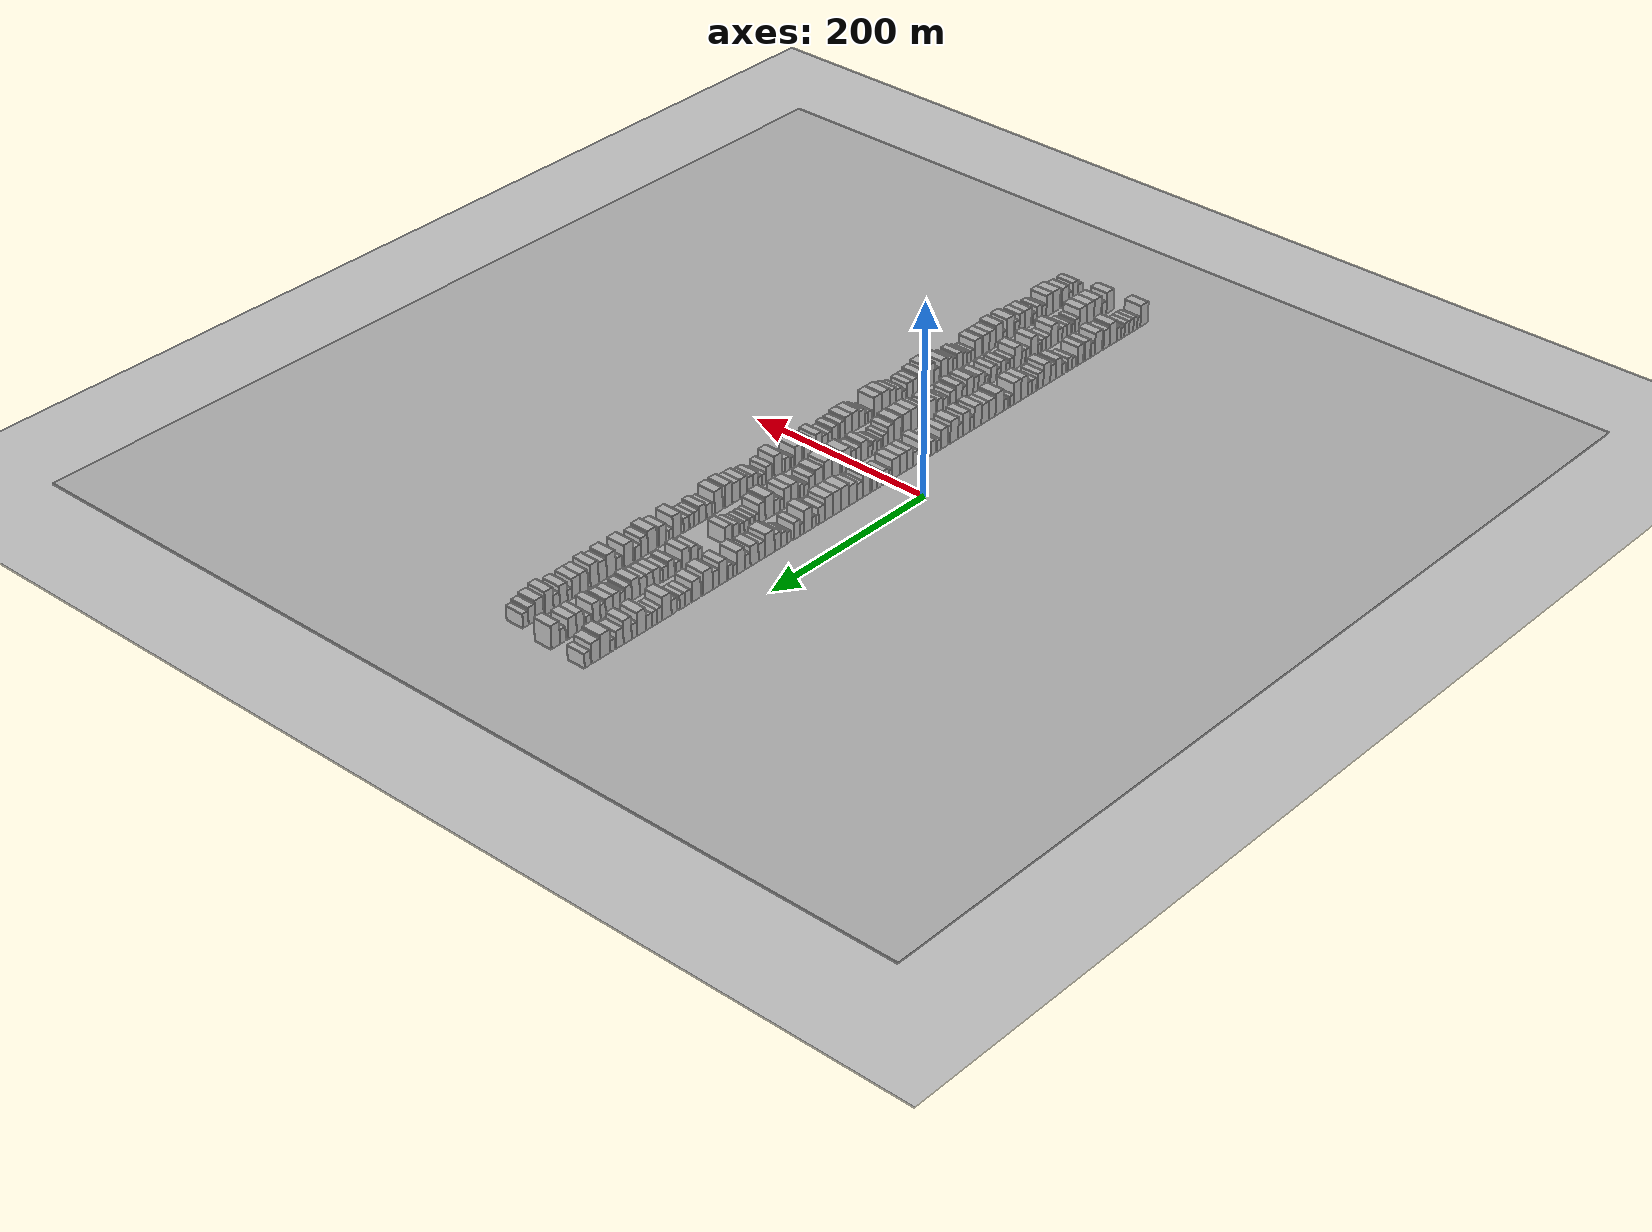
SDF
<?xml version="1.0" encoding="utf-8"?>

<sdf version="1.6">

   <world name="default">

      <gui fullscreen="0">

         <camera name="user_camera">

            <pose>-15 0 4.57585 0 0 0</pose>

            <view_controller>orbit</view_controller>

         </camera>

      </gui>

      <scene>

         <sky>

           <clouds>

             <speed>12</speed>

           </clouds>

         </sky>

         <ambient>0.4 0.4 0.4 1</ambient>

         <background>0.7 0.7 0.7 1</background>

         <shadows>1</shadows>

      </scene>

      <gravity>0 0 -9.8066</gravity>

      <magnetic_field>6e-06 2.3e-05 -4.2e-05</magnetic_field>

      <physics default="0" name="default_physics" type="ode">

         <ode>

            <solver>

               <type>quick</type>

               <iters>10</iters>

               <sor>1.0</sor>

               <use_dynamic_moi_rescaling>0</use_dynamic_moi_rescaling>

            </solver>

            <constraints>

               <cfm>0</cfm>

               <erp>0.2</erp>

               <contact_max_correcting_vel>100</contact_max_correcting_vel>

               <contact_surface_layer>0.001</contact_surface_layer>

            </constraints>

         </ode>

         <max_step_size>0.004</max_step_size>

         <real_time_factor>1</real_time_factor>

         <real_time_update_rate>250</real_time_update_rate>

      </physics>

      <light name="sun" type="directional">

         <cast_shadows>1</cast_shadows>

         <pose>0 0 10 0 0 0</pose>

         <diffuse>0.8 0.8 0.8 1</diffuse>

         <specular>0.2 0.2 0.2 1</specular>

         <attenuation>

            <range>1000</range>

            <constant>0.9</constant>

            <linear>0.01</linear>

            <quadratic>0.001</quadratic>

         </attenuation>

         <direction>-0.5 0.1 -0.9</direction>

      </light>

      <include>

         <name>ground_plane_1</name>

         <uri>model://HANNAS_ground_plane</uri>

         <pose>0 0 0  0 0 0</pose>

      </include>

      <include>

         <name>ground_plane_2</name>

         <uri>model://HANNAS_ground_plane</uri>

         <pose>100 0 0  0 0 0</pose>

      </include>

      <model name="building_1">

         <static>1</static>

         <pose frame="">50.0000 -374.2529 0 0.000000 0.000000 0.000000</pose>

         <link name="link">

            <pose frame="">0 0 12.00 0 0 0</pose>

            <collision name="collision">

               <geometry>

                  <box>

                     <size>20.0000 11.4942 24.0000</size>

                  </box>

               </geometry>

               <max_contacts>10</max_contacts>

               <surface>

                  <contact>

                     <ode/>

                  </contact>

                  <bounce/>

                  <friction>

                     <torsional>

                        <ode/>

                     </torsional>

                     <ode/>

                  </friction>

               </surface>

            </collision>

            <visual name="visual">

               <cast_shadows>0</cast_shadows>

               <geometry>

                  <box>

                     <size>20.0000 11.4942 24.0000</size>

                  </box>

               </geometry>

               <material>

                  <script>

                     <uri>model://HANNAS_wall/materials/scripts</uri>

                     <uri>model://HANNAS_wall/materials/textures</uri>

                     <name>vrc/HANNAS_wall</name>

                  </script>

               </material>

            </visual>

            <self_collide>0</self_collide>

            <enable_wind>0</enable_wind>

            <kinematic>0</kinematic>

         </link>

      </model>

      <model name="building_2">

         <static>1</static>

         <pose frame="">50.0000 -365.9601 0 0.000000 0.000000 0.000000</pose>

         <link name="link">

            <pose frame="">0 0 6.00 0 0 0</pose>

            <collision name="collision">

               <geometry>

                  <box>

                     <size>20.0000 5.0915 12.0000</size>

                  </box>

               </geometry>

               <max_contacts>10</max_contacts>

               <surface>

                  <contact>

                     <ode/>

                  </contact>

                  <bounce/>

                  <friction>

                     <torsional>

                        <ode/>

                     </torsional>

                     <ode/>

                  </friction>

               </surface>

            </collision>

            <visual name="visual">

               <cast_shadows>0</cast_shadows>

               <geometry>

                  <box>

                     <size>20.0000 5.0915 12.0000</size>

                  </box>

               </geometry>

               <material>

                  <script>

                     <uri>model://HANNAS_wall/materials/scripts</uri>

                     <uri>model://HANNAS_wall/materials/textures</uri>

                     <name>vrc/HANNAS_wall</name>

                  </script>

               </material>

            </visual>

            <self_collide>0</self_collide>

            <enable_wind>0</enable_wind>

            <kinematic>0</kinematic>

         </link>

      </model>

      <model name="building_3">

         <static>1</static>

         <pose frame="">50.0000 -360.3710 0 0.000000 0.000000 0.000000</pose>

         <link name="link">

            <pose frame="">0 0 7.50 0 0 0</pose>

            <collision name="collision">

               <geometry>

                  <box>

                     <size>20.0000 6.0867 15.0000</size>

                  </box>

               </geometry>

               <max_contacts>10</max_contacts>

               <surface>

                  <contact>

                     <ode/>

                  </contact>

                  <bounce/>

                  <friction>

                     <torsional>

                        <ode/>

                     </torsional>

                     <ode/>

                  </friction>

               </surface>

            </collision>

            <visual name="visual">

               <cast_shadows>0</cast_shadows>

               <geometry>

                  <box>

                     <size>20.0000 6.0867 15.0000</size>

                  </box>

               </geometry>

               <material>

                  <script>

                     <uri>model://HANNAS_wall/materials/scripts</uri>

                     <uri>model://HANNAS_wall/materials/textures</uri>

                     <name>vrc/HANNAS_wall</name>

                  </script>

               </material>

            </visual>

            <self_collide>0</self_collide>

            <enable_wind>0</enable_wind>

            <kinematic>0</kinematic>

         </link>

      </model>

      <model name="building_4">

         <static>1</static>

         <pose frame="">50.0000 -353.9919 0 0.000000 0.000000 0.000000</pose>

         <link name="link">

            <pose frame="">0 0 7.50 0 0 0</pose>

            <collision name="collision">

               <geometry>

                  <box>

                     <size>20.0000 6.6715 15.0000</size>

                  </box>

               </geometry>

               <max_contacts>10</max_contacts>

               <surface>

                  <contact>

                     <ode/>

                  </contact>

                  <bounce/>

                  <friction>

                     <torsional>

                        <ode/>

                     </torsional>

                     <ode/>

                  </friction>

               </surface>

            </collision>

            <visual name="visual">

               <cast_shadows>0</cast_shadows>

               <geometry>

                  <box>

                     <size>20.0000 6.6715 15.0000</size>

                  </box>

               </geometry>

               <material>

                  <script>

                     <uri>model://HANNAS_wall/materials/scripts</uri>

                     <uri>model://HANNAS_wall/materials/textures</uri>

                     <name>vrc/HANNAS_wall</name>

                  </script>

               </material>

            </visual>

            <self_collide>0</self_collide>

            <enable_wind>0</enable_wind>

            <kinematic>0</kinematic>

         </link>

      </model>

      <model name="building_5">

         <static>1</static>

         <pose frame="">50.0000 -347.0081 0 0.000000 0.000000 0.000000</pose>

         <link name="link">

            <pose frame="">0 0 7.50 0 0 0</pose>

            <collision name="collision">

               <geometry>

                  <box>

                     <size>20.0000 7.2961 15.0000</size>

                  </box>

               </geometry>

               <max_contacts>10</max_contacts>

               <surface>

                  <contact>

                     <ode/>

                  </contact>

                  <bounce/>

                  <friction>

                     <torsional>

                        <ode/>

                     </torsional>

                     <ode/>

                  </friction>

               </surface>

            </collision>

            <visual name="visual">

               <cast_shadows>0</cast_shadows>

               <geometry>

                  <box>

                     <size>20.0000 7.2961 15.0000</size>

                  </box>

               </geometry>

               <material>

                  <script>

                     <uri>model://HANNAS_wall/materials/scripts</uri>

                     <uri>model://HANNAS_wall/materials/textures</uri>

                     <name>vrc/HANNAS_wall</name>

                  </script>

               </material>

            </visual>

            <self_collide>0</self_collide>

            <enable_wind>0</enable_wind>

            <kinematic>0</kinematic>

         </link>

      </model>

      <model name="building_6">

         <static>1</static>

         <pose frame="">50.0000 -340.6397 0 0.000000 0.000000 0.000000</pose>

         <link name="link">

            <pose frame="">0 0 6.00 0 0 0</pose>

            <collision name="collision">

               <geometry>

                  <box>

                     <size>20.0000 5.4406 12.0000</size>

                  </box>

               </geometry>

               <max_contacts>10</max_contacts>

               <surface>

                  <contact>

                     <ode/>

                  </contact>

                  <bounce/>

                  <friction>

                     <torsional>

                        <ode/>

                     </torsional>

                     <ode/>

                  </friction>

               </surface>

            </collision>

            <visual name="visual">

               <cast_shadows>0</cast_shadows>

               <geometry>

                  <box>

                     <size>20.0000 5.4406 12.0000</size>

                  </box>

               </geometry>

               <material>

                  <script>

                     <uri>model://HANNAS_wall/materials/scripts</uri>

                     <uri>model://HANNAS_wall/materials/textures</uri>

                     <name>vrc/HANNAS_wall</name>

                  </script>

               </material>

            </visual>

            <self_collide>0</self_collide>

            <enable_wind>0</enable_wind>

            <kinematic>0</kinematic>

         </link>

      </model>

      <model name="building_7">

         <static>1</static>

         <pose frame="">50.0000 -334.5987 0 0.000000 0.000000 0.000000</pose>

         <link name="link">

            <pose frame="">0 0 7.50 0 0 0</pose>

            <collision name="collision">

               <geometry>

                  <box>

                     <size>20.0000 6.6415 15.0000</size>

                  </box>

               </geometry>

               <max_contacts>10</max_contacts>

               <surface>

                  <contact>

                     <ode/>

                  </contact>

                  <bounce/>

                  <friction>

                     <torsional>

                        <ode/>

                     </torsional>

                     <ode/>

                  </friction>

               </surface>

            </collision>

            <visual name="visual">

               <cast_shadows>0</cast_shadows>

               <geometry>

                  <box>

                     <size>20.0000 6.6415 15.0000</size>

                  </box>

               </geometry>

               <material>

                  <script>

                     <uri>model://HANNAS_wall/materials/scripts</uri>

                     <uri>model://HANNAS_wall/materials/textures</uri>

                     <name>vrc/HANNAS_wall</name>

                  </script>

               </material>

            </visual>

            <self_collide>0</self_collide>

            <enable_wind>0</enable_wind>

            <kinematic>0</kinematic>

         </link>

      </model>

      <model name="building_8">

         <static>1</static>

         <pose frame="">50.0000 -325.7107 0 0.000000 0.000000 0.000000</pose>

         <link name="link">

            <pose frame="">0 0 12.00 0 0 0</pose>

            <collision name="collision">

               <geometry>

                  <box>

                     <size>20.0000 11.1344 24.0000</size>

                  </box>

               </geometry>

               <max_contacts>10</max_contacts>

               <surface>

                  <contact>

                     <ode/>

                  </contact>

                  <bounce/>

                  <friction>

                     <torsional>

                        <ode/>

                     </torsional>

                     <ode/>

                  </friction>

               </surface>

            </collision>

            <visual name="visual">

               <cast_shadows>0</cast_shadows>

               <geometry>

                  <box>

                     <size>20.0000 11.1344 24.0000</size>

                  </box>

               </geometry>

               <material>

                  <script>

                     <uri>model://HANNAS_wall/materials/scripts</uri>

                     <uri>model://HANNAS_wall/materials/textures</uri>

                     <name>vrc/HANNAS_wall</name>

                  </script>

               </material>

            </visual>

            <self_collide>0</self_collide>

            <enable_wind>0</enable_wind>

            <kinematic>0</kinematic>

         </link>

      </model>

      <model name="building_9">

         <static>1</static>

         <pose frame="">50.0000 -315.4351 0 0.000000 0.000000 0.000000</pose>

         <link name="link">

            <pose frame="">0 0 10.50 0 0 0</pose>

            <collision name="collision">

               <geometry>

                  <box>

                     <size>20.0000 9.4169 21.0000</size>

                  </box>

               </geometry>

               <max_contacts>10</max_contacts>

               <surface>

                  <contact>

                     <ode/>

                  </contact>

                  <bounce/>

                  <friction>

                     <torsional>

                        <ode/>

                     </torsional>

                     <ode/>

                  </friction>

               </surface>

            </collision>

            <visual name="visual">

               <cast_shadows>0</cast_shadows>

               <geometry>

                  <box>

                     <size>20.0000 9.4169 21.0000</size>

                  </box>

               </geometry>

               <material>

                  <script>

                     <uri>model://HANNAS_wall/materials/scripts</uri>

                     <uri>model://HANNAS_wall/materials/textures</uri>

                     <name>vrc/HANNAS_wall</name>

                  </script>

               </material>

            </visual>

            <self_collide>0</self_collide>

            <enable_wind>0</enable_wind>

            <kinematic>0</kinematic>

         </link>

      </model>

      <model name="building_10">

         <static>1</static>

         <pose frame="">50.0000 -303.1184 0 0.000000 0.000000 0.000000</pose>

         <link name="link">

            <pose frame="">0 0 12.00 0 0 0</pose>

            <collision name="collision">

               <geometry>

                  <box>

                     <size>20.0000 11.2165 24.0000</size>

                  </box>

               </geometry>

               <max_contacts>10</max_contacts>

               <surface>

                  <contact>

                     <ode/>

                  </contact>

                  <bounce/>

                  <friction>

                     <torsional>

                        <ode/>

                     </torsional>

                     <ode/>

                  </friction>

               </surface>

            </collision>

            <visual name="visual">

               <cast_shadows>0</cast_shadows>

               <geometry>

                  <box>

                     <size>20.0000 11.2165 24.0000</size>

                  </box>

               </geometry>

               <material>

                  <script>

                     <uri>model://HANNAS_wall/materials/scripts</uri>

                     <uri>model://HANNAS_wall/materials/textures</uri>

                     <name>vrc/HANNAS_wall</name>

                  </script>

               </material>

            </visual>

            <self_collide>0</self_collide>

            <enable_wind>0</enable_wind>

            <kinematic>0</kinematic>

         </link>

      </model>

      <model name="building_11">

         <static>1</static>

         <pose frame="">50.0000 -294.4629 0 0.000000 0.000000 0.000000</pose>

         <link name="link">

            <pose frame="">0 0 7.50 0 0 0</pose>

            <collision name="collision">

               <geometry>

                  <box>

                     <size>20.0000 6.0944 15.0000</size>

                  </box>

               </geometry>

               <max_contacts>10</max_contacts>

               <surface>

                  <contact>

                     <ode/>

                  </contact>

                  <bounce/>

                  <friction>

                     <torsional>

                        <ode/>

                     </torsional>

                     <ode/>

                  </friction>

               </surface>

            </collision>

            <visual name="visual">

               <cast_shadows>0</cast_shadows>

               <geometry>

                  <box>

                     <size>20.0000 6.0944 15.0000</size>

                  </box>

               </geometry>

               <material>

                  <script>

                     <uri>model://HANNAS_wall/materials/scripts</uri>

                     <uri>model://HANNAS_wall/materials/textures</uri>

                     <name>vrc/HANNAS_wall</name>

                  </script>

               </material>

            </visual>

            <self_collide>0</self_collide>

            <enable_wind>0</enable_wind>

            <kinematic>0</kinematic>

         </link>

      </model>

      <model name="building_12">

         <static>1</static>

         <pose frame="">50.0000 -286.0905 0 0.000000 0.000000 0.000000</pose>

         <link name="link">

            <pose frame="">0 0 10.50 0 0 0</pose>

            <collision name="collision">

               <geometry>

                  <box>

                     <size>20.0000 8.6504 21.0000</size>

                  </box>

               </geometry>

               <max_contacts>10</max_contacts>

               <surface>

                  <contact>

                     <ode/>

                  </contact>

                  <bounce/>

                  <friction>

                     <torsional>

                        <ode/>

                     </torsional>

                     <ode/>

                  </friction>

               </surface>

            </collision>

            <visual name="visual">

               <cast_shadows>0</cast_shadows>

               <geometry>

                  <box>

                     <size>20.0000 8.6504 21.0000</size>

                  </box>

               </geometry>

               <material>

                  <script>

                     <uri>model://HANNAS_wall/materials/scripts</uri>

                     <uri>model://HANNAS_wall/materials/textures</uri>

                     <name>vrc/HANNAS_wall</name>

                  </script>

               </material>

            </visual>

            <self_collide>0</self_collide>

            <enable_wind>0</enable_wind>

            <kinematic>0</kinematic>

         </link>

      </model>

      <model name="building_13">

         <static>1</static>

         <pose frame="">50.0000 -275.4024 0 0.000000 0.000000 0.000000</pose>

         <link name="link">

            <pose frame="">0 0 10.50 0 0 0</pose>

            <collision name="collision">

               <geometry>

                  <box>

                     <size>20.0000 8.7257 21.0000</size>

                  </box>

               </geometry>

               <max_contacts>10</max_contacts>

               <surface>

                  <contact>

                     <ode/>

                  </contact>

                  <bounce/>

                  <friction>

                     <torsional>

                        <ode/>

                     </torsional>

                     <ode/>

                  </friction>

               </surface>

            </collision>

            <visual name="visual">

               <cast_shadows>0</cast_shadows>

               <geometry>

                  <box>

                     <size>20.0000 8.7257 21.0000</size>

                  </box>

               </geometry>

               <material>

                  <script>

                     <uri>model://HANNAS_wall/materials/scripts</uri>

                     <uri>model://HANNAS_wall/materials/textures</uri>

                     <name>vrc/HANNAS_wall</name>

                  </script>

               </material>

            </visual>

            <self_collide>0</self_collide>

            <enable_wind>0</enable_wind>

            <kinematic>0</kinematic>

         </link>

      </model>

      <model name="building_14">

         <static>1</static>

         <pose frame="">50.0000 -265.4668 0 0.000000 0.000000 0.000000</pose>

         <link name="link">

            <pose frame="">0 0 6.00 0 0 0</pose>

            <collision name="collision">

               <geometry>

                  <box>

                     <size>20.0000 5.1457 12.0000</size>

                  </box>

               </geometry>

               <max_contacts>10</max_contacts>

               <surface>

                  <contact>

                     <ode/>

                  </contact>

                  <bounce/>

                  <friction>

                     <torsional>

                        <ode/>

                     </torsional>

                     <ode/>

                  </friction>

               </surface>

            </collision>

            <visual name="visual">

               <cast_shadows>0</cast_shadows>

               <geometry>

                  <box>

                     <size>20.0000 5.1457 12.0000</size>

                  </box>

               </geometry>

               <material>

                  <script>

                     <uri>model://HANNAS_wall/materials/scripts</uri>

                     <uri>model://HANNAS_wall/materials/textures</uri>

                     <name>vrc/HANNAS_wall</name>

                  </script>

               </material>

            </visual>

            <self_collide>0</self_collide>

            <enable_wind>0</enable_wind>

            <kinematic>0</kinematic>

         </link>

      </model>

      <model name="building_15">

         <static>1</static>

         <pose frame="">50.0000 -259.4343 0 0.000000 0.000000 0.000000</pose>

         <link name="link">

            <pose frame="">0 0 7.50 0 0 0</pose>

            <collision name="collision">

               <geometry>

                  <box>

                     <size>20.0000 6.9193 15.0000</size>

                  </box>

               </geometry>

               <max_contacts>10</max_contacts>

               <surface>

                  <contact>

                     <ode/>

                  </contact>

                  <bounce/>

                  <friction>

                     <torsional>

                        <ode/>

                     </torsional>

                     <ode/>

                  </friction>

               </surface>

            </collision>

            <visual name="visual">

               <cast_shadows>0</cast_shadows>

               <geometry>

                  <box>

                     <size>20.0000 6.9193 15.0000</size>

                  </box>

               </geometry>

               <material>

                  <script>

                     <uri>model://HANNAS_wall/materials/scripts</uri>

                     <uri>model://HANNAS_wall/materials/textures</uri>

                     <name>vrc/HANNAS_wall</name>

                  </script>

               </material>

            </visual>

            <self_collide>0</self_collide>

            <enable_wind>0</enable_wind>

            <kinematic>0</kinematic>

         </link>

      </model>

      <model name="building_16">

         <static>1</static>

         <pose frame="">50.0000 -250.0819 0 0.000000 0.000000 0.000000</pose>

         <link name="link">

            <pose frame="">0 0 6.00 0 0 0</pose>

            <collision name="collision">

               <geometry>

                  <box>

                     <size>20.0000 5.7855 12.0000</size>

                  </box>

               </geometry>

               <max_contacts>10</max_contacts>

               <surface>

                  <contact>

                     <ode/>

                  </contact>

                  <bounce/>

                  <friction>

                     <torsional>

                        <ode/>

                     </torsional>

                     <ode/>

                  </friction>

               </surface>

            </collision>

            <visual name="visual">

               <cast_shadows>0</cast_shadows>

               <geometry>

                  <box>

                     <size>20.0000 5.7855 12.0000</size>

                  </box>

               </geometry>

               <material>

                  <script>

                     <uri>model://HANNAS_wall/materials/scripts</uri>

                     <uri>model://HANNAS_wall/materials/textures</uri>

                     <name>vrc/HANNAS_wall</name>

                  </script>

               </material>

            </visual>

            <self_collide>0</self_collide>

            <enable_wind>0</enable_wind>

            <kinematic>0</kinematic>

         </link>

      </model>

      <model name="building_17">

         <static>1</static>

         <pose frame="">50.0000 -242.6918 0 0.000000 0.000000 0.000000</pose>

         <link name="link">

            <pose frame="">0 0 10.50 0 0 0</pose>

            <collision name="collision">

               <geometry>

                  <box>

                     <size>20.0000 8.9945 21.0000</size>

                  </box>

               </geometry>

               <max_contacts>10</max_contacts>

               <surface>

                  <contact>

                     <ode/>

                  </contact>

                  <bounce/>

                  <friction>

                     <torsional>

                        <ode/>

                     </torsional>

                     <ode/>

                  </friction>

               </surface>

            </collision>

            <visual name="visual">

               <cast_shadows>0</cast_shadows>

               <geometry>

                  <box>

                     <size>20.0000 8.9945 21.0000</size>

                  </box>

               </geometry>

               <material>

                  <script>

                     <uri>model://HANNAS_wall/materials/scripts</uri>

                     <uri>model://HANNAS_wall/materials/textures</uri>

                     <name>vrc/HANNAS_wall</name>

                  </script>

               </material>

            </visual>

            <self_collide>0</self_collide>

            <enable_wind>0</enable_wind>

            <kinematic>0</kinematic>

         </link>

      </model>

      <model name="building_18">

         <static>1</static>

         <pose frame="">50.0000 -234.0572 0 0.000000 0.000000 0.000000</pose>

         <link name="link">

            <pose frame="">0 0 9.00 0 0 0</pose>

            <collision name="collision">

               <geometry>

                  <box>

                     <size>20.0000 8.2747 18.0000</size>

                  </box>

               </geometry>

               <max_contacts>10</max_contacts>

               <surface>

                  <contact>

                     <ode/>

                  </contact>

                  <bounce/>

                  <friction>

                     <torsional>

                        <ode/>

                     </torsional>

                     <ode/>

                  </friction>

               </surface>

            </collision>

            <visual name="visual">

               <cast_shadows>0</cast_shadows>

               <geometry>

                  <box>

                     <size>20.0000 8.2747 18.0000</size>

                  </box>

               </geometry>

               <material>

                  <script>

                     <uri>model://HANNAS_wall/materials/scripts</uri>

                     <uri>model://HANNAS_wall/materials/textures</uri>

                     <name>vrc/HANNAS_wall</name>

                  </script>

               </material>

            </visual>

            <self_collide>0</self_collide>

            <enable_wind>0</enable_wind>

            <kinematic>0</kinematic>

         </link>

      </model>

      <model name="building_19">

         <static>1</static>

         <pose frame="">50.0000 -224.6590 0 0.000000 0.000000 0.000000</pose>

         <link name="link">

            <pose frame="">0 0 12.00 0 0 0</pose>

            <collision name="collision">

               <geometry>

                  <box>

                     <size>20.0000 10.5217 24.0000</size>

                  </box>

               </geometry>

               <max_contacts>10</max_contacts>

               <surface>

                  <contact>

                     <ode/>

                  </contact>

                  <bounce/>

                  <friction>

                     <torsional>

                        <ode/>

                     </torsional>

                     <ode/>

                  </friction>

               </surface>

            </collision>

            <visual name="visual">

               <cast_shadows>0</cast_shadows>

               <geometry>

                  <box>

                     <size>20.0000 10.5217 24.0000</size>

                  </box>

               </geometry>

               <material>

                  <script>

                     <uri>model://HANNAS_wall/materials/scripts</uri>

                     <uri>model://HANNAS_wall/materials/textures</uri>

                     <name>vrc/HANNAS_wall</name>

                  </script>

               </material>

            </visual>

            <self_collide>0</self_collide>

            <enable_wind>0</enable_wind>

            <kinematic>0</kinematic>

         </link>

      </model>

      <model name="building_20">

         <static>1</static>

         <pose frame="">50.0000 -215.1899 0 0.000000 0.000000 0.000000</pose>

         <link name="link">

            <pose frame="">0 0 9.00 0 0 0</pose>

            <collision name="collision">

               <geometry>

                  <box>

                     <size>20.0000 8.4163 18.0000</size>

                  </box>

               </geometry>

               <max_contacts>10</max_contacts>

               <surface>

                  <contact>

                     <ode/>

                  </contact>

                  <bounce/>

                  <friction>

                     <torsional>

                        <ode/>

                     </torsional>

                     <ode/>

                  </friction>

               </surface>

            </collision>

            <visual name="visual">

               <cast_shadows>0</cast_shadows>

               <geometry>

                  <box>

                     <size>20.0000 8.4163 18.0000</size>

                  </box>

               </geometry>

               <material>

                  <script>

                     <uri>model://HANNAS_wall/materials/scripts</uri>

                     <uri>model://HANNAS_wall/materials/textures</uri>

                     <name>vrc/HANNAS_wall</name>

                  </script>

               </material>

            </visual>

            <self_collide>0</self_collide>

            <enable_wind>0</enable_wind>

            <kinematic>0</kinematic>

         </link>

      </model>

      <model name="building_21">

         <static>1</static>

         <pose frame="">50.0000 -205.7760 0 0.000000 0.000000 0.000000</pose>

         <link name="link">

            <pose frame="">0 0 7.50 0 0 0</pose>

            <collision name="collision">

               <geometry>

                  <box>

                     <size>20.0000 6.4114 15.0000</size>

                  </box>

               </geometry>

               <max_contacts>10</max_contacts>

               <surface>

                  <contact>

                     <ode/>

                  </contact>

                  <bounce/>

                  <friction>

                     <torsional>

                        <ode/>

                     </torsional>

                     <ode/>

                  </friction>

               </surface>

            </collision>

            <visual name="visual">

               <cast_shadows>0</cast_shadows>

               <geometry>

                  <box>

                     <size>20.0000 6.4114 15.0000</size>

                  </box>

               </geometry>

               <material>

                  <script>

                     <uri>model://HANNAS_wall/materials/scripts</uri>

                     <uri>model://HANNAS_wall/materials/textures</uri>

                     <name>vrc/HANNAS_wall</name>

                  </script>

               </material>

            </visual>

            <self_collide>0</self_collide>

            <enable_wind>0</enable_wind>

            <kinematic>0</kinematic>

         </link>

      </model>

      <model name="building_22">

         <static>1</static>

         <pose frame="">50.0000 -199.2839 0 0.000000 0.000000 0.000000</pose>

         <link name="link">

            <pose frame="">0 0 7.50 0 0 0</pose>

            <collision name="collision">

               <geometry>

                  <box>

                     <size>20.0000 6.5729 15.0000</size>

                  </box>

               </geometry>

               <max_contacts>10</max_contacts>

               <surface>

                  <contact>

                     <ode/>

                  </contact>

                  <bounce/>

                  <friction>

                     <torsional>

                        <ode/>

                     </torsional>

                     <ode/>

                  </friction>

               </surface>

            </collision>

            <visual name="visual">

               <cast_shadows>0</cast_shadows>

               <geometry>

                  <box>

                     <size>20.0000 6.5729 15.0000</size>

                  </box>

               </geometry>

               <material>

                  <script>

                     <uri>model://HANNAS_wall/materials/scripts</uri>

                     <uri>model://HANNAS_wall/materials/textures</uri>

                     <name>vrc/HANNAS_wall</name>

                  </script>

               </material>

            </visual>

            <self_collide>0</self_collide>

            <enable_wind>0</enable_wind>

            <kinematic>0</kinematic>

         </link>

      </model>

      <model name="building_23">

         <static>1</static>

         <pose frame="">50.0000 -191.1255 0 0.000000 0.000000 0.000000</pose>

         <link name="link">

            <pose frame="">0 0 12.00 0 0 0</pose>

            <collision name="collision">

               <geometry>

                  <box>

                     <size>20.0000 9.7438 24.0000</size>

                  </box>

               </geometry>

               <max_contacts>10</max_contacts>

               <surface>

                  <contact>

                     <ode/>

                  </contact>

                  <bounce/>

                  <friction>

                     <torsional>

                        <ode/>

                     </torsional>

                     <ode/>

                  </friction>

               </surface>

            </collision>

            <visual name="visual">

               <cast_shadows>0</cast_shadows>

               <geometry>

                  <box>

                     <size>20.0000 9.7438 24.0000</size>

                  </box>

               </geometry>

               <material>

                  <script>

                     <uri>model://HANNAS_wall/materials/scripts</uri>

                     <uri>model://HANNAS_wall/materials/textures</uri>

                     <name>vrc/HANNAS_wall</name>

                  </script>

               </material>

            </visual>

            <self_collide>0</self_collide>

            <enable_wind>0</enable_wind>

            <kinematic>0</kinematic>

         </link>

      </model>

      <model name="building_24">

         <static>1</static>

         <pose frame="">50.0000 -180.8366 0 0.000000 0.000000 0.000000</pose>

         <link name="link">

            <pose frame="">0 0 12.00 0 0 0</pose>

            <collision name="collision">

               <geometry>

                  <box>

                     <size>20.0000 10.8340 24.0000</size>

                  </box>

               </geometry>

               <max_contacts>10</max_contacts>

               <surface>

                  <contact>

                     <ode/>

                  </contact>

                  <bounce/>

                  <friction>

                     <torsional>

                        <ode/>

                     </torsional>

                     <ode/>

                  </friction>

               </surface>

            </collision>

            <visual name="visual">

               <cast_shadows>0</cast_shadows>

               <geometry>

                  <box>

                     <size>20.0000 10.8340 24.0000</size>

                  </box>

               </geometry>

               <material>

                  <script>

                     <uri>model://HANNAS_wall/materials/scripts</uri>

                     <uri>model://HANNAS_wall/materials/textures</uri>

                     <name>vrc/HANNAS_wall</name>

                  </script>

               </material>

            </visual>

            <self_collide>0</self_collide>

            <enable_wind>0</enable_wind>

            <kinematic>0</kinematic>

         </link>

      </model>

      <model name="building_25">

         <static>1</static>

         <pose frame="">50.0000 -172.5278 0 0.000000 0.000000 0.000000</pose>

         <link name="link">

            <pose frame="">0 0 6.00 0 0 0</pose>

            <collision name="collision">

               <geometry>

                  <box>

                     <size>20.0000 5.7835 12.0000</size>

                  </box>

               </geometry>

               <max_contacts>10</max_contacts>

               <surface>

                  <contact>

                     <ode/>

                  </contact>

                  <bounce/>

                  <friction>

                     <torsional>

                        <ode/>

                     </torsional>

                     <ode/>

                  </friction>

               </surface>

            </collision>

            <visual name="visual">

               <cast_shadows>0</cast_shadows>

               <geometry>

                  <box>

                     <size>20.0000 5.7835 12.0000</size>

                  </box>

               </geometry>

               <material>

                  <script>

                     <uri>model://HANNAS_wall/materials/scripts</uri>

                     <uri>model://HANNAS_wall/materials/textures</uri>

                     <name>vrc/HANNAS_wall</name>

                  </script>

               </material>

            </visual>

            <self_collide>0</self_collide>

            <enable_wind>0</enable_wind>

            <kinematic>0</kinematic>

         </link>

      </model>

      <model name="building_26">

         <static>1</static>

         <pose frame="">50.0000 -163.6434 0 0.000000 0.000000 0.000000</pose>

         <link name="link">

            <pose frame="">0 0 6.00 0 0 0</pose>

            <collision name="collision">

               <geometry>

                  <box>

                     <size>20.0000 5.9854 12.0000</size>

                  </box>

               </geometry>

               <max_contacts>10</max_contacts>

               <surface>

                  <contact>

                     <ode/>

                  </contact>

                  <bounce/>

                  <friction>

                     <torsional>

                        <ode/>

                     </torsional>

                     <ode/>

                  </friction>

               </surface>

            </collision>

            <visual name="visual">

               <cast_shadows>0</cast_shadows>

               <geometry>

                  <box>

                     <size>20.0000 5.9854 12.0000</size>

                  </box>

               </geometry>

               <material>

                  <script>

                     <uri>model://HANNAS_wall/materials/scripts</uri>

                     <uri>model://HANNAS_wall/materials/textures</uri>

                     <name>vrc/HANNAS_wall</name>

                  </script>

               </material>

            </visual>

            <self_collide>0</self_collide>

            <enable_wind>0</enable_wind>

            <kinematic>0</kinematic>

         </link>

      </model>

      <model name="building_27">

         <static>1</static>

         <pose frame="">50.0000 -154.7821 0 0.000000 0.000000 0.000000</pose>

         <link name="link">

            <pose frame="">0 0 12.00 0 0 0</pose>

            <collision name="collision">

               <geometry>

                  <box>

                     <size>20.0000 11.7372 24.0000</size>

                  </box>

               </geometry>

               <max_contacts>10</max_contacts>

               <surface>

                  <contact>

                     <ode/>

                  </contact>

                  <bounce/>

                  <friction>

                     <torsional>

                        <ode/>

                     </torsional>

                     <ode/>

                  </friction>

               </surface>

            </collision>

            <visual name="visual">

               <cast_shadows>0</cast_shadows>

               <geometry>

                  <box>

                     <size>20.0000 11.7372 24.0000</size>

                  </box>

               </geometry>

               <material>

                  <script>

                     <uri>model://HANNAS_wall/materials/scripts</uri>

                     <uri>model://HANNAS_wall/materials/textures</uri>

                     <name>vrc/HANNAS_wall</name>

                  </script>

               </material>

            </visual>

            <self_collide>0</self_collide>

            <enable_wind>0</enable_wind>

            <kinematic>0</kinematic>

         </link>

      </model>

      <model name="building_28">

         <static>1</static>

         <pose frame="">50.0000 -143.9540 0 0.000000 0.000000 0.000000</pose>

         <link name="link">

            <pose frame="">0 0 10.50 0 0 0</pose>

            <collision name="collision">

               <geometry>

                  <box>

                     <size>20.0000 9.9189 21.0000</size>

                  </box>

               </geometry>

               <max_contacts>10</max_contacts>

               <surface>

                  <contact>

                     <ode/>

                  </contact>

                  <bounce/>

                  <friction>

                     <torsional>

                        <ode/>

                     </torsional>

                     <ode/>

                  </friction>

               </surface>

            </collision>

            <visual name="visual">

               <cast_shadows>0</cast_shadows>

               <geometry>

                  <box>

                     <size>20.0000 9.9189 21.0000</size>

                  </box>

               </geometry>

               <material>

                  <script>

                     <uri>model://HANNAS_wall/materials/scripts</uri>

                     <uri>model://HANNAS_wall/materials/textures</uri>

                     <name>vrc/HANNAS_wall</name>

                  </script>

               </material>

            </visual>

            <self_collide>0</self_collide>

            <enable_wind>0</enable_wind>

            <kinematic>0</kinematic>

         </link>

      </model>

      <model name="building_29">

         <static>1</static>

         <pose frame="">50.0000 -133.7586 0 0.000000 0.000000 0.000000</pose>

         <link name="link">

            <pose frame="">0 0 10.50 0 0 0</pose>

            <collision name="collision">

               <geometry>

                  <box>

                     <size>20.0000 10.4721 21.0000</size>

                  </box>

               </geometry>

               <max_contacts>10</max_contacts>

               <surface>

                  <contact>

                     <ode/>

                  </contact>

                  <bounce/>

                  <friction>

                     <torsional>

                        <ode/>

                     </torsional>

                     <ode/>

                  </friction>

               </surface>

            </collision>

            <visual name="visual">

               <cast_shadows>0</cast_shadows>

               <geometry>

                  <box>

                     <size>20.0000 10.4721 21.0000</size>

                  </box>

               </geometry>

               <material>

                  <script>

                     <uri>model://HANNAS_wall/materials/scripts</uri>

                     <uri>model://HANNAS_wall/materials/textures</uri>

                     <name>vrc/HANNAS_wall</name>

                  </script>

               </material>

            </visual>

            <self_collide>0</self_collide>

            <enable_wind>0</enable_wind>

            <kinematic>0</kinematic>

         </link>

      </model>

      <model name="building_30">

         <static>1</static>

         <pose frame="">50.0000 -123.3076 0 0.000000 0.000000 0.000000</pose>

         <link name="link">

            <pose frame="">0 0 12.00 0 0 0</pose>

            <collision name="collision">

               <geometry>

                  <box>

                     <size>20.0000 10.4298 24.0000</size>

                  </box>

               </geometry>

               <max_contacts>10</max_contacts>

               <surface>

                  <contact>

                     <ode/>

                  </contact>

                  <bounce/>

                  <friction>

                     <torsional>

                        <ode/>

                     </torsional>

                     <ode/>

                  </friction>

               </surface>

            </collision>

            <visual name="visual">

               <cast_shadows>0</cast_shadows>

               <geometry>

                  <box>

                     <size>20.0000 10.4298 24.0000</size>

                  </box>

               </geometry>

               <material>

                  <script>

                     <uri>model://HANNAS_wall/materials/scripts</uri>

                     <uri>model://HANNAS_wall/materials/textures</uri>

                     <name>vrc/HANNAS_wall</name>

                  </script>

               </material>

            </visual>

            <self_collide>0</self_collide>

            <enable_wind>0</enable_wind>

            <kinematic>0</kinematic>

         </link>

      </model>

      <model name="building_31">

         <static>1</static>

         <pose frame="">50.0000 -114.9148 0 0.000000 0.000000 0.000000</pose>

         <link name="link">

            <pose frame="">0 0 7.50 0 0 0</pose>

            <collision name="collision">

               <geometry>

                  <box>

                     <size>20.0000 6.3557 15.0000</size>

                  </box>

               </geometry>

               <max_contacts>10</max_contacts>

               <surface>

                  <contact>

                     <ode/>

                  </contact>

                  <bounce/>

                  <friction>

                     <torsional>

                        <ode/>

                     </torsional>

                     <ode/>

                  </friction>

               </surface>

            </collision>

            <visual name="visual">

               <cast_shadows>0</cast_shadows>

               <geometry>

                  <box>

                     <size>20.0000 6.3557 15.0000</size>

                  </box>

               </geometry>

               <material>

                  <script>

                     <uri>model://HANNAS_wall/materials/scripts</uri>

                     <uri>model://HANNAS_wall/materials/textures</uri>

                     <name>vrc/HANNAS_wall</name>

                  </script>

               </material>

            </visual>

            <self_collide>0</self_collide>

            <enable_wind>0</enable_wind>

            <kinematic>0</kinematic>

         </link>

      </model>

      <model name="building_32">

         <static>1</static>

         <pose frame="">50.0000 -106.7692 0 0.000000 0.000000 0.000000</pose>

         <link name="link">

            <pose frame="">0 0 12.00 0 0 0</pose>

            <collision name="collision">

               <geometry>

                  <box>

                     <size>20.0000 9.9356 24.0000</size>

                  </box>

               </geometry>

               <max_contacts>10</max_contacts>

               <surface>

                  <contact>

                     <ode/>

                  </contact>

                  <bounce/>

                  <friction>

                     <torsional>

                        <ode/>

                     </torsional>

                     <ode/>

                  </friction>

               </surface>

            </collision>

            <visual name="visual">

               <cast_shadows>0</cast_shadows>

               <geometry>

                  <box>

                     <size>20.0000 9.9356 24.0000</size>

                  </box>

               </geometry>

               <material>

                  <script>

                     <uri>model://HANNAS_wall/materials/scripts</uri>

                     <uri>model://HANNAS_wall/materials/textures</uri>

                     <name>vrc/HANNAS_wall</name>

                  </script>

               </material>

            </visual>

            <self_collide>0</self_collide>

            <enable_wind>0</enable_wind>

            <kinematic>0</kinematic>

         </link>

      </model>

      <model name="building_33">

         <static>1</static>

         <pose frame="">50.0000 -98.5830 0 0.000000 0.000000 0.000000</pose>

         <link name="link">

            <pose frame="">0 0 7.50 0 0 0</pose>

            <collision name="collision">

               <geometry>

                  <box>

                     <size>20.0000 6.4369 15.0000</size>

                  </box>

               </geometry>

               <max_contacts>10</max_contacts>

               <surface>

                  <contact>

                     <ode/>

                  </contact>

                  <bounce/>

                  <friction>

                     <torsional>

                        <ode/>

                     </torsional>

                     <ode/>

                  </friction>

               </surface>

            </collision>

            <visual name="visual">

               <cast_shadows>0</cast_shadows>

               <geometry>

                  <box>

                     <size>20.0000 6.4369 15.0000</size>

                  </box>

               </geometry>

               <material>

                  <script>

                     <uri>model://HANNAS_wall/materials/scripts</uri>

                     <uri>model://HANNAS_wall/materials/textures</uri>

                     <name>vrc/HANNAS_wall</name>

                  </script>

               </material>

            </visual>

            <self_collide>0</self_collide>

            <enable_wind>0</enable_wind>

            <kinematic>0</kinematic>

         </link>

      </model>

      <model name="building_34">

         <static>1</static>

         <pose frame="">50.0000 -89.6966 0 0.000000 0.000000 0.000000</pose>

         <link name="link">

            <pose frame="">0 0 12.00 0 0 0</pose>

            <collision name="collision">

               <geometry>

                  <box>

                     <size>20.0000 11.3359 24.0000</size>

                  </box>

               </geometry>

               <max_contacts>10</max_contacts>

               <surface>

                  <contact>

                     <ode/>

                  </contact>

                  <bounce/>

                  <friction>

                     <torsional>

                        <ode/>

                     </torsional>

                     <ode/>

                  </friction>

               </surface>

            </collision>

            <visual name="visual">

               <cast_shadows>0</cast_shadows>

               <geometry>

                  <box>

                     <size>20.0000 11.3359 24.0000</size>

                  </box>

               </geometry>

               <material>

                  <script>

                     <uri>model://HANNAS_wall/materials/scripts</uri>

                     <uri>model://HANNAS_wall/materials/textures</uri>

                     <name>vrc/HANNAS_wall</name>

                  </script>

               </material>

            </visual>

            <self_collide>0</self_collide>

            <enable_wind>0</enable_wind>

            <kinematic>0</kinematic>

         </link>

      </model>

      <model name="building_35">

         <static>1</static>

         <pose frame="">50.0000 -75.9562 0 0.000000 0.000000 0.000000</pose>

         <link name="link">

            <pose frame="">0 0 10.50 0 0 0</pose>

            <collision name="collision">

               <geometry>

                  <box>

                     <size>20.0000 10.1448 21.0000</size>

                  </box>

               </geometry>

               <max_contacts>10</max_contacts>

               <surface>

                  <contact>

                     <ode/>

                  </contact>

                  <bounce/>

                  <friction>

                     <torsional>

                        <ode/>

                     </torsional>

                     <ode/>

                  </friction>

               </surface>

            </collision>

            <visual name="visual">

               <cast_shadows>0</cast_shadows>

               <geometry>

                  <box>

                     <size>20.0000 10.1448 21.0000</size>

                  </box>

               </geometry>

               <material>

                  <script>

                     <uri>model://HANNAS_wall/materials/scripts</uri>

                     <uri>model://HANNAS_wall/materials/textures</uri>

                     <name>vrc/HANNAS_wall</name>

                  </script>

               </material>

            </visual>

            <self_collide>0</self_collide>

            <enable_wind>0</enable_wind>

            <kinematic>0</kinematic>

         </link>

      </model>

      <model name="building_36">

         <static>1</static>

         <pose frame="">50.0000 -67.9341 0 0.000000 0.000000 0.000000</pose>

         <link name="link">

            <pose frame="">0 0 6.00 0 0 0</pose>

            <collision name="collision">

               <geometry>

                  <box>

                     <size>20.0000 5.8994 12.0000</size>

                  </box>

               </geometry>

               <max_contacts>10</max_contacts>

               <surface>

                  <contact>

                     <ode/>

                  </contact>

                  <bounce/>

                  <friction>

                     <torsional>

                        <ode/>

                     </torsional>

                     <ode/>

                  </friction>

               </surface>

            </collision>

            <visual name="visual">

               <cast_shadows>0</cast_shadows>

               <geometry>

                  <box>

                     <size>20.0000 5.8994 12.0000</size>

                  </box>

               </geometry>

               <material>

                  <script>

                     <uri>model://HANNAS_wall/materials/scripts</uri>

                     <uri>model://HANNAS_wall/materials/textures</uri>

                     <name>vrc/HANNAS_wall</name>

                  </script>

               </material>

            </visual>

            <self_collide>0</self_collide>

            <enable_wind>0</enable_wind>

            <kinematic>0</kinematic>

         </link>

      </model>

      <model name="building_37">

         <static>1</static>

         <pose frame="">50.0000 -60.2891 0 0.000000 0.000000 0.000000</pose>

         <link name="link">

            <pose frame="">0 0 7.50 0 0 0</pose>

            <collision name="collision">

               <geometry>

                  <box>

                     <size>20.0000 7.3907 15.0000</size>

                  </box>

               </geometry>

               <max_contacts>10</max_contacts>

               <surface>

                  <contact>

                     <ode/>

                  </contact>

                  <bounce/>

                  <friction>

                     <torsional>

                        <ode/>

                     </torsional>

                     <ode/>

                  </friction>

               </surface>

            </collision>

            <visual name="visual">

               <cast_shadows>0</cast_shadows>

               <geometry>

                  <box>

                     <size>20.0000 7.3907 15.0000</size>

                  </box>

               </geometry>

               <material>

                  <script>

                     <uri>model://HANNAS_wall/materials/scripts</uri>

                     <uri>model://HANNAS_wall/materials/textures</uri>

                     <name>vrc/HANNAS_wall</name>

                  </script>

               </material>

            </visual>

            <self_collide>0</self_collide>

            <enable_wind>0</enable_wind>

            <kinematic>0</kinematic>

         </link>

      </model>

      <model name="building_38">

         <static>1</static>

         <pose frame="">50.0000 -53.3699 0 0.000000 0.000000 0.000000</pose>

         <link name="link">

            <pose frame="">0 0 7.50 0 0 0</pose>

            <collision name="collision">

               <geometry>

                  <box>

                     <size>20.0000 6.4477 15.0000</size>

                  </box>

               </geometry>

               <max_contacts>10</max_contacts>

               <surface>

                  <contact>

                     <ode/>

                  </contact>

                  <bounce/>

                  <friction>

                     <torsional>

                        <ode/>

                     </torsional>

                     <ode/>

                  </friction>

               </surface>

            </collision>

            <visual name="visual">

               <cast_shadows>0</cast_shadows>

               <geometry>

                  <box>

                     <size>20.0000 6.4477 15.0000</size>

                  </box>

               </geometry>

               <material>

                  <script>

                     <uri>model://HANNAS_wall/materials/scripts</uri>

                     <uri>model://HANNAS_wall/materials/textures</uri>

                     <name>vrc/HANNAS_wall</name>

                  </script>

               </material>

            </visual>

            <self_collide>0</self_collide>

            <enable_wind>0</enable_wind>

            <kinematic>0</kinematic>

         </link>

      </model>

      <model name="building_39">

         <static>1</static>

         <pose frame="">50.0000 -44.2829 0 0.000000 0.000000 0.000000</pose>

         <link name="link">

            <pose frame="">0 0 12.00 0 0 0</pose>

            <collision name="collision">

               <geometry>

                  <box>

                     <size>20.0000 9.7263 24.0000</size>

                  </box>

               </geometry>

               <max_contacts>10</max_contacts>

               <surface>

                  <contact>

                     <ode/>

                  </contact>

                  <bounce/>

                  <friction>

                     <torsional>

                        <ode/>

                     </torsional>

                     <ode/>

                  </friction>

               </surface>

            </collision>

            <visual name="visual">

               <cast_shadows>0</cast_shadows>

               <geometry>

                  <box>

                     <size>20.0000 9.7263 24.0000</size>

                  </box>

               </geometry>

               <material>

                  <script>

                     <uri>model://HANNAS_wall/materials/scripts</uri>

                     <uri>model://HANNAS_wall/materials/textures</uri>

                     <name>vrc/HANNAS_wall</name>

                  </script>

               </material>

            </visual>

            <self_collide>0</self_collide>

            <enable_wind>0</enable_wind>

            <kinematic>0</kinematic>

         </link>

      </model>

      <model name="building_40">

         <static>1</static>

         <pose frame="">50.0000 -35.6716 0 0.000000 0.000000 0.000000</pose>

         <link name="link">

            <pose frame="">0 0 7.50 0 0 0</pose>

            <collision name="collision">

               <geometry>

                  <box>

                     <size>20.0000 7.4963 15.0000</size>

                  </box>

               </geometry>

               <max_contacts>10</max_contacts>

               <surface>

                  <contact>

                     <ode/>

                  </contact>

                  <bounce/>

                  <friction>

                     <torsional>

                        <ode/>

                     </torsional>

                     <ode/>

                  </friction>

               </surface>

            </collision>

            <visual name="visual">

               <cast_shadows>0</cast_shadows>

               <geometry>

                  <box>

                     <size>20.0000 7.4963 15.0000</size>

                  </box>

               </geometry>

               <material>

                  <script>

                     <uri>model://HANNAS_wall/materials/scripts</uri>

                     <uri>model://HANNAS_wall/materials/textures</uri>

                     <name>vrc/HANNAS_wall</name>

                  </script>

               </material>

            </visual>

            <self_collide>0</self_collide>

            <enable_wind>0</enable_wind>

            <kinematic>0</kinematic>

         </link>

      </model>

      <model name="building_41">

         <static>1</static>

         <pose frame="">50.0000 -27.6759 0 0.000000 0.000000 0.000000</pose>

         <link name="link">

            <pose frame="">0 0 10.50 0 0 0</pose>

            <collision name="collision">

               <geometry>

                  <box>

                     <size>20.0000 8.4952 21.0000</size>

                  </box>

               </geometry>

               <max_contacts>10</max_contacts>

               <surface>

                  <contact>

                     <ode/>

                  </contact>

                  <bounce/>

                  <friction>

                     <torsional>

                        <ode/>

                     </torsional>

                     <ode/>

                  </friction>

               </surface>

            </collision>

            <visual name="visual">

               <cast_shadows>0</cast_shadows>

               <geometry>

                  <box>

                     <size>20.0000 8.4952 21.0000</size>

                  </box>

               </geometry>

               <material>

                  <script>

                     <uri>model://HANNAS_wall/materials/scripts</uri>

                     <uri>model://HANNAS_wall/materials/textures</uri>

                     <name>vrc/HANNAS_wall</name>

                  </script>

               </material>

            </visual>

            <self_collide>0</self_collide>

            <enable_wind>0</enable_wind>

            <kinematic>0</kinematic>

         </link>

      </model>

      <model name="building_42">

         <static>1</static>

         <pose frame="">50.0000 -18.3086 0 0.000000 0.000000 0.000000</pose>

         <link name="link">

            <pose frame="">0 0 10.50 0 0 0</pose>

            <collision name="collision">

               <geometry>

                  <box>

                     <size>20.0000 10.2393 21.0000</size>

                  </box>

               </geometry>

               <max_contacts>10</max_contacts>

               <surface>

                  <contact>

                     <ode/>

                  </contact>

                  <bounce/>

                  <friction>

                     <torsional>

                        <ode/>

                     </torsional>

                     <ode/>

                  </friction>

               </surface>

            </collision>

            <visual name="visual">

               <cast_shadows>0</cast_shadows>

               <geometry>

                  <box>

                     <size>20.0000 10.2393 21.0000</size>

                  </box>

               </geometry>

               <material>

                  <script>

                     <uri>model://HANNAS_wall/materials/scripts</uri>

                     <uri>model://HANNAS_wall/materials/textures</uri>

                     <name>vrc/HANNAS_wall</name>

                  </script>

               </material>

            </visual>

            <self_collide>0</self_collide>

            <enable_wind>0</enable_wind>

            <kinematic>0</kinematic>

         </link>

      </model>

      <model name="building_43">

         <static>1</static>

         <pose frame="">50.0000 -8.0024 0 0.000000 0.000000 0.000000</pose>

         <link name="link">

            <pose frame="">0 0 10.50 0 0 0</pose>

            <collision name="collision">

               <geometry>

                  <box>

                     <size>20.0000 10.3731 21.0000</size>

                  </box>

               </geometry>

               <max_contacts>10</max_contacts>

               <surface>

                  <contact>

                     <ode/>

                  </contact>

                  <bounce/>

                  <friction>

                     <torsional>

                        <ode/>

                     </torsional>

                     <ode/>

                  </friction>

               </surface>

            </collision>

            <visual name="visual">

               <cast_shadows>0</cast_shadows>

               <geometry>

                  <box>

                     <size>20.0000 10.3731 21.0000</size>

                  </box>

               </geometry>

               <material>

                  <script>

                     <uri>model://HANNAS_wall/materials/scripts</uri>

                     <uri>model://HANNAS_wall/materials/textures</uri>

                     <name>vrc/HANNAS_wall</name>

                  </script>

               </material>

            </visual>

            <self_collide>0</self_collide>

            <enable_wind>0</enable_wind>

            <kinematic>0</kinematic>

         </link>

      </model>

      <model name="building_44">

         <static>1</static>

         <pose frame="">50.0000 -0.3466 0 0.000000 0.000000 0.000000</pose>

         <link name="link">

            <pose frame="">0 0 6.00 0 0 0</pose>

            <collision name="collision">

               <geometry>

                  <box>

                     <size>20.0000 4.9386 12.0000</size>

                  </box>

               </geometry>

               <max_contacts>10</max_contacts>

               <surface>

                  <contact>

                     <ode/>

                  </contact>

                  <bounce/>

                  <friction>

                     <torsional>

                        <ode/>

                     </torsional>

                     <ode/>

                  </friction>

               </surface>

            </collision>

            <visual name="visual">

               <cast_shadows>0</cast_shadows>

               <geometry>

                  <box>

                     <size>20.0000 4.9386 12.0000</size>

                  </box>

               </geometry>

               <material>

                  <script>

                     <uri>model://HANNAS_wall/materials/scripts</uri>

                     <uri>model://HANNAS_wall/materials/textures</uri>

                     <name>vrc/HANNAS_wall</name>

                  </script>

               </material>

            </visual>

            <self_collide>0</self_collide>

            <enable_wind>0</enable_wind>

            <kinematic>0</kinematic>

         </link>

      </model>

      <model name="building_45">

         <static>1</static>

         <pose frame="">50.0000 5.8194 0 0.000000 0.000000 0.000000</pose>

         <link name="link">

            <pose frame="">0 0 7.50 0 0 0</pose>

            <collision name="collision">

               <geometry>

                  <box>

                     <size>20.0000 7.3933 15.0000</size>

                  </box>

               </geometry>

               <max_contacts>10</max_contacts>

               <surface>

                  <contact>

                     <ode/>

                  </contact>

                  <bounce/>

                  <friction>

                     <torsional>

                        <ode/>

                     </torsional>

                     <ode/>

                  </friction>

               </surface>

            </collision>

            <visual name="visual">

               <cast_shadows>0</cast_shadows>

               <geometry>

                  <box>

                     <size>20.0000 7.3933 15.0000</size>

                  </box>

               </geometry>

               <material>

                  <script>

                     <uri>model://HANNAS_wall/materials/scripts</uri>

                     <uri>model://HANNAS_wall/materials/textures</uri>

                     <name>vrc/HANNAS_wall</name>

                  </script>

               </material>

            </visual>

            <self_collide>0</self_collide>

            <enable_wind>0</enable_wind>

            <kinematic>0</kinematic>

         </link>

      </model>

      <model name="building_46">

         <static>1</static>

         <pose frame="">50.0000 13.9257 0 0.000000 0.000000 0.000000</pose>

         <link name="link">

            <pose frame="">0 0 7.50 0 0 0</pose>

            <collision name="collision">

               <geometry>

                  <box>

                     <size>20.0000 6.8193 15.0000</size>

                  </box>

               </geometry>

               <max_contacts>10</max_contacts>

               <surface>

                  <contact>

                     <ode/>

                  </contact>

                  <bounce/>

                  <friction>

                     <torsional>

                        <ode/>

                     </torsional>

                     <ode/>

                  </friction>

               </surface>

            </collision>

            <visual name="visual">

               <cast_shadows>0</cast_shadows>

               <geometry>

                  <box>

                     <size>20.0000 6.8193 15.0000</size>

                  </box>

               </geometry>

               <material>

                  <script>

                     <uri>model://HANNAS_wall/materials/scripts</uri>

                     <uri>model://HANNAS_wall/materials/textures</uri>

                     <name>vrc/HANNAS_wall</name>

                  </script>

               </material>

            </visual>

            <self_collide>0</self_collide>

            <enable_wind>0</enable_wind>

            <kinematic>0</kinematic>

         </link>

      </model>

      <model name="building_47">

         <static>1</static>

         <pose frame="">50.0000 21.2796 0 0.000000 0.000000 0.000000</pose>

         <link name="link">

            <pose frame="">0 0 9.00 0 0 0</pose>

            <collision name="collision">

               <geometry>

                  <box>

                     <size>20.0000 7.8884 18.0000</size>

                  </box>

               </geometry>

               <max_contacts>10</max_contacts>

               <surface>

                  <contact>

                     <ode/>

                  </contact>

                  <bounce/>

                  <friction>

                     <torsional>

                        <ode/>

                     </torsional>

                     <ode/>

                  </friction>

               </surface>

            </collision>

            <visual name="visual">

               <cast_shadows>0</cast_shadows>

               <geometry>

                  <box>

                     <size>20.0000 7.8884 18.0000</size>

                  </box>

               </geometry>

               <material>

                  <script>

                     <uri>model://HANNAS_wall/materials/scripts</uri>

                     <uri>model://HANNAS_wall/materials/textures</uri>

                     <name>vrc/HANNAS_wall</name>

                  </script>

               </material>

            </visual>

            <self_collide>0</self_collide>

            <enable_wind>0</enable_wind>

            <kinematic>0</kinematic>

         </link>

      </model>

      <model name="building_48">

         <static>1</static>

         <pose frame="">50.0000 32.0874 0 0.000000 0.000000 0.000000</pose>

         <link name="link">

            <pose frame="">0 0 12.00 0 0 0</pose>

            <collision name="collision">

               <geometry>

                  <box>

                     <size>20.0000 9.7272 24.0000</size>

                  </box>

               </geometry>

               <max_contacts>10</max_contacts>

               <surface>

                  <contact>

                     <ode/>

                  </contact>

                  <bounce/>

                  <friction>

                     <torsional>

                        <ode/>

                     </torsional>

                     <ode/>

                  </friction>

               </surface>

            </collision>

            <visual name="visual">

               <cast_shadows>0</cast_shadows>

               <geometry>

                  <box>

                     <size>20.0000 9.7272 24.0000</size>

                  </box>

               </geometry>

               <material>

                  <script>

                     <uri>model://HANNAS_wall/materials/scripts</uri>

                     <uri>model://HANNAS_wall/materials/textures</uri>

                     <name>vrc/HANNAS_wall</name>

                  </script>

               </material>

            </visual>

            <self_collide>0</self_collide>

            <enable_wind>0</enable_wind>

            <kinematic>0</kinematic>

         </link>

      </model>

      <model name="building_49">

         <static>1</static>

         <pose frame="">50.0000 40.8598 0 0.000000 0.000000 0.000000</pose>

         <link name="link">

            <pose frame="">0 0 9.00 0 0 0</pose>

            <collision name="collision">

               <geometry>

                  <box>

                     <size>20.0000 7.8177 18.0000</size>

                  </box>

               </geometry>

               <max_contacts>10</max_contacts>

               <surface>

                  <contact>

                     <ode/>

                  </contact>

                  <bounce/>

                  <friction>

                     <torsional>

                        <ode/>

                     </torsional>

                     <ode/>

                  </friction>

               </surface>

            </collision>

            <visual name="visual">

               <cast_shadows>0</cast_shadows>

               <geometry>

                  <box>

                     <size>20.0000 7.8177 18.0000</size>

                  </box>

               </geometry>

               <material>

                  <script>

                     <uri>model://HANNAS_wall/materials/scripts</uri>

                     <uri>model://HANNAS_wall/materials/textures</uri>

                     <name>vrc/HANNAS_wall</name>

                  </script>

               </material>

            </visual>

            <self_collide>0</self_collide>

            <enable_wind>0</enable_wind>

            <kinematic>0</kinematic>

         </link>

      </model>

      <model name="building_50">

         <static>1</static>

         <pose frame="">50.0000 49.9919 0 0.000000 0.000000 0.000000</pose>

         <link name="link">

            <pose frame="">0 0 10.50 0 0 0</pose>

            <collision name="collision">

               <geometry>

                  <box>

                     <size>20.0000 10.4466 21.0000</size>

                  </box>

               </geometry>

               <max_contacts>10</max_contacts>

               <surface>

                  <contact>

                     <ode/>

                  </contact>

                  <bounce/>

                  <friction>

                     <torsional>

                        <ode/>

                     </torsional>

                     <ode/>

                  </friction>

               </surface>

            </collision>

            <visual name="visual">

               <cast_shadows>0</cast_shadows>

               <geometry>

                  <box>

                     <size>20.0000 10.4466 21.0000</size>

                  </box>

               </geometry>

               <material>

                  <script>

                     <uri>model://HANNAS_wall/materials/scripts</uri>

                     <uri>model://HANNAS_wall/materials/textures</uri>

                     <name>vrc/HANNAS_wall</name>

                  </script>

               </material>

            </visual>

            <self_collide>0</self_collide>

            <enable_wind>0</enable_wind>

            <kinematic>0</kinematic>

         </link>

      </model>

      <model name="building_51">

         <static>1</static>

         <pose frame="">50.0000 61.1554 0 0.000000 0.000000 0.000000</pose>

         <link name="link">

            <pose frame="">0 0 12.00 0 0 0</pose>

            <collision name="collision">

               <geometry>

                  <box>

                     <size>20.0000 11.8803 24.0000</size>

                  </box>

               </geometry>

               <max_contacts>10</max_contacts>

               <surface>

                  <contact>

                     <ode/>

                  </contact>

                  <bounce/>

                  <friction>

                     <torsional>

                        <ode/>

                     </torsional>

                     <ode/>

                  </friction>

               </surface>

            </collision>

            <visual name="visual">

               <cast_shadows>0</cast_shadows>

               <geometry>

                  <box>

                     <size>20.0000 11.8803 24.0000</size>

                  </box>

               </geometry>

               <material>

                  <script>

                     <uri>model://HANNAS_wall/materials/scripts</uri>

                     <uri>model://HANNAS_wall/materials/textures</uri>

                     <name>vrc/HANNAS_wall</name>

                  </script>

               </material>

            </visual>

            <self_collide>0</self_collide>

            <enable_wind>0</enable_wind>

            <kinematic>0</kinematic>

         </link>

      </model>

      <model name="building_52">

         <static>1</static>

         <pose frame="">50.0000 71.9526 0 0.000000 0.000000 0.000000</pose>

         <link name="link">

            <pose frame="">0 0 12.00 0 0 0</pose>

            <collision name="collision">

               <geometry>

                  <box>

                     <size>20.0000 9.7142 24.0000</size>

                  </box>

               </geometry>

               <max_contacts>10</max_contacts>

               <surface>

                  <contact>

                     <ode/>

                  </contact>

                  <bounce/>

                  <friction>

                     <torsional>

                        <ode/>

                     </torsional>

                     <ode/>

                  </friction>

               </surface>

            </collision>

            <visual name="visual">

               <cast_shadows>0</cast_shadows>

               <geometry>

                  <box>

                     <size>20.0000 9.7142 24.0000</size>

                  </box>

               </geometry>

               <material>

                  <script>

                     <uri>model://HANNAS_wall/materials/scripts</uri>

                     <uri>model://HANNAS_wall/materials/textures</uri>

                     <name>vrc/HANNAS_wall</name>

                  </script>

               </material>

            </visual>

            <self_collide>0</self_collide>

            <enable_wind>0</enable_wind>

            <kinematic>0</kinematic>

         </link>

      </model>

      <model name="building_53">

         <static>1</static>

         <pose frame="">50.0000 82.4688 0 0.000000 0.000000 0.000000</pose>

         <link name="link">

            <pose frame="">0 0 12.00 0 0 0</pose>

            <collision name="collision">

               <geometry>

                  <box>

                     <size>20.0000 11.3181 24.0000</size>

                  </box>

               </geometry>

               <max_contacts>10</max_contacts>

               <surface>

                  <contact>

                     <ode/>

                  </contact>

                  <bounce/>

                  <friction>

                     <torsional>

                        <ode/>

                     </torsional>

                     <ode/>

                  </friction>

               </surface>

            </collision>

            <visual name="visual">

               <cast_shadows>0</cast_shadows>

               <geometry>

                  <box>

                     <size>20.0000 11.3181 24.0000</size>

                  </box>

               </geometry>

               <material>

                  <script>

                     <uri>model://HANNAS_wall/materials/scripts</uri>

                     <uri>model://HANNAS_wall/materials/textures</uri>

                     <name>vrc/HANNAS_wall</name>

                  </script>

               </material>

            </visual>

            <self_collide>0</self_collide>

            <enable_wind>0</enable_wind>

            <kinematic>0</kinematic>

         </link>

      </model>

      <model name="building_54">

         <static>1</static>

         <pose frame="">50.0000 92.2535 0 0.000000 0.000000 0.000000</pose>

         <link name="link">

            <pose frame="">0 0 9.00 0 0 0</pose>

            <collision name="collision">

               <geometry>

                  <box>

                     <size>20.0000 8.2513 18.0000</size>

                  </box>

               </geometry>

               <max_contacts>10</max_contacts>

               <surface>

                  <contact>

                     <ode/>

                  </contact>

                  <bounce/>

                  <friction>

                     <torsional>

                        <ode/>

                     </torsional>

                     <ode/>

                  </friction>

               </surface>

            </collision>

            <visual name="visual">

               <cast_shadows>0</cast_shadows>

               <geometry>

                  <box>

                     <size>20.0000 8.2513 18.0000</size>

                  </box>

               </geometry>

               <material>

                  <script>

                     <uri>model://HANNAS_wall/materials/scripts</uri>

                     <uri>model://HANNAS_wall/materials/textures</uri>

                     <name>vrc/HANNAS_wall</name>

                  </script>

               </material>

            </visual>

            <self_collide>0</self_collide>

            <enable_wind>0</enable_wind>

            <kinematic>0</kinematic>

         </link>

      </model>

      <model name="building_55">

         <static>1</static>

         <pose frame="">50.0000 102.2474 0 0.000000 0.000000 0.000000</pose>

         <link name="link">

            <pose frame="">0 0 6.00 0 0 0</pose>

            <collision name="collision">

               <geometry>

                  <box>

                     <size>20.0000 5.7366 12.0000</size>

                  </box>

               </geometry>

               <max_contacts>10</max_contacts>

               <surface>

                  <contact>

                     <ode/>

                  </contact>

                  <bounce/>

                  <friction>

                     <torsional>

                        <ode/>

                     </torsional>

                     <ode/>

                  </friction>

               </surface>

            </collision>

            <visual name="visual">

               <cast_shadows>0</cast_shadows>

               <geometry>

                  <box>

                     <size>20.0000 5.7366 12.0000</size>

                  </box>

               </geometry>

               <material>

                  <script>

                     <uri>model://HANNAS_wall/materials/scripts</uri>

                     <uri>model://HANNAS_wall/materials/textures</uri>

                     <name>vrc/HANNAS_wall</name>

                  </script>

               </material>

            </visual>

            <self_collide>0</self_collide>

            <enable_wind>0</enable_wind>

            <kinematic>0</kinematic>

         </link>

      </model>

      <model name="building_56">

         <static>1</static>

         <pose frame="">50.0000 110.4101 0 0.000000 0.000000 0.000000</pose>

         <link name="link">

            <pose frame="">0 0 12.00 0 0 0</pose>

            <collision name="collision">

               <geometry>

                  <box>

                     <size>20.0000 10.5888 24.0000</size>

                  </box>

               </geometry>

               <max_contacts>10</max_contacts>

               <surface>

                  <contact>

                     <ode/>

                  </contact>

                  <bounce/>

                  <friction>

                     <torsional>

                        <ode/>

                     </torsional>

                     <ode/>

                  </friction>

               </surface>

            </collision>

            <visual name="visual">

               <cast_shadows>0</cast_shadows>

               <geometry>

                  <box>

                     <size>20.0000 10.5888 24.0000</size>

                  </box>

               </geometry>

               <material>

                  <script>

                     <uri>model://HANNAS_wall/materials/scripts</uri>

                     <uri>model://HANNAS_wall/materials/textures</uri>

                     <name>vrc/HANNAS_wall</name>

                  </script>

               </material>

            </visual>

            <self_collide>0</self_collide>

            <enable_wind>0</enable_wind>

            <kinematic>0</kinematic>

         </link>

      </model>

      <model name="building_57">

         <static>1</static>

         <pose frame="">50.0000 118.2001 0 0.000000 0.000000 0.000000</pose>

         <link name="link">

            <pose frame="">0 0 6.00 0 0 0</pose>

            <collision name="collision">

               <geometry>

                  <box>

                     <size>20.0000 4.9912 12.0000</size>

                  </box>

               </geometry>

               <max_contacts>10</max_contacts>

               <surface>

                  <contact>

                     <ode/>

                  </contact>

                  <bounce/>

                  <friction>

                     <torsional>

                        <ode/>

                     </torsional>

                     <ode/>

                  </friction>

               </surface>

            </collision>

            <visual name="visual">

               <cast_shadows>0</cast_shadows>

               <geometry>

                  <box>

                     <size>20.0000 4.9912 12.0000</size>

                  </box>

               </geometry>

               <material>

                  <script>

                     <uri>model://HANNAS_wall/materials/scripts</uri>

                     <uri>model://HANNAS_wall/materials/textures</uri>

                     <name>vrc/HANNAS_wall</name>

                  </script>

               </material>

            </visual>

            <self_collide>0</self_collide>

            <enable_wind>0</enable_wind>

            <kinematic>0</kinematic>

         </link>

      </model>

      <model name="building_58">

         <static>1</static>

         <pose frame="">50.0000 124.8624 0 0.000000 0.000000 0.000000</pose>

         <link name="link">

            <pose frame="">0 0 9.00 0 0 0</pose>

            <collision name="collision">

               <geometry>

                  <box>

                     <size>20.0000 8.3333 18.0000</size>

                  </box>

               </geometry>

               <max_contacts>10</max_contacts>

               <surface>

                  <contact>

                     <ode/>

                  </contact>

                  <bounce/>

                  <friction>

                     <torsional>

                        <ode/>

                     </torsional>

                     <ode/>

                  </friction>

               </surface>

            </collision>

            <visual name="visual">

               <cast_shadows>0</cast_shadows>

               <geometry>

                  <box>

                     <size>20.0000 8.3333 18.0000</size>

                  </box>

               </geometry>

               <material>

                  <script>

                     <uri>model://HANNAS_wall/materials/scripts</uri>

                     <uri>model://HANNAS_wall/materials/textures</uri>

                     <name>vrc/HANNAS_wall</name>

                  </script>

               </material>

            </visual>

            <self_collide>0</self_collide>

            <enable_wind>0</enable_wind>

            <kinematic>0</kinematic>

         </link>

      </model>

      <model name="building_59">

         <static>1</static>

         <pose frame="">50.0000 134.8798 0 0.000000 0.000000 0.000000</pose>

         <link name="link">

            <pose frame="">0 0 6.00 0 0 0</pose>

            <collision name="collision">

               <geometry>

                  <box>

                     <size>20.0000 5.7014 12.0000</size>

                  </box>

               </geometry>

               <max_contacts>10</max_contacts>

               <surface>

                  <contact>

                     <ode/>

                  </contact>

                  <bounce/>

                  <friction>

                     <torsional>

                        <ode/>

                     </torsional>

                     <ode/>

                  </friction>

               </surface>

            </collision>

            <visual name="visual">

               <cast_shadows>0</cast_shadows>

               <geometry>

                  <box>

                     <size>20.0000 5.7014 12.0000</size>

                  </box>

               </geometry>

               <material>

                  <script>

                     <uri>model://HANNAS_wall/materials/scripts</uri>

                     <uri>model://HANNAS_wall/materials/textures</uri>

                     <name>vrc/HANNAS_wall</name>

                  </script>

               </material>

            </visual>

            <self_collide>0</self_collide>

            <enable_wind>0</enable_wind>

            <kinematic>0</kinematic>

         </link>

      </model>

      <model name="building_60">

         <static>1</static>

         <pose frame="">50.0000 141.3897 0 0.000000 0.000000 0.000000</pose>

         <link name="link">

            <pose frame="">0 0 7.50 0 0 0</pose>

            <collision name="collision">

               <geometry>

                  <box>

                     <size>20.0000 7.3184 15.0000</size>

                  </box>

               </geometry>

               <max_contacts>10</max_contacts>

               <surface>

                  <contact>

                     <ode/>

                  </contact>

                  <bounce/>

                  <friction>

                     <torsional>

                        <ode/>

                     </torsional>

                     <ode/>

                  </friction>

               </surface>

            </collision>

            <visual name="visual">

               <cast_shadows>0</cast_shadows>

               <geometry>

                  <box>

                     <size>20.0000 7.3184 15.0000</size>

                  </box>

               </geometry>

               <material>

                  <script>

                     <uri>model://HANNAS_wall/materials/scripts</uri>

                     <uri>model://HANNAS_wall/materials/textures</uri>

                     <name>vrc/HANNAS_wall</name>

                  </script>

               </material>

            </visual>

            <self_collide>0</self_collide>

            <enable_wind>0</enable_wind>

            <kinematic>0</kinematic>

         </link>

      </model>

      <model name="building_61">

         <static>1</static>

         <pose frame="">50.0000 149.3910 0 0.000000 0.000000 0.000000</pose>

         <link name="link">

            <pose frame="">0 0 9.00 0 0 0</pose>

            <collision name="collision">

               <geometry>

                  <box>

                     <size>20.0000 8.6843 18.0000</size>

                  </box>

               </geometry>

               <max_contacts>10</max_contacts>

               <surface>

                  <contact>

                     <ode/>

                  </contact>

                  <bounce/>

                  <friction>

                     <torsional>

                        <ode/>

                     </torsional>

                     <ode/>

                  </friction>

               </surface>

            </collision>

            <visual name="visual">

               <cast_shadows>0</cast_shadows>

               <geometry>

                  <box>

                     <size>20.0000 8.6843 18.0000</size>

                  </box>

               </geometry>

               <material>

                  <script>

                     <uri>model://HANNAS_wall/materials/scripts</uri>

                     <uri>model://HANNAS_wall/materials/textures</uri>

                     <name>vrc/HANNAS_wall</name>

                  </script>

               </material>

            </visual>

            <self_collide>0</self_collide>

            <enable_wind>0</enable_wind>

            <kinematic>0</kinematic>

         </link>

      </model>

      <model name="building_62">

         <static>1</static>

         <pose frame="">50.0000 159.6789 0 0.000000 0.000000 0.000000</pose>

         <link name="link">

            <pose frame="">0 0 12.00 0 0 0</pose>

            <collision name="collision">

               <geometry>

                  <box>

                     <size>20.0000 11.8914 24.0000</size>

                  </box>

               </geometry>

               <max_contacts>10</max_contacts>

               <surface>

                  <contact>

                     <ode/>

                  </contact>

                  <bounce/>

                  <friction>

                     <torsional>

                        <ode/>

                     </torsional>

                     <ode/>

                  </friction>

               </surface>

            </collision>

            <visual name="visual">

               <cast_shadows>0</cast_shadows>

               <geometry>

                  <box>

                     <size>20.0000 11.8914 24.0000</size>

                  </box>

               </geometry>

               <material>

                  <script>

                     <uri>model://HANNAS_wall/materials/scripts</uri>

                     <uri>model://HANNAS_wall/materials/textures</uri>

                     <name>vrc/HANNAS_wall</name>

                  </script>

               </material>

            </visual>

            <self_collide>0</self_collide>

            <enable_wind>0</enable_wind>

            <kinematic>0</kinematic>

         </link>

      </model>

      <model name="building_63">

         <static>1</static>

         <pose frame="">50.0000 169.9664 0 0.000000 0.000000 0.000000</pose>

         <link name="link">

            <pose frame="">0 0 9.00 0 0 0</pose>

            <collision name="collision">

               <geometry>

                  <box>

                     <size>20.0000 8.6837 18.0000</size>

                  </box>

               </geometry>

               <max_contacts>10</max_contacts>

               <surface>

                  <contact>

                     <ode/>

                  </contact>

                  <bounce/>

                  <friction>

                     <torsional>

                        <ode/>

                     </torsional>

                     <ode/>

                  </friction>

               </surface>

            </collision>

            <visual name="visual">

               <cast_shadows>0</cast_shadows>

               <geometry>

                  <box>

                     <size>20.0000 8.6837 18.0000</size>

                  </box>

               </geometry>

               <material>

                  <script>

                     <uri>model://HANNAS_wall/materials/scripts</uri>

                     <uri>model://HANNAS_wall/materials/textures</uri>

                     <name>vrc/HANNAS_wall</name>

                  </script>

               </material>

            </visual>

            <self_collide>0</self_collide>

            <enable_wind>0</enable_wind>

            <kinematic>0</kinematic>

         </link>

      </model>

      <model name="building_64">

         <static>1</static>

         <pose frame="">50.0000 179.4710 0 0.000000 0.000000 0.000000</pose>

         <link name="link">

            <pose frame="">0 0 10.50 0 0 0</pose>

            <collision name="collision">

               <geometry>

                  <box>

                     <size>20.0000 10.3254 21.0000</size>

                  </box>

               </geometry>

               <max_contacts>10</max_contacts>

               <surface>

                  <contact>

                     <ode/>

                  </contact>

                  <bounce/>

                  <friction>

                     <torsional>

                        <ode/>

                     </torsional>

                     <ode/>

                  </friction>

               </surface>

            </collision>

            <visual name="visual">

               <cast_shadows>0</cast_shadows>

               <geometry>

                  <box>

                     <size>20.0000 10.3254 21.0000</size>

                  </box>

               </geometry>

               <material>

                  <script>

                     <uri>model://HANNAS_wall/materials/scripts</uri>

                     <uri>model://HANNAS_wall/materials/textures</uri>

                     <name>vrc/HANNAS_wall</name>

                  </script>

               </material>

            </visual>

            <self_collide>0</self_collide>

            <enable_wind>0</enable_wind>

            <kinematic>0</kinematic>

         </link>

      </model>

      <model name="building_65">

         <static>1</static>

         <pose frame="">50.0000 188.2694 0 0.000000 0.000000 0.000000</pose>

         <link name="link">

            <pose frame="">0 0 7.50 0 0 0</pose>

            <collision name="collision">

               <geometry>

                  <box>

                     <size>20.0000 7.2713 15.0000</size>

                  </box>

               </geometry>

               <max_contacts>10</max_contacts>

               <surface>

                  <contact>

                     <ode/>

                  </contact>

                  <bounce/>

                  <friction>

                     <torsional>

                        <ode/>

                     </torsional>

                     <ode/>

                  </friction>

               </surface>

            </collision>

            <visual name="visual">

               <cast_shadows>0</cast_shadows>

               <geometry>

                  <box>

                     <size>20.0000 7.2713 15.0000</size>

                  </box>

               </geometry>

               <material>

                  <script>

                     <uri>model://HANNAS_wall/materials/scripts</uri>

                     <uri>model://HANNAS_wall/materials/textures</uri>

                     <name>vrc/HANNAS_wall</name>

                  </script>

               </material>

            </visual>

            <self_collide>0</self_collide>

            <enable_wind>0</enable_wind>

            <kinematic>0</kinematic>

         </link>

      </model>

      <model name="building_66">

         <static>1</static>

         <pose frame="">50.0000 196.8892 0 0.000000 0.000000 0.000000</pose>

         <link name="link">

            <pose frame="">0 0 12.00 0 0 0</pose>

            <collision name="collision">

               <geometry>

                  <box>

                     <size>20.0000 9.9684 24.0000</size>

                  </box>

               </geometry>

               <max_contacts>10</max_contacts>

               <surface>

                  <contact>

                     <ode/>

                  </contact>

                  <bounce/>

                  <friction>

                     <torsional>

                        <ode/>

                     </torsional>

                     <ode/>

                  </friction>

               </surface>

            </collision>

            <visual name="visual">

               <cast_shadows>0</cast_shadows>

               <geometry>

                  <box>

                     <size>20.0000 9.9684 24.0000</size>

                  </box>

               </geometry>

               <material>

                  <script>

                     <uri>model://HANNAS_wall/materials/scripts</uri>

                     <uri>model://HANNAS_wall/materials/textures</uri>

                     <name>vrc/HANNAS_wall</name>

                  </script>

               </material>

            </visual>

            <self_collide>0</self_collide>

            <enable_wind>0</enable_wind>

            <kinematic>0</kinematic>

         </link>

      </model>

      <model name="building_67">

         <static>1</static>

         <pose frame="">50.0000 204.2798 0 0.000000 0.000000 0.000000</pose>

         <link name="link">

            <pose frame="">0 0 6.00 0 0 0</pose>

            <collision name="collision">

               <geometry>

                  <box>

                     <size>20.0000 4.8129 12.0000</size>

                  </box>

               </geometry>

               <max_contacts>10</max_contacts>

               <surface>

                  <contact>

                     <ode/>

                  </contact>

                  <bounce/>

                  <friction>

                     <torsional>

                        <ode/>

                     </torsional>

                     <ode/>

                  </friction>

               </surface>

            </collision>

            <visual name="visual">

               <cast_shadows>0</cast_shadows>

               <geometry>

                  <box>

                     <size>20.0000 4.8129 12.0000</size>

                  </box>

               </geometry>

               <material>

                  <script>

                     <uri>model://HANNAS_wall/materials/scripts</uri>

                     <uri>model://HANNAS_wall/materials/textures</uri>

                     <name>vrc/HANNAS_wall</name>

                  </script>

               </material>

            </visual>

            <self_collide>0</self_collide>

            <enable_wind>0</enable_wind>

            <kinematic>0</kinematic>

         </link>

      </model>

      <model name="building_68">

         <static>1</static>

         <pose frame="">50.0000 210.0441 0 0.000000 0.000000 0.000000</pose>

         <link name="link">

            <pose frame="">0 0 7.50 0 0 0</pose>

            <collision name="collision">

               <geometry>

                  <box>

                     <size>20.0000 6.7156 15.0000</size>

                  </box>

               </geometry>

               <max_contacts>10</max_contacts>

               <surface>

                  <contact>

                     <ode/>

                  </contact>

                  <bounce/>

                  <friction>

                     <torsional>

                        <ode/>

                     </torsional>

                     <ode/>

                  </friction>

               </surface>

            </collision>

            <visual name="visual">

               <cast_shadows>0</cast_shadows>

               <geometry>

                  <box>

                     <size>20.0000 6.7156 15.0000</size>

                  </box>

               </geometry>

               <material>

                  <script>

                     <uri>model://HANNAS_wall/materials/scripts</uri>

                     <uri>model://HANNAS_wall/materials/textures</uri>

                     <name>vrc/HANNAS_wall</name>

                  </script>

               </material>

            </visual>

            <self_collide>0</self_collide>

            <enable_wind>0</enable_wind>

            <kinematic>0</kinematic>

         </link>

      </model>

      <model name="building_69">

         <static>1</static>

         <pose frame="">50.0000 219.3858 0 0.000000 0.000000 0.000000</pose>

         <link name="link">

            <pose frame="">0 0 12.00 0 0 0</pose>

            <collision name="collision">

               <geometry>

                  <box>

                     <size>20.0000 9.9680 24.0000</size>

                  </box>

               </geometry>

               <max_contacts>10</max_contacts>

               <surface>

                  <contact>

                     <ode/>

                  </contact>

                  <bounce/>

                  <friction>

                     <torsional>

                        <ode/>

                     </torsional>

                     <ode/>

                  </friction>

               </surface>

            </collision>

            <visual name="visual">

               <cast_shadows>0</cast_shadows>

               <geometry>

                  <box>

                     <size>20.0000 9.9680 24.0000</size>

                  </box>

               </geometry>

               <material>

                  <script>

                     <uri>model://HANNAS_wall/materials/scripts</uri>

                     <uri>model://HANNAS_wall/materials/textures</uri>

                     <name>vrc/HANNAS_wall</name>

                  </script>

               </material>

            </visual>

            <self_collide>0</self_collide>

            <enable_wind>0</enable_wind>

            <kinematic>0</kinematic>

         </link>

      </model>

      <model name="building_70">

         <static>1</static>

         <pose frame="">50.0000 228.2781 0 0.000000 0.000000 0.000000</pose>

         <link name="link">

            <pose frame="">0 0 9.00 0 0 0</pose>

            <collision name="collision">

               <geometry>

                  <box>

                     <size>20.0000 7.8165 18.0000</size>

                  </box>

               </geometry>

               <max_contacts>10</max_contacts>

               <surface>

                  <contact>

                     <ode/>

                  </contact>

                  <bounce/>

                  <friction>

                     <torsional>

                        <ode/>

                     </torsional>

                     <ode/>

                  </friction>

               </surface>

            </collision>

            <visual name="visual">

               <cast_shadows>0</cast_shadows>

               <geometry>

                  <box>

                     <size>20.0000 7.8165 18.0000</size>

                  </box>

               </geometry>

               <material>

                  <script>

                     <uri>model://HANNAS_wall/materials/scripts</uri>

                     <uri>model://HANNAS_wall/materials/textures</uri>

                     <name>vrc/HANNAS_wall</name>

                  </script>

               </material>

            </visual>

            <self_collide>0</self_collide>

            <enable_wind>0</enable_wind>

            <kinematic>0</kinematic>

         </link>

      </model>

      <model name="building_71">

         <static>1</static>

         <pose frame="">50.0000 238.1825 0 0.000000 0.000000 0.000000</pose>

         <link name="link">

            <pose frame="">0 0 12.00 0 0 0</pose>

            <collision name="collision">

               <geometry>

                  <box>

                     <size>20.0000 11.9923 24.0000</size>

                  </box>

               </geometry>

               <max_contacts>10</max_contacts>

               <surface>

                  <contact>

                     <ode/>

                  </contact>

                  <bounce/>

                  <friction>

                     <torsional>

                        <ode/>

                     </torsional>

                     <ode/>

                  </friction>

               </surface>

            </collision>

            <visual name="visual">

               <cast_shadows>0</cast_shadows>

               <geometry>

                  <box>

                     <size>20.0000 11.9923 24.0000</size>

                  </box>

               </geometry>

               <material>

                  <script>

                     <uri>model://HANNAS_wall/materials/scripts</uri>

                     <uri>model://HANNAS_wall/materials/textures</uri>

                     <name>vrc/HANNAS_wall</name>

                  </script>

               </material>

            </visual>

            <self_collide>0</self_collide>

            <enable_wind>0</enable_wind>

            <kinematic>0</kinematic>

         </link>

      </model>

      <model name="building_72">

         <static>1</static>

         <pose frame="">50.0000 252.4010 0 0.000000 0.000000 0.000000</pose>

         <link name="link">

            <pose frame="">0 0 10.50 0 0 0</pose>

            <collision name="collision">

               <geometry>

                  <box>

                     <size>20.0000 10.4447 21.0000</size>

                  </box>

               </geometry>

               <max_contacts>10</max_contacts>

               <surface>

                  <contact>

                     <ode/>

                  </contact>

                  <bounce/>

                  <friction>

                     <torsional>

                        <ode/>

                     </torsional>

                     <ode/>

                  </friction>

               </surface>

            </collision>

            <visual name="visual">

               <cast_shadows>0</cast_shadows>

               <geometry>

                  <box>

                     <size>20.0000 10.4447 21.0000</size>

                  </box>

               </geometry>

               <material>

                  <script>

                     <uri>model://HANNAS_wall/materials/scripts</uri>

                     <uri>model://HANNAS_wall/materials/textures</uri>

                     <name>vrc/HANNAS_wall</name>

                  </script>

               </material>

            </visual>

            <self_collide>0</self_collide>

            <enable_wind>0</enable_wind>

            <kinematic>0</kinematic>

         </link>

      </model>

      <model name="building_73">

         <static>1</static>

         <pose frame="">50.0000 263.3073 0 0.000000 0.000000 0.000000</pose>

         <link name="link">

            <pose frame="">0 0 7.50 0 0 0</pose>

            <collision name="collision">

               <geometry>

                  <box>

                     <size>20.0000 7.3680 15.0000</size>

                  </box>

               </geometry>

               <max_contacts>10</max_contacts>

               <surface>

                  <contact>

                     <ode/>

                  </contact>

                  <bounce/>

                  <friction>

                     <torsional>

                        <ode/>

                     </torsional>

                     <ode/>

                  </friction>

               </surface>

            </collision>

            <visual name="visual">

               <cast_shadows>0</cast_shadows>

               <geometry>

                  <box>

                     <size>20.0000 7.3680 15.0000</size>

                  </box>

               </geometry>

               <material>

                  <script>

                     <uri>model://HANNAS_wall/materials/scripts</uri>

                     <uri>model://HANNAS_wall/materials/textures</uri>

                     <name>vrc/HANNAS_wall</name>

                  </script>

               </material>

            </visual>

            <self_collide>0</self_collide>

            <enable_wind>0</enable_wind>

            <kinematic>0</kinematic>

         </link>

      </model>

      <model name="building_74">

         <static>1</static>

         <pose frame="">50.0000 270.1238 0 0.000000 0.000000 0.000000</pose>

         <link name="link">

            <pose frame="">0 0 7.50 0 0 0</pose>

            <collision name="collision">

               <geometry>

                  <box>

                     <size>20.0000 6.2649 15.0000</size>

                  </box>

               </geometry>

               <max_contacts>10</max_contacts>

               <surface>

                  <contact>

                     <ode/>

                  </contact>

                  <bounce/>

                  <friction>

                     <torsional>

                        <ode/>

                     </torsional>

                     <ode/>

                  </friction>

               </surface>

            </collision>

            <visual name="visual">

               <cast_shadows>0</cast_shadows>

               <geometry>

                  <box>

                     <size>20.0000 6.2649 15.0000</size>

                  </box>

               </geometry>

               <material>

                  <script>

                     <uri>model://HANNAS_wall/materials/scripts</uri>

                     <uri>model://HANNAS_wall/materials/textures</uri>

                     <name>vrc/HANNAS_wall</name>

                  </script>

               </material>

            </visual>

            <self_collide>0</self_collide>

            <enable_wind>0</enable_wind>

            <kinematic>0</kinematic>

         </link>

      </model>

      <model name="building_75">

         <static>1</static>

         <pose frame="">50.0000 279.7421 0 0.000000 0.000000 0.000000</pose>

         <link name="link">

            <pose frame="">0 0 7.50 0 0 0</pose>

            <collision name="collision">

               <geometry>

                  <box>

                     <size>20.0000 6.9716 15.0000</size>

                  </box>

               </geometry>

               <max_contacts>10</max_contacts>

               <surface>

                  <contact>

                     <ode/>

                  </contact>

                  <bounce/>

                  <friction>

                     <torsional>

                        <ode/>

                     </torsional>

                     <ode/>

                  </friction>

               </surface>

            </collision>

            <visual name="visual">

               <cast_shadows>0</cast_shadows>

               <geometry>

                  <box>

                     <size>20.0000 6.9716 15.0000</size>

                  </box>

               </geometry>

               <material>

                  <script>

                     <uri>model://HANNAS_wall/materials/scripts</uri>

                     <uri>model://HANNAS_wall/materials/textures</uri>

                     <name>vrc/HANNAS_wall</name>

                  </script>

               </material>

            </visual>

            <self_collide>0</self_collide>

            <enable_wind>0</enable_wind>

            <kinematic>0</kinematic>

         </link>

      </model>

      <model name="building_76">

         <static>1</static>

         <pose frame="">50.0000 288.8369 0 0.000000 0.000000 0.000000</pose>

         <link name="link">

            <pose frame="">0 0 12.00 0 0 0</pose>

            <collision name="collision">

               <geometry>

                  <box>

                     <size>20.0000 11.2180 24.0000</size>

                  </box>

               </geometry>

               <max_contacts>10</max_contacts>

               <surface>

                  <contact>

                     <ode/>

                  </contact>

                  <bounce/>

                  <friction>

                     <torsional>

                        <ode/>

                     </torsional>

                     <ode/>

                  </friction>

               </surface>

            </collision>

            <visual name="visual">

               <cast_shadows>0</cast_shadows>

               <geometry>

                  <box>

                     <size>20.0000 11.2180 24.0000</size>

                  </box>

               </geometry>

               <material>

                  <script>

                     <uri>model://HANNAS_wall/materials/scripts</uri>

                     <uri>model://HANNAS_wall/materials/textures</uri>

                     <name>vrc/HANNAS_wall</name>

                  </script>

               </material>

            </visual>

            <self_collide>0</self_collide>

            <enable_wind>0</enable_wind>

            <kinematic>0</kinematic>

         </link>

      </model>

      <model name="building_77">

         <static>1</static>

         <pose frame="">50.0000 297.6691 0 0.000000 0.000000 0.000000</pose>

         <link name="link">

            <pose frame="">0 0 7.50 0 0 0</pose>

            <collision name="collision">

               <geometry>

                  <box>

                     <size>20.0000 6.4464 15.0000</size>

                  </box>

               </geometry>

               <max_contacts>10</max_contacts>

               <surface>

                  <contact>

                     <ode/>

                  </contact>

                  <bounce/>

                  <friction>

                     <torsional>

                        <ode/>

                     </torsional>

                     <ode/>

                  </friction>

               </surface>

            </collision>

            <visual name="visual">

               <cast_shadows>0</cast_shadows>

               <geometry>

                  <box>

                     <size>20.0000 6.4464 15.0000</size>

                  </box>

               </geometry>

               <material>

                  <script>

                     <uri>model://HANNAS_wall/materials/scripts</uri>

                     <uri>model://HANNAS_wall/materials/textures</uri>

                     <name>vrc/HANNAS_wall</name>

                  </script>

               </material>

            </visual>

            <self_collide>0</self_collide>

            <enable_wind>0</enable_wind>

            <kinematic>0</kinematic>

         </link>

      </model>

      <model name="building_78">

         <static>1</static>

         <pose frame="">50.0000 303.9396 0 0.000000 0.000000 0.000000</pose>

         <link name="link">

            <pose frame="">0 0 7.50 0 0 0</pose>

            <collision name="collision">

               <geometry>

                  <box>

                     <size>20.0000 6.0945 15.0000</size>

                  </box>

               </geometry>

               <max_contacts>10</max_contacts>

               <surface>

                  <contact>

                     <ode/>

                  </contact>

                  <bounce/>

                  <friction>

                     <torsional>

                        <ode/>

                     </torsional>

                     <ode/>

                  </friction>

               </surface>

            </collision>

            <visual name="visual">

               <cast_shadows>0</cast_shadows>

               <geometry>

                  <box>

                     <size>20.0000 6.0945 15.0000</size>

                  </box>

               </geometry>

               <material>

                  <script>

                     <uri>model://HANNAS_wall/materials/scripts</uri>

                     <uri>model://HANNAS_wall/materials/textures</uri>

                     <name>vrc/HANNAS_wall</name>

                  </script>

               </material>

            </visual>

            <self_collide>0</self_collide>

            <enable_wind>0</enable_wind>

            <kinematic>0</kinematic>

         </link>

      </model>

      <model name="building_79">

         <static>1</static>

         <pose frame="">50.0000 310.6081 0 0.000000 0.000000 0.000000</pose>

         <link name="link">

            <pose frame="">0 0 7.50 0 0 0</pose>

            <collision name="collision">

               <geometry>

                  <box>

                     <size>20.0000 7.2426 15.0000</size>

                  </box>

               </geometry>

               <max_contacts>10</max_contacts>

               <surface>

                  <contact>

                     <ode/>

                  </contact>

                  <bounce/>

                  <friction>

                     <torsional>

                        <ode/>

                     </torsional>

                     <ode/>

                  </friction>

               </surface>

            </collision>

            <visual name="visual">

               <cast_shadows>0</cast_shadows>

               <geometry>

                  <box>

                     <size>20.0000 7.2426 15.0000</size>

                  </box>

               </geometry>

               <material>

                  <script>

                     <uri>model://HANNAS_wall/materials/scripts</uri>

                     <uri>model://HANNAS_wall/materials/textures</uri>

                     <name>vrc/HANNAS_wall</name>

                  </script>

               </material>

            </visual>

            <self_collide>0</self_collide>

            <enable_wind>0</enable_wind>

            <kinematic>0</kinematic>

         </link>

      </model>

      <model name="building_80">

         <static>1</static>

         <pose frame="">50.0000 319.4443 0 0.000000 0.000000 0.000000</pose>

         <link name="link">

            <pose frame="">0 0 12.00 0 0 0</pose>

            <collision name="collision">

               <geometry>

                  <box>

                     <size>20.0000 10.4298 24.0000</size>

                  </box>

               </geometry>

               <max_contacts>10</max_contacts>

               <surface>

                  <contact>

                     <ode/>

                  </contact>

                  <bounce/>

                  <friction>

                     <torsional>

                        <ode/>

                     </torsional>

                     <ode/>

                  </friction>

               </surface>

            </collision>

            <visual name="visual">

               <cast_shadows>0</cast_shadows>

               <geometry>

                  <box>

                     <size>20.0000 10.4298 24.0000</size>

                  </box>

               </geometry>

               <material>

                  <script>

                     <uri>model://HANNAS_wall/materials/scripts</uri>

                     <uri>model://HANNAS_wall/materials/textures</uri>

                     <name>vrc/HANNAS_wall</name>

                  </script>

               </material>

            </visual>

            <self_collide>0</self_collide>

            <enable_wind>0</enable_wind>

            <kinematic>0</kinematic>

         </link>

      </model>

      <model name="building_81">

         <static>1</static>

         <pose frame="">50.0000 328.0904 0 0.000000 0.000000 0.000000</pose>

         <link name="link">

            <pose frame="">0 0 7.50 0 0 0</pose>

            <collision name="collision">

               <geometry>

                  <box>

                     <size>20.0000 6.8624 15.0000</size>

                  </box>

               </geometry>

               <max_contacts>10</max_contacts>

               <surface>

                  <contact>

                     <ode/>

                  </contact>

                  <bounce/>

                  <friction>

                     <torsional>

                        <ode/>

                     </torsional>

                     <ode/>

                  </friction>

               </surface>

            </collision>

            <visual name="visual">

               <cast_shadows>0</cast_shadows>

               <geometry>

                  <box>

                     <size>20.0000 6.8624 15.0000</size>

                  </box>

               </geometry>

               <material>

                  <script>

                     <uri>model://HANNAS_wall/materials/scripts</uri>

                     <uri>model://HANNAS_wall/materials/textures</uri>

                     <name>vrc/HANNAS_wall</name>

                  </script>

               </material>

            </visual>

            <self_collide>0</self_collide>

            <enable_wind>0</enable_wind>

            <kinematic>0</kinematic>

         </link>

      </model>

      <model name="building_82">

         <static>1</static>

         <pose frame="">50.0000 336.3529 0 0.000000 0.000000 0.000000</pose>

         <link name="link">

            <pose frame="">0 0 12.00 0 0 0</pose>

            <collision name="collision">

               <geometry>

                  <box>

                     <size>20.0000 9.6626 24.0000</size>

                  </box>

               </geometry>

               <max_contacts>10</max_contacts>

               <surface>

                  <contact>

                     <ode/>

                  </contact>

                  <bounce/>

                  <friction>

                     <torsional>

                        <ode/>

                     </torsional>

                     <ode/>

                  </friction>

               </surface>

            </collision>

            <visual name="visual">

               <cast_shadows>0</cast_shadows>

               <geometry>

                  <box>

                     <size>20.0000 9.6626 24.0000</size>

                  </box>

               </geometry>

               <material>

                  <script>

                     <uri>model://HANNAS_wall/materials/scripts</uri>

                     <uri>model://HANNAS_wall/materials/textures</uri>

                     <name>vrc/HANNAS_wall</name>

                  </script>

               </material>

            </visual>

            <self_collide>0</self_collide>

            <enable_wind>0</enable_wind>

            <kinematic>0</kinematic>

         </link>

      </model>

      <model name="building_83">

         <static>1</static>

         <pose frame="">50.0000 345.6388 0 0.000000 0.000000 0.000000</pose>

         <link name="link">

            <pose frame="">0 0 9.00 0 0 0</pose>

            <collision name="collision">

               <geometry>

                  <box>

                     <size>20.0000 8.9091 18.0000</size>

                  </box>

               </geometry>

               <max_contacts>10</max_contacts>

               <surface>

                  <contact>

                     <ode/>

                  </contact>

                  <bounce/>

                  <friction>

                     <torsional>

                        <ode/>

                     </torsional>

                     <ode/>

                  </friction>

               </surface>

            </collision>

            <visual name="visual">

               <cast_shadows>0</cast_shadows>

               <geometry>

                  <box>

                     <size>20.0000 8.9091 18.0000</size>

                  </box>

               </geometry>

               <material>

                  <script>

                     <uri>model://HANNAS_wall/materials/scripts</uri>

                     <uri>model://HANNAS_wall/materials/textures</uri>

                     <name>vrc/HANNAS_wall</name>

                  </script>

               </material>

            </visual>

            <self_collide>0</self_collide>

            <enable_wind>0</enable_wind>

            <kinematic>0</kinematic>

         </link>

      </model>

      <model name="building_84">

         <static>1</static>

         <pose frame="">50.0000 353.9823 0 0.000000 0.000000 0.000000</pose>

         <link name="link">

            <pose frame="">0 0 6.00 0 0 0</pose>

            <collision name="collision">

               <geometry>

                  <box>

                     <size>20.0000 5.7779 12.0000</size>

                  </box>

               </geometry>

               <max_contacts>10</max_contacts>

               <surface>

                  <contact>

                     <ode/>

                  </contact>

                  <bounce/>

                  <friction>

                     <torsional>

                        <ode/>

                     </torsional>

                     <ode/>

                  </friction>

               </surface>

            </collision>

            <visual name="visual">

               <cast_shadows>0</cast_shadows>

               <geometry>

                  <box>

                     <size>20.0000 5.7779 12.0000</size>

                  </box>

               </geometry>

               <material>

                  <script>

                     <uri>model://HANNAS_wall/materials/scripts</uri>

                     <uri>model://HANNAS_wall/materials/textures</uri>

                     <name>vrc/HANNAS_wall</name>

                  </script>

               </material>

            </visual>

            <self_collide>0</self_collide>

            <enable_wind>0</enable_wind>

            <kinematic>0</kinematic>

         </link>

      </model>

      <model name="building_85">

         <static>1</static>

         <pose frame="">50.0000 362.8342 0 0.000000 0.000000 0.000000</pose>

         <link name="link">

            <pose frame="">0 0 12.00 0 0 0</pose>

            <collision name="collision">

               <geometry>

                  <box>

                     <size>20.0000 11.9259 24.0000</size>

                  </box>

               </geometry>

               <max_contacts>10</max_contacts>

               <surface>

                  <contact>

                     <ode/>

                  </contact>

                  <bounce/>

                  <friction>

                     <torsional>

                        <ode/>

                     </torsional>

                     <ode/>

                  </friction>

               </surface>

            </collision>

            <visual name="visual">

               <cast_shadows>0</cast_shadows>

               <geometry>

                  <box>

                     <size>20.0000 11.9259 24.0000</size>

                  </box>

               </geometry>

               <material>

                  <script>

                     <uri>model://HANNAS_wall/materials/scripts</uri>

                     <uri>model://HANNAS_wall/materials/textures</uri>

                     <name>vrc/HANNAS_wall</name>

                  </script>

               </material>

            </visual>

            <self_collide>0</self_collide>

            <enable_wind>0</enable_wind>

            <kinematic>0</kinematic>

         </link>

      </model>

      <model name="building_86">

         <static>1</static>

         <pose frame="">50.0000 374.0132 0 0.000000 0.000000 0.000000</pose>

         <link name="link">

            <pose frame="">0 0 10.50 0 0 0</pose>

            <collision name="collision">

               <geometry>

                  <box>

                     <size>20.0000 10.4321 21.0000</size>

                  </box>

               </geometry>

               <max_contacts>10</max_contacts>

               <surface>

                  <contact>

                     <ode/>

                  </contact>

                  <bounce/>

                  <friction>

                     <torsional>

                        <ode/>

                     </torsional>

                     <ode/>

                  </friction>

               </surface>

            </collision>

            <visual name="visual">

               <cast_shadows>0</cast_shadows>

               <geometry>

                  <box>

                     <size>20.0000 10.4321 21.0000</size>

                  </box>

               </geometry>

               <material>

                  <script>

                     <uri>model://HANNAS_wall/materials/scripts</uri>

                     <uri>model://HANNAS_wall/materials/textures</uri>

                     <name>vrc/HANNAS_wall</name>

                  </script>

               </material>

            </visual>

            <self_collide>0</self_collide>

            <enable_wind>0</enable_wind>

            <kinematic>0</kinematic>

         </link>

      </model>

      <model name="building_87">

         <static>1</static>

         <pose frame="">50.0000 383.7852 0 0.000000 0.000000 0.000000</pose>

         <link name="link">

            <pose frame="">0 0 7.50 0 0 0</pose>

            <collision name="collision">

               <geometry>

                  <box>

                     <size>20.0000 7.1118 15.0000</size>

                  </box>

               </geometry>

               <max_contacts>10</max_contacts>

               <surface>

                  <contact>

                     <ode/>

                  </contact>

                  <bounce/>

                  <friction>

                     <torsional>

                        <ode/>

                     </torsional>

                     <ode/>

                  </friction>

               </surface>

            </collision>

            <visual name="visual">

               <cast_shadows>0</cast_shadows>

               <geometry>

                  <box>

                     <size>20.0000 7.1118 15.0000</size>

                  </box>

               </geometry>

               <material>

                  <script>

                     <uri>model://HANNAS_wall/materials/scripts</uri>

                     <uri>model://HANNAS_wall/materials/textures</uri>

                     <name>vrc/HANNAS_wall</name>

                  </script>

               </material>

            </visual>

            <self_collide>0</self_collide>

            <enable_wind>0</enable_wind>

            <kinematic>0</kinematic>

         </link>

      </model>

      <model name="building_88">

         <static>1</static>

         <pose frame="">90.0000 -372.3799 0 0.000000 0.000000 0.000000</pose>

         <link name="link">

            <pose frame="">0 0 12.00 0 0 0</pose>

            <collision name="collision">

               <geometry>

                  <box>

                     <size>20.0000 11.2403 24.0000</size>

                  </box>

               </geometry>

               <max_contacts>10</max_contacts>

               <surface>

                  <contact>

                     <ode/>

                  </contact>

                  <bounce/>

                  <friction>

                     <torsional>

                        <ode/>

                     </torsional>

                     <ode/>

                  </friction>

               </surface>

            </collision>

            <visual name="visual">

               <cast_shadows>0</cast_shadows>

               <geometry>

                  <box>

                     <size>20.0000 11.2403 24.0000</size>

                  </box>

               </geometry>

               <material>

                  <script>

                     <uri>model://HANNAS_wall/materials/scripts</uri>

                     <uri>model://HANNAS_wall/materials/textures</uri>

                     <name>vrc/HANNAS_wall</name>

                  </script>

               </material>

            </visual>

            <self_collide>0</self_collide>

            <enable_wind>0</enable_wind>

            <kinematic>0</kinematic>

         </link>

      </model>

      <model name="building_89">

         <static>1</static>

         <pose frame="">90.0000 -363.1029 0 0.000000 0.000000 0.000000</pose>

         <link name="link">

            <pose frame="">0 0 7.50 0 0 0</pose>

            <collision name="collision">

               <geometry>

                  <box>

                     <size>20.0000 7.3135 15.0000</size>

                  </box>

               </geometry>

               <max_contacts>10</max_contacts>

               <surface>

                  <contact>

                     <ode/>

                  </contact>

                  <bounce/>

                  <friction>

                     <torsional>

                        <ode/>

                     </torsional>

                     <ode/>

                  </friction>

               </surface>

            </collision>

            <visual name="visual">

               <cast_shadows>0</cast_shadows>

               <geometry>

                  <box>

                     <size>20.0000 7.3135 15.0000</size>

                  </box>

               </geometry>

               <material>

                  <script>

                     <uri>model://HANNAS_wall/materials/scripts</uri>

                     <uri>model://HANNAS_wall/materials/textures</uri>

                     <name>vrc/HANNAS_wall</name>

                  </script>

               </material>

            </visual>

            <self_collide>0</self_collide>

            <enable_wind>0</enable_wind>

            <kinematic>0</kinematic>

         </link>

      </model>

      <model name="building_90">

         <static>1</static>

         <pose frame="">90.0000 -352.8342 0 0.000000 0.000000 0.000000</pose>

         <link name="link">

            <pose frame="">0 0 12.00 0 0 0</pose>

            <collision name="collision">

               <geometry>

                  <box>

                     <size>20.0000 11.2239 24.0000</size>

                  </box>

               </geometry>

               <max_contacts>10</max_contacts>

               <surface>

                  <contact>

                     <ode/>

                  </contact>

                  <bounce/>

                  <friction>

                     <torsional>

                        <ode/>

                     </torsional>

                     <ode/>

                  </friction>

               </surface>

            </collision>

            <visual name="visual">

               <cast_shadows>0</cast_shadows>

               <geometry>

                  <box>

                     <size>20.0000 11.2239 24.0000</size>

                  </box>

               </geometry>

               <material>

                  <script>

                     <uri>model://HANNAS_wall/materials/scripts</uri>

                     <uri>model://HANNAS_wall/materials/textures</uri>

                     <name>vrc/HANNAS_wall</name>

                  </script>

               </material>

            </visual>

            <self_collide>0</self_collide>

            <enable_wind>0</enable_wind>

            <kinematic>0</kinematic>

         </link>

      </model>

      <model name="building_91">

         <static>1</static>

         <pose frame="">90.0000 -341.5769 0 0.000000 0.000000 0.000000</pose>

         <link name="link">

            <pose frame="">0 0 12.00 0 0 0</pose>

            <collision name="collision">

               <geometry>

                  <box>

                     <size>20.0000 11.2907 24.0000</size>

                  </box>

               </geometry>

               <max_contacts>10</max_contacts>

               <surface>

                  <contact>

                     <ode/>

                  </contact>

                  <bounce/>

                  <friction>

                     <torsional>

                        <ode/>

                     </torsional>

                     <ode/>

                  </friction>

               </surface>

            </collision>

            <visual name="visual">

               <cast_shadows>0</cast_shadows>

               <geometry>

                  <box>

                     <size>20.0000 11.2907 24.0000</size>

                  </box>

               </geometry>

               <material>

                  <script>

                     <uri>model://HANNAS_wall/materials/scripts</uri>

                     <uri>model://HANNAS_wall/materials/textures</uri>

                     <name>vrc/HANNAS_wall</name>

                  </script>

               </material>

            </visual>

            <self_collide>0</self_collide>

            <enable_wind>0</enable_wind>

            <kinematic>0</kinematic>

         </link>

      </model>

      <model name="building_92">

         <static>1</static>

         <pose frame="">90.0000 -330.1377 0 0.000000 0.000000 0.000000</pose>

         <link name="link">

            <pose frame="">0 0 12.00 0 0 0</pose>

            <collision name="collision">

               <geometry>

                  <box>

                     <size>20.0000 11.5876 24.0000</size>

                  </box>

               </geometry>

               <max_contacts>10</max_contacts>

               <surface>

                  <contact>

                     <ode/>

                  </contact>

                  <bounce/>

                  <friction>

                     <torsional>

                        <ode/>

                     </torsional>

                     <ode/>

                  </friction>

               </surface>

            </collision>

            <visual name="visual">

               <cast_shadows>0</cast_shadows>

               <geometry>

                  <box>

                     <size>20.0000 11.5876 24.0000</size>

                  </box>

               </geometry>

               <material>

                  <script>

                     <uri>model://HANNAS_wall/materials/scripts</uri>

                     <uri>model://HANNAS_wall/materials/textures</uri>

                     <name>vrc/HANNAS_wall</name>

                  </script>

               </material>

            </visual>

            <self_collide>0</self_collide>

            <enable_wind>0</enable_wind>

            <kinematic>0</kinematic>

         </link>

      </model>

      <model name="building_93">

         <static>1</static>

         <pose frame="">90.0000 -321.0423 0 0.000000 0.000000 0.000000</pose>

         <link name="link">

            <pose frame="">0 0 7.50 0 0 0</pose>

            <collision name="collision">

               <geometry>

                  <box>

                     <size>20.0000 6.6033 15.0000</size>

                  </box>

               </geometry>

               <max_contacts>10</max_contacts>

               <surface>

                  <contact>

                     <ode/>

                  </contact>

                  <bounce/>

                  <friction>

                     <torsional>

                        <ode/>

                     </torsional>

                     <ode/>

                  </friction>

               </surface>

            </collision>

            <visual name="visual">

               <cast_shadows>0</cast_shadows>

               <geometry>

                  <box>

                     <size>20.0000 6.6033 15.0000</size>

                  </box>

               </geometry>

               <material>

                  <script>

                     <uri>model://HANNAS_wall/materials/scripts</uri>

                     <uri>model://HANNAS_wall/materials/textures</uri>

                     <name>vrc/HANNAS_wall</name>

                  </script>

               </material>

            </visual>

            <self_collide>0</self_collide>

            <enable_wind>0</enable_wind>

            <kinematic>0</kinematic>

         </link>

      </model>

      <model name="building_94">

         <static>1</static>

         <pose frame="">90.0000 -315.2268 0 0.000000 0.000000 0.000000</pose>

         <link name="link">

            <pose frame="">0 0 6.00 0 0 0</pose>

            <collision name="collision">

               <geometry>

                  <box>

                     <size>20.0000 5.0276 12.0000</size>

                  </box>

               </geometry>

               <max_contacts>10</max_contacts>

               <surface>

                  <contact>

                     <ode/>

                  </contact>

                  <bounce/>

                  <friction>

                     <torsional>

                        <ode/>

                     </torsional>

                     <ode/>

                  </friction>

               </surface>

            </collision>

            <visual name="visual">

               <cast_shadows>0</cast_shadows>

               <geometry>

                  <box>

                     <size>20.0000 5.0276 12.0000</size>

                  </box>

               </geometry>

               <material>

                  <script>

                     <uri>model://HANNAS_wall/materials/scripts</uri>

                     <uri>model://HANNAS_wall/materials/textures</uri>

                     <name>vrc/HANNAS_wall</name>

                  </script>

               </material>

            </visual>

            <self_collide>0</self_collide>

            <enable_wind>0</enable_wind>

            <kinematic>0</kinematic>

         </link>

      </model>

      <model name="building_95">

         <static>1</static>

         <pose frame="">90.0000 -308.6355 0 0.000000 0.000000 0.000000</pose>

         <link name="link">

            <pose frame="">0 0 7.50 0 0 0</pose>

            <collision name="collision">

               <geometry>

                  <box>

                     <size>20.0000 6.1549 15.0000</size>

                  </box>

               </geometry>

               <max_contacts>10</max_contacts>

               <surface>

                  <contact>

                     <ode/>

                  </contact>

                  <bounce/>

                  <friction>

                     <torsional>

                        <ode/>

                     </torsional>

                     <ode/>

                  </friction>

               </surface>

            </collision>

            <visual name="visual">

               <cast_shadows>0</cast_shadows>

               <geometry>

                  <box>

                     <size>20.0000 6.1549 15.0000</size>

                  </box>

               </geometry>

               <material>

                  <script>

                     <uri>model://HANNAS_wall/materials/scripts</uri>

                     <uri>model://HANNAS_wall/materials/textures</uri>

                     <name>vrc/HANNAS_wall</name>

                  </script>

               </material>

            </visual>

            <self_collide>0</self_collide>

            <enable_wind>0</enable_wind>

            <kinematic>0</kinematic>

         </link>

      </model>

      <model name="building_96">

         <static>1</static>

         <pose frame="">90.0000 -301.8688 0 0.000000 0.000000 0.000000</pose>

         <link name="link">

            <pose frame="">0 0 7.50 0 0 0</pose>

            <collision name="collision">

               <geometry>

                  <box>

                     <size>20.0000 7.3786 15.0000</size>

                  </box>

               </geometry>

               <max_contacts>10</max_contacts>

               <surface>

                  <contact>

                     <ode/>

                  </contact>

                  <bounce/>

                  <friction>

                     <torsional>

                        <ode/>

                     </torsional>

                     <ode/>

                  </friction>

               </surface>

            </collision>

            <visual name="visual">

               <cast_shadows>0</cast_shadows>

               <geometry>

                  <box>

                     <size>20.0000 7.3786 15.0000</size>

                  </box>

               </geometry>

               <material>

                  <script>

                     <uri>model://HANNAS_wall/materials/scripts</uri>

                     <uri>model://HANNAS_wall/materials/textures</uri>

                     <name>vrc/HANNAS_wall</name>

                  </script>

               </material>

            </visual>

            <self_collide>0</self_collide>

            <enable_wind>0</enable_wind>

            <kinematic>0</kinematic>

         </link>

      </model>

      <model name="building_97">

         <static>1</static>

         <pose frame="">90.0000 -294.8505 0 0.000000 0.000000 0.000000</pose>

         <link name="link">

            <pose frame="">0 0 7.50 0 0 0</pose>

            <collision name="collision">

               <geometry>

                  <box>

                     <size>20.0000 6.6580 15.0000</size>

                  </box>

               </geometry>

               <max_contacts>10</max_contacts>

               <surface>

                  <contact>

                     <ode/>

                  </contact>

                  <bounce/>

                  <friction>

                     <torsional>

                        <ode/>

                     </torsional>

                     <ode/>

                  </friction>

               </surface>

            </collision>

            <visual name="visual">

               <cast_shadows>0</cast_shadows>

               <geometry>

                  <box>

                     <size>20.0000 6.6580 15.0000</size>

                  </box>

               </geometry>

               <material>

                  <script>

                     <uri>model://HANNAS_wall/materials/scripts</uri>

                     <uri>model://HANNAS_wall/materials/textures</uri>

                     <name>vrc/HANNAS_wall</name>

                  </script>

               </material>

            </visual>

            <self_collide>0</self_collide>

            <enable_wind>0</enable_wind>

            <kinematic>0</kinematic>

         </link>

      </model>

      <model name="building_98">

         <static>1</static>

         <pose frame="">90.0000 -286.1797 0 0.000000 0.000000 0.000000</pose>

         <link name="link">

            <pose frame="">0 0 12.00 0 0 0</pose>

            <collision name="collision">

               <geometry>

                  <box>

                     <size>20.0000 10.6835 24.0000</size>

                  </box>

               </geometry>

               <max_contacts>10</max_contacts>

               <surface>

                  <contact>

                     <ode/>

                  </contact>

                  <bounce/>

                  <friction>

                     <torsional>

                        <ode/>

                     </torsional>

                     <ode/>

                  </friction>

               </surface>

            </collision>

            <visual name="visual">

               <cast_shadows>0</cast_shadows>

               <geometry>

                  <box>

                     <size>20.0000 10.6835 24.0000</size>

                  </box>

               </geometry>

               <material>

                  <script>

                     <uri>model://HANNAS_wall/materials/scripts</uri>

                     <uri>model://HANNAS_wall/materials/textures</uri>

                     <name>vrc/HANNAS_wall</name>

                  </script>

               </material>

            </visual>

            <self_collide>0</self_collide>

            <enable_wind>0</enable_wind>

            <kinematic>0</kinematic>

         </link>

      </model>

      <model name="building_99">

         <static>1</static>

         <pose frame="">90.0000 -277.1876 0 0.000000 0.000000 0.000000</pose>

         <link name="link">

            <pose frame="">0 0 7.50 0 0 0</pose>

            <collision name="collision">

               <geometry>

                  <box>

                     <size>20.0000 7.3009 15.0000</size>

                  </box>

               </geometry>

               <max_contacts>10</max_contacts>

               <surface>

                  <contact>

                     <ode/>

                  </contact>

                  <bounce/>

                  <friction>

                     <torsional>

                        <ode/>

                     </torsional>

                     <ode/>

                  </friction>

               </surface>

            </collision>

            <visual name="visual">

               <cast_shadows>0</cast_shadows>

               <geometry>

                  <box>

                     <size>20.0000 7.3009 15.0000</size>

                  </box>

               </geometry>

               <material>

                  <script>

                     <uri>model://HANNAS_wall/materials/scripts</uri>

                     <uri>model://HANNAS_wall/materials/textures</uri>

                     <name>vrc/HANNAS_wall</name>

                  </script>

               </material>

            </visual>

            <self_collide>0</self_collide>

            <enable_wind>0</enable_wind>

            <kinematic>0</kinematic>

         </link>

      </model>

      <model name="building_100">

         <static>1</static>

         <pose frame="">90.0000 -270.0797 0 0.000000 0.000000 0.000000</pose>

         <link name="link">

            <pose frame="">0 0 7.50 0 0 0</pose>

            <collision name="collision">

               <geometry>

                  <box>

                     <size>20.0000 6.9149 15.0000</size>

                  </box>

               </geometry>

               <max_contacts>10</max_contacts>

               <surface>

                  <contact>

                     <ode/>

                  </contact>

                  <bounce/>

                  <friction>

                     <torsional>

                        <ode/>

                     </torsional>

                     <ode/>

                  </friction>

               </surface>

            </collision>

            <visual name="visual">

               <cast_shadows>0</cast_shadows>

               <geometry>

                  <box>

                     <size>20.0000 6.9149 15.0000</size>

                  </box>

               </geometry>

               <material>

                  <script>

                     <uri>model://HANNAS_wall/materials/scripts</uri>

                     <uri>model://HANNAS_wall/materials/textures</uri>

                     <name>vrc/HANNAS_wall</name>

                  </script>

               </material>

            </visual>

            <self_collide>0</self_collide>

            <enable_wind>0</enable_wind>

            <kinematic>0</kinematic>

         </link>

      </model>

      <model name="building_101">

         <static>1</static>

         <pose frame="">90.0000 -263.2146 0 0.000000 0.000000 0.000000</pose>

         <link name="link">

            <pose frame="">0 0 6.00 0 0 0</pose>

            <collision name="collision">

               <geometry>

                  <box>

                     <size>20.0000 4.8151 12.0000</size>

                  </box>

               </geometry>

               <max_contacts>10</max_contacts>

               <surface>

                  <contact>

                     <ode/>

                  </contact>

                  <bounce/>

                  <friction>

                     <torsional>

                        <ode/>

                     </torsional>

                     <ode/>

                  </friction>

               </surface>

            </collision>

            <visual name="visual">

               <cast_shadows>0</cast_shadows>

               <geometry>

                  <box>

                     <size>20.0000 4.8151 12.0000</size>

                  </box>

               </geometry>

               <material>

                  <script>

                     <uri>model://HANNAS_wall/materials/scripts</uri>

                     <uri>model://HANNAS_wall/materials/textures</uri>

                     <name>vrc/HANNAS_wall</name>

                  </script>

               </material>

            </visual>

            <self_collide>0</self_collide>

            <enable_wind>0</enable_wind>

            <kinematic>0</kinematic>

         </link>

      </model>

      <model name="building_102">

         <static>1</static>

         <pose frame="">90.0000 -255.6675 0 0.000000 0.000000 0.000000</pose>

         <link name="link">

            <pose frame="">0 0 12.00 0 0 0</pose>

            <collision name="collision">

               <geometry>

                  <box>

                     <size>20.0000 10.2791 24.0000</size>

                  </box>

               </geometry>

               <max_contacts>10</max_contacts>

               <surface>

                  <contact>

                     <ode/>

                  </contact>

                  <bounce/>

                  <friction>

                     <torsional>

                        <ode/>

                     </torsional>

                     <ode/>

                  </friction>

               </surface>

            </collision>

            <visual name="visual">

               <cast_shadows>0</cast_shadows>

               <geometry>

                  <box>

                     <size>20.0000 10.2791 24.0000</size>

                  </box>

               </geometry>

               <material>

                  <script>

                     <uri>model://HANNAS_wall/materials/scripts</uri>

                     <uri>model://HANNAS_wall/materials/textures</uri>

                     <name>vrc/HANNAS_wall</name>

                  </script>

               </material>

            </visual>

            <self_collide>0</self_collide>

            <enable_wind>0</enable_wind>

            <kinematic>0</kinematic>

         </link>

      </model>

      <model name="building_103">

         <static>1</static>

         <pose frame="">90.0000 -245.3530 0 0.000000 0.000000 0.000000</pose>

         <link name="link">

            <pose frame="">0 0 7.50 0 0 0</pose>

            <collision name="collision">

               <geometry>

                  <box>

                     <size>20.0000 6.3501 15.0000</size>

                  </box>

               </geometry>

               <max_contacts>10</max_contacts>

               <surface>

                  <contact>

                     <ode/>

                  </contact>

                  <bounce/>

                  <friction>

                     <torsional>

                        <ode/>

                     </torsional>

                     <ode/>

                  </friction>

               </surface>

            </collision>

            <visual name="visual">

               <cast_shadows>0</cast_shadows>

               <geometry>

                  <box>

                     <size>20.0000 6.3501 15.0000</size>

                  </box>

               </geometry>

               <material>

                  <script>

                     <uri>model://HANNAS_wall/materials/scripts</uri>

                     <uri>model://HANNAS_wall/materials/textures</uri>

                     <name>vrc/HANNAS_wall</name>

                  </script>

               </material>

            </visual>

            <self_collide>0</self_collide>

            <enable_wind>0</enable_wind>

            <kinematic>0</kinematic>

         </link>

      </model>

      <model name="building_104">

         <static>1</static>

         <pose frame="">90.0000 -239.1724 0 0.000000 0.000000 0.000000</pose>

         <link name="link">

            <pose frame="">0 0 7.50 0 0 0</pose>

            <collision name="collision">

               <geometry>

                  <box>

                     <size>20.0000 6.0110 15.0000</size>

                  </box>

               </geometry>

               <max_contacts>10</max_contacts>

               <surface>

                  <contact>

                     <ode/>

                  </contact>

                  <bounce/>

                  <friction>

                     <torsional>

                        <ode/>

                     </torsional>

                     <ode/>

                  </friction>

               </surface>

            </collision>

            <visual name="visual">

               <cast_shadows>0</cast_shadows>

               <geometry>

                  <box>

                     <size>20.0000 6.0110 15.0000</size>

                  </box>

               </geometry>

               <material>

                  <script>

                     <uri>model://HANNAS_wall/materials/scripts</uri>

                     <uri>model://HANNAS_wall/materials/textures</uri>

                     <name>vrc/HANNAS_wall</name>

                  </script>

               </material>

            </visual>

            <self_collide>0</self_collide>

            <enable_wind>0</enable_wind>

            <kinematic>0</kinematic>

         </link>

      </model>

      <model name="building_105">

         <static>1</static>

         <pose frame="">90.0000 -230.7540 0 0.000000 0.000000 0.000000</pose>

         <link name="link">

            <pose frame="">0 0 12.00 0 0 0</pose>

            <collision name="collision">

               <geometry>

                  <box>

                     <size>20.0000 10.8259 24.0000</size>

                  </box>

               </geometry>

               <max_contacts>10</max_contacts>

               <surface>

                  <contact>

                     <ode/>

                  </contact>

                  <bounce/>

                  <friction>

                     <torsional>

                        <ode/>

                     </torsional>

                     <ode/>

                  </friction>

               </surface>

            </collision>

            <visual name="visual">

               <cast_shadows>0</cast_shadows>

               <geometry>

                  <box>

                     <size>20.0000 10.8259 24.0000</size>

                  </box>

               </geometry>

               <material>

                  <script>

                     <uri>model://HANNAS_wall/materials/scripts</uri>

                     <uri>model://HANNAS_wall/materials/textures</uri>

                     <name>vrc/HANNAS_wall</name>

                  </script>

               </material>

            </visual>

            <self_collide>0</self_collide>

            <enable_wind>0</enable_wind>

            <kinematic>0</kinematic>

         </link>

      </model>

      <model name="building_106">

         <static>1</static>

         <pose frame="">90.0000 -222.0225 0 0.000000 0.000000 0.000000</pose>

         <link name="link">

            <pose frame="">0 0 7.50 0 0 0</pose>

            <collision name="collision">

               <geometry>

                  <box>

                     <size>20.0000 6.6371 15.0000</size>

                  </box>

               </geometry>

               <max_contacts>10</max_contacts>

               <surface>

                  <contact>

                     <ode/>

                  </contact>

                  <bounce/>

                  <friction>

                     <torsional>

                        <ode/>

                     </torsional>

                     <ode/>

                  </friction>

               </surface>

            </collision>

            <visual name="visual">

               <cast_shadows>0</cast_shadows>

               <geometry>

                  <box>

                     <size>20.0000 6.6371 15.0000</size>

                  </box>

               </geometry>

               <material>

                  <script>

                     <uri>model://HANNAS_wall/materials/scripts</uri>

                     <uri>model://HANNAS_wall/materials/textures</uri>

                     <name>vrc/HANNAS_wall</name>

                  </script>

               </material>

            </visual>

            <self_collide>0</self_collide>

            <enable_wind>0</enable_wind>

            <kinematic>0</kinematic>

         </link>

      </model>

      <model name="building_107">

         <static>1</static>

         <pose frame="">90.0000 -215.7885 0 0.000000 0.000000 0.000000</pose>

         <link name="link">

            <pose frame="">0 0 6.00 0 0 0</pose>

            <collision name="collision">

               <geometry>

                  <box>

                     <size>20.0000 5.8307 12.0000</size>

                  </box>

               </geometry>

               <max_contacts>10</max_contacts>

               <surface>

                  <contact>

                     <ode/>

                  </contact>

                  <bounce/>

                  <friction>

                     <torsional>

                        <ode/>

                     </torsional>

                     <ode/>

                  </friction>

               </surface>

            </collision>

            <visual name="visual">

               <cast_shadows>0</cast_shadows>

               <geometry>

                  <box>

                     <size>20.0000 5.8307 12.0000</size>

                  </box>

               </geometry>

               <material>

                  <script>

                     <uri>model://HANNAS_wall/materials/scripts</uri>

                     <uri>model://HANNAS_wall/materials/textures</uri>

                     <name>vrc/HANNAS_wall</name>

                  </script>

               </material>

            </visual>

            <self_collide>0</self_collide>

            <enable_wind>0</enable_wind>

            <kinematic>0</kinematic>

         </link>

      </model>

      <model name="building_108">

         <static>1</static>

         <pose frame="">90.0000 -208.8838 0 0.000000 0.000000 0.000000</pose>

         <link name="link">

            <pose frame="">0 0 9.00 0 0 0</pose>

            <collision name="collision">

               <geometry>

                  <box>

                     <size>20.0000 7.9788 18.0000</size>

                  </box>

               </geometry>

               <max_contacts>10</max_contacts>

               <surface>

                  <contact>

                     <ode/>

                  </contact>

                  <bounce/>

                  <friction>

                     <torsional>

                        <ode/>

                     </torsional>

                     <ode/>

                  </friction>

               </surface>

            </collision>

            <visual name="visual">

               <cast_shadows>0</cast_shadows>

               <geometry>

                  <box>

                     <size>20.0000 7.9788 18.0000</size>

                  </box>

               </geometry>

               <material>

                  <script>

                     <uri>model://HANNAS_wall/materials/scripts</uri>

                     <uri>model://HANNAS_wall/materials/textures</uri>

                     <name>vrc/HANNAS_wall</name>

                  </script>

               </material>

            </visual>

            <self_collide>0</self_collide>

            <enable_wind>0</enable_wind>

            <kinematic>0</kinematic>

         </link>

      </model>

      <model name="building_109">

         <static>1</static>

         <pose frame="">90.0000 -202.4239 0 0.000000 0.000000 0.000000</pose>

         <link name="link">

            <pose frame="">0 0 6.00 0 0 0</pose>

            <collision name="collision">

               <geometry>

                  <box>

                     <size>20.0000 4.9409 12.0000</size>

                  </box>

               </geometry>

               <max_contacts>10</max_contacts>

               <surface>

                  <contact>

                     <ode/>

                  </contact>

                  <bounce/>

                  <friction>

                     <torsional>

                        <ode/>

                     </torsional>

                     <ode/>

                  </friction>

               </surface>

            </collision>

            <visual name="visual">

               <cast_shadows>0</cast_shadows>

               <geometry>

                  <box>

                     <size>20.0000 4.9409 12.0000</size>

                  </box>

               </geometry>

               <material>

                  <script>

                     <uri>model://HANNAS_wall/materials/scripts</uri>

                     <uri>model://HANNAS_wall/materials/textures</uri>

                     <name>vrc/HANNAS_wall</name>

                  </script>

               </material>

            </visual>

            <self_collide>0</self_collide>

            <enable_wind>0</enable_wind>

            <kinematic>0</kinematic>

         </link>

      </model>

      <model name="building_110">

         <static>1</static>

         <pose frame="">90.0000 -194.5441 0 0.000000 0.000000 0.000000</pose>

         <link name="link">

            <pose frame="">0 0 9.00 0 0 0</pose>

            <collision name="collision">

               <geometry>

                  <box>

                     <size>20.0000 8.8188 18.0000</size>

                  </box>

               </geometry>

               <max_contacts>10</max_contacts>

               <surface>

                  <contact>

                     <ode/>

                  </contact>

                  <bounce/>

                  <friction>

                     <torsional>

                        <ode/>

                     </torsional>

                     <ode/>

                  </friction>

               </surface>

            </collision>

            <visual name="visual">

               <cast_shadows>0</cast_shadows>

               <geometry>

                  <box>

                     <size>20.0000 8.8188 18.0000</size>

                  </box>

               </geometry>

               <material>

                  <script>

                     <uri>model://HANNAS_wall/materials/scripts</uri>

                     <uri>model://HANNAS_wall/materials/textures</uri>

                     <name>vrc/HANNAS_wall</name>

                  </script>

               </material>

            </visual>

            <self_collide>0</self_collide>

            <enable_wind>0</enable_wind>

            <kinematic>0</kinematic>

         </link>

      </model>

      <model name="building_111">

         <static>1</static>

         <pose frame="">90.0000 -184.2257 0 0.000000 0.000000 0.000000</pose>

         <link name="link">

            <pose frame="">0 0 6.00 0 0 0</pose>

            <collision name="collision">

               <geometry>

                  <box>

                     <size>20.0000 5.8180 12.0000</size>

                  </box>

               </geometry>

               <max_contacts>10</max_contacts>

               <surface>

                  <contact>

                     <ode/>

                  </contact>

                  <bounce/>

                  <friction>

                     <torsional>

                        <ode/>

                     </torsional>

                     <ode/>

                  </friction>

               </surface>

            </collision>

            <visual name="visual">

               <cast_shadows>0</cast_shadows>

               <geometry>

                  <box>

                     <size>20.0000 5.8180 12.0000</size>

                  </box>

               </geometry>

               <material>

                  <script>

                     <uri>model://HANNAS_wall/materials/scripts</uri>

                     <uri>model://HANNAS_wall/materials/textures</uri>

                     <name>vrc/HANNAS_wall</name>

                  </script>

               </material>

            </visual>

            <self_collide>0</self_collide>

            <enable_wind>0</enable_wind>

            <kinematic>0</kinematic>

         </link>

      </model>

      <model name="building_112">

         <static>1</static>

         <pose frame="">90.0000 -176.8613 0 0.000000 0.000000 0.000000</pose>

         <link name="link">

            <pose frame="">0 0 9.00 0 0 0</pose>

            <collision name="collision">

               <geometry>

                  <box>

                     <size>20.0000 8.9107 18.0000</size>

                  </box>

               </geometry>

               <max_contacts>10</max_contacts>

               <surface>

                  <contact>

                     <ode/>

                  </contact>

                  <bounce/>

                  <friction>

                     <torsional>

                        <ode/>

                     </torsional>

                     <ode/>

                  </friction>

               </surface>

            </collision>

            <visual name="visual">

               <cast_shadows>0</cast_shadows>

               <geometry>

                  <box>

                     <size>20.0000 8.9107 18.0000</size>

                  </box>

               </geometry>

               <material>

                  <script>

                     <uri>model://HANNAS_wall/materials/scripts</uri>

                     <uri>model://HANNAS_wall/materials/textures</uri>

                     <name>vrc/HANNAS_wall</name>

                  </script>

               </material>

            </visual>

            <self_collide>0</self_collide>

            <enable_wind>0</enable_wind>

            <kinematic>0</kinematic>

         </link>

      </model>

      <model name="building_113">

         <static>1</static>

         <pose frame="">90.0000 -168.7954 0 0.000000 0.000000 0.000000</pose>

         <link name="link">

            <pose frame="">0 0 9.00 0 0 0</pose>

            <collision name="collision">

               <geometry>

                  <box>

                     <size>20.0000 7.2212 18.0000</size>

                  </box>

               </geometry>

               <max_contacts>10</max_contacts>

               <surface>

                  <contact>

                     <ode/>

                  </contact>

                  <bounce/>

                  <friction>

                     <torsional>

                        <ode/>

                     </torsional>

                     <ode/>

                  </friction>

               </surface>

            </collision>

            <visual name="visual">

               <cast_shadows>0</cast_shadows>

               <geometry>

                  <box>

                     <size>20.0000 7.2212 18.0000</size>

                  </box>

               </geometry>

               <material>

                  <script>

                     <uri>model://HANNAS_wall/materials/scripts</uri>

                     <uri>model://HANNAS_wall/materials/textures</uri>

                     <name>vrc/HANNAS_wall</name>

                  </script>

               </material>

            </visual>

            <self_collide>0</self_collide>

            <enable_wind>0</enable_wind>

            <kinematic>0</kinematic>

         </link>

      </model>

      <model name="building_114">

         <static>1</static>

         <pose frame="">90.0000 -160.2022 0 0.000000 0.000000 0.000000</pose>

         <link name="link">

            <pose frame="">0 0 10.50 0 0 0</pose>

            <collision name="collision">

               <geometry>

                  <box>

                     <size>20.0000 9.9651 21.0000</size>

                  </box>

               </geometry>

               <max_contacts>10</max_contacts>

               <surface>

                  <contact>

                     <ode/>

                  </contact>

                  <bounce/>

                  <friction>

                     <torsional>

                        <ode/>

                     </torsional>

                     <ode/>

                  </friction>

               </surface>

            </collision>

            <visual name="visual">

               <cast_shadows>0</cast_shadows>

               <geometry>

                  <box>

                     <size>20.0000 9.9651 21.0000</size>

                  </box>

               </geometry>

               <material>

                  <script>

                     <uri>model://HANNAS_wall/materials/scripts</uri>

                     <uri>model://HANNAS_wall/materials/textures</uri>

                     <name>vrc/HANNAS_wall</name>

                  </script>

               </material>

            </visual>

            <self_collide>0</self_collide>

            <enable_wind>0</enable_wind>

            <kinematic>0</kinematic>

         </link>

      </model>

      <model name="building_115">

         <static>1</static>

         <pose frame="">90.0000 -152.1358 0 0.000000 0.000000 0.000000</pose>

         <link name="link">

            <pose frame="">0 0 7.50 0 0 0</pose>

            <collision name="collision">

               <geometry>

                  <box>

                     <size>20.0000 6.1677 15.0000</size>

                  </box>

               </geometry>

               <max_contacts>10</max_contacts>

               <surface>

                  <contact>

                     <ode/>

                  </contact>

                  <bounce/>

                  <friction>

                     <torsional>

                        <ode/>

                     </torsional>

                     <ode/>

                  </friction>

               </surface>

            </collision>

            <visual name="visual">

               <cast_shadows>0</cast_shadows>

               <geometry>

                  <box>

                     <size>20.0000 6.1677 15.0000</size>

                  </box>

               </geometry>

               <material>

                  <script>

                     <uri>model://HANNAS_wall/materials/scripts</uri>

                     <uri>model://HANNAS_wall/materials/textures</uri>

                     <name>vrc/HANNAS_wall</name>

                  </script>

               </material>

            </visual>

            <self_collide>0</self_collide>

            <enable_wind>0</enable_wind>

            <kinematic>0</kinematic>

         </link>

      </model>

      <model name="building_116">

         <static>1</static>

         <pose frame="">90.0000 -144.4490 0 0.000000 0.000000 0.000000</pose>

         <link name="link">

            <pose frame="">0 0 10.50 0 0 0</pose>

            <collision name="collision">

               <geometry>

                  <box>

                     <size>20.0000 9.2059 21.0000</size>

                  </box>

               </geometry>

               <max_contacts>10</max_contacts>

               <surface>

                  <contact>

                     <ode/>

                  </contact>

                  <bounce/>

                  <friction>

                     <torsional>

                        <ode/>

                     </torsional>

                     <ode/>

                  </friction>

               </surface>

            </collision>

            <visual name="visual">

               <cast_shadows>0</cast_shadows>

               <geometry>

                  <box>

                     <size>20.0000 9.2059 21.0000</size>

                  </box>

               </geometry>

               <material>

                  <script>

                     <uri>model://HANNAS_wall/materials/scripts</uri>

                     <uri>model://HANNAS_wall/materials/textures</uri>

                     <name>vrc/HANNAS_wall</name>

                  </script>

               </material>

            </visual>

            <self_collide>0</self_collide>

            <enable_wind>0</enable_wind>

            <kinematic>0</kinematic>

         </link>

      </model>

      <model name="building_117">

         <static>1</static>

         <pose frame="">90.0000 -135.6696 0 0.000000 0.000000 0.000000</pose>

         <link name="link">

            <pose frame="">0 0 9.00 0 0 0</pose>

            <collision name="collision">

               <geometry>

                  <box>

                     <size>20.0000 8.3528 18.0000</size>

                  </box>

               </geometry>

               <max_contacts>10</max_contacts>

               <surface>

                  <contact>

                     <ode/>

                  </contact>

                  <bounce/>

                  <friction>

                     <torsional>

                        <ode/>

                     </torsional>

                     <ode/>

                  </friction>

               </surface>

            </collision>

            <visual name="visual">

               <cast_shadows>0</cast_shadows>

               <geometry>

                  <box>

                     <size>20.0000 8.3528 18.0000</size>

                  </box>

               </geometry>

               <material>

                  <script>

                     <uri>model://HANNAS_wall/materials/scripts</uri>

                     <uri>model://HANNAS_wall/materials/textures</uri>

                     <name>vrc/HANNAS_wall</name>

                  </script>

               </material>

            </visual>

            <self_collide>0</self_collide>

            <enable_wind>0</enable_wind>

            <kinematic>0</kinematic>

         </link>

      </model>

      <model name="building_118">

         <static>1</static>

         <pose frame="">90.0000 -125.0224 0 0.000000 0.000000 0.000000</pose>

         <link name="link">

            <pose frame="">0 0 7.50 0 0 0</pose>

            <collision name="collision">

               <geometry>

                  <box>

                     <size>20.0000 6.9416 15.0000</size>

                  </box>

               </geometry>

               <max_contacts>10</max_contacts>

               <surface>

                  <contact>

                     <ode/>

                  </contact>

                  <bounce/>

                  <friction>

                     <torsional>

                        <ode/>

                     </torsional>

                     <ode/>

                  </friction>

               </surface>

            </collision>

            <visual name="visual">

               <cast_shadows>0</cast_shadows>

               <geometry>

                  <box>

                     <size>20.0000 6.9416 15.0000</size>

                  </box>

               </geometry>

               <material>

                  <script>

                     <uri>model://HANNAS_wall/materials/scripts</uri>

                     <uri>model://HANNAS_wall/materials/textures</uri>

                     <name>vrc/HANNAS_wall</name>

                  </script>

               </material>

            </visual>

            <self_collide>0</self_collide>

            <enable_wind>0</enable_wind>

            <kinematic>0</kinematic>

         </link>

      </model>

      <model name="building_119">

         <static>1</static>

         <pose frame="">90.0000 -116.7841 0 0.000000 0.000000 0.000000</pose>

         <link name="link">

            <pose frame="">0 0 9.00 0 0 0</pose>

            <collision name="collision">

               <geometry>

                  <box>

                     <size>20.0000 7.5350 18.0000</size>

                  </box>

               </geometry>

               <max_contacts>10</max_contacts>

               <surface>

                  <contact>

                     <ode/>

                  </contact>

                  <bounce/>

                  <friction>

                     <torsional>

                        <ode/>

                     </torsional>

                     <ode/>

                  </friction>

               </surface>

            </collision>

            <visual name="visual">

               <cast_shadows>0</cast_shadows>

               <geometry>

                  <box>

                     <size>20.0000 7.5350 18.0000</size>

                  </box>

               </geometry>

               <material>

                  <script>

                     <uri>model://HANNAS_wall/materials/scripts</uri>

                     <uri>model://HANNAS_wall/materials/textures</uri>

                     <name>vrc/HANNAS_wall</name>

                  </script>

               </material>

            </visual>

            <self_collide>0</self_collide>

            <enable_wind>0</enable_wind>

            <kinematic>0</kinematic>

         </link>

      </model>

      <model name="building_120">

         <static>1</static>

         <pose frame="">90.0000 -105.7751 0 0.000000 0.000000 0.000000</pose>

         <link name="link">

            <pose frame="">0 0 10.50 0 0 0</pose>

            <collision name="collision">

               <geometry>

                  <box>

                     <size>20.0000 10.4830 21.0000</size>

                  </box>

               </geometry>

               <max_contacts>10</max_contacts>

               <surface>

                  <contact>

                     <ode/>

                  </contact>

                  <bounce/>

                  <friction>

                     <torsional>

                        <ode/>

                     </torsional>

                     <ode/>

                  </friction>

               </surface>

            </collision>

            <visual name="visual">

               <cast_shadows>0</cast_shadows>

               <geometry>

                  <box>

                     <size>20.0000 10.4830 21.0000</size>

                  </box>

               </geometry>

               <material>

                  <script>

                     <uri>model://HANNAS_wall/materials/scripts</uri>

                     <uri>model://HANNAS_wall/materials/textures</uri>

                     <name>vrc/HANNAS_wall</name>

                  </script>

               </material>

            </visual>

            <self_collide>0</self_collide>

            <enable_wind>0</enable_wind>

            <kinematic>0</kinematic>

         </link>

      </model>

      <model name="building_121">

         <static>1</static>

         <pose frame="">90.0000 -97.1252 0 0.000000 0.000000 0.000000</pose>

         <link name="link">

            <pose frame="">0 0 6.00 0 0 0</pose>

            <collision name="collision">

               <geometry>

                  <box>

                     <size>20.0000 4.8168 12.0000</size>

                  </box>

               </geometry>

               <max_contacts>10</max_contacts>

               <surface>

                  <contact>

                     <ode/>

                  </contact>

                  <bounce/>

                  <friction>

                     <torsional>

                        <ode/>

                     </torsional>

                     <ode/>

                  </friction>

               </surface>

            </collision>

            <visual name="visual">

               <cast_shadows>0</cast_shadows>

               <geometry>

                  <box>

                     <size>20.0000 4.8168 12.0000</size>

                  </box>

               </geometry>

               <material>

                  <script>

                     <uri>model://HANNAS_wall/materials/scripts</uri>

                     <uri>model://HANNAS_wall/materials/textures</uri>

                     <name>vrc/HANNAS_wall</name>

                  </script>

               </material>

            </visual>

            <self_collide>0</self_collide>

            <enable_wind>0</enable_wind>

            <kinematic>0</kinematic>

         </link>

      </model>

      <model name="building_122">

         <static>1</static>

         <pose frame="">90.0000 -90.2846 0 0.000000 0.000000 0.000000</pose>

         <link name="link">

            <pose frame="">0 0 10.50 0 0 0</pose>

            <collision name="collision">

               <geometry>

                  <box>

                     <size>20.0000 8.8644 21.0000</size>

                  </box>

               </geometry>

               <max_contacts>10</max_contacts>

               <surface>

                  <contact>

                     <ode/>

                  </contact>

                  <bounce/>

                  <friction>

                     <torsional>

                        <ode/>

                     </torsional>

                     <ode/>

                  </friction>

               </surface>

            </collision>

            <visual name="visual">

               <cast_shadows>0</cast_shadows>

               <geometry>

                  <box>

                     <size>20.0000 8.8644 21.0000</size>

                  </box>

               </geometry>

               <material>

                  <script>

                     <uri>model://HANNAS_wall/materials/scripts</uri>

                     <uri>model://HANNAS_wall/materials/textures</uri>

                     <name>vrc/HANNAS_wall</name>

                  </script>

               </material>

            </visual>

            <self_collide>0</self_collide>

            <enable_wind>0</enable_wind>

            <kinematic>0</kinematic>

         </link>

      </model>

      <model name="building_123">

         <static>1</static>

         <pose frame="">90.0000 -80.8224 0 0.000000 0.000000 0.000000</pose>

         <link name="link">

            <pose frame="">0 0 12.00 0 0 0</pose>

            <collision name="collision">

               <geometry>

                  <box>

                     <size>20.0000 10.0600 24.0000</size>

                  </box>

               </geometry>

               <max_contacts>10</max_contacts>

               <surface>

                  <contact>

                     <ode/>

                  </contact>

                  <bounce/>

                  <friction>

                     <torsional>

                        <ode/>

                     </torsional>

                     <ode/>

                  </friction>

               </surface>

            </collision>

            <visual name="visual">

               <cast_shadows>0</cast_shadows>

               <geometry>

                  <box>

                     <size>20.0000 10.0600 24.0000</size>

                  </box>

               </geometry>

               <material>

                  <script>

                     <uri>model://HANNAS_wall/materials/scripts</uri>

                     <uri>model://HANNAS_wall/materials/textures</uri>

                     <name>vrc/HANNAS_wall</name>

                  </script>

               </material>

            </visual>

            <self_collide>0</self_collide>

            <enable_wind>0</enable_wind>

            <kinematic>0</kinematic>

         </link>

      </model>

      <model name="building_124">

         <static>1</static>

         <pose frame="">90.0000 -69.9684 0 0.000000 0.000000 0.000000</pose>

         <link name="link">

            <pose frame="">0 0 12.00 0 0 0</pose>

            <collision name="collision">

               <geometry>

                  <box>

                     <size>20.0000 11.6479 24.0000</size>

                  </box>

               </geometry>

               <max_contacts>10</max_contacts>

               <surface>

                  <contact>

                     <ode/>

                  </contact>

                  <bounce/>

                  <friction>

                     <torsional>

                        <ode/>

                     </torsional>

                     <ode/>

                  </friction>

               </surface>

            </collision>

            <visual name="visual">

               <cast_shadows>0</cast_shadows>

               <geometry>

                  <box>

                     <size>20.0000 11.6479 24.0000</size>

                  </box>

               </geometry>

               <material>

                  <script>

                     <uri>model://HANNAS_wall/materials/scripts</uri>

                     <uri>model://HANNAS_wall/materials/textures</uri>

                     <name>vrc/HANNAS_wall</name>

                  </script>

               </material>

            </visual>

            <self_collide>0</self_collide>

            <enable_wind>0</enable_wind>

            <kinematic>0</kinematic>

         </link>

      </model>

      <model name="building_125">

         <static>1</static>

         <pose frame="">90.0000 -56.7337 0 0.000000 0.000000 0.000000</pose>

         <link name="link">

            <pose frame="">0 0 12.00 0 0 0</pose>

            <collision name="collision">

               <geometry>

                  <box>

                     <size>20.0000 10.8215 24.0000</size>

                  </box>

               </geometry>

               <max_contacts>10</max_contacts>

               <surface>

                  <contact>

                     <ode/>

                  </contact>

                  <bounce/>

                  <friction>

                     <torsional>

                        <ode/>

                     </torsional>

                     <ode/>

                  </friction>

               </surface>

            </collision>

            <visual name="visual">

               <cast_shadows>0</cast_shadows>

               <geometry>

                  <box>

                     <size>20.0000 10.8215 24.0000</size>

                  </box>

               </geometry>

               <material>

                  <script>

                     <uri>model://HANNAS_wall/materials/scripts</uri>

                     <uri>model://HANNAS_wall/materials/textures</uri>

                     <name>vrc/HANNAS_wall</name>

                  </script>

               </material>

            </visual>

            <self_collide>0</self_collide>

            <enable_wind>0</enable_wind>

            <kinematic>0</kinematic>

         </link>

      </model>

      <model name="building_126">

         <static>1</static>

         <pose frame="">90.0000 -47.0268 0 0.000000 0.000000 0.000000</pose>

         <link name="link">

            <pose frame="">0 0 10.50 0 0 0</pose>

            <collision name="collision">

               <geometry>

                  <box>

                     <size>20.0000 8.5922 21.0000</size>

                  </box>

               </geometry>

               <max_contacts>10</max_contacts>

               <surface>

                  <contact>

                     <ode/>

                  </contact>

                  <bounce/>

                  <friction>

                     <torsional>

                        <ode/>

                     </torsional>

                     <ode/>

                  </friction>

               </surface>

            </collision>

            <visual name="visual">

               <cast_shadows>0</cast_shadows>

               <geometry>

                  <box>

                     <size>20.0000 8.5922 21.0000</size>

                  </box>

               </geometry>

               <material>

                  <script>

                     <uri>model://HANNAS_wall/materials/scripts</uri>

                     <uri>model://HANNAS_wall/materials/textures</uri>

                     <name>vrc/HANNAS_wall</name>

                  </script>

               </material>

            </visual>

            <self_collide>0</self_collide>

            <enable_wind>0</enable_wind>

            <kinematic>0</kinematic>

         </link>

      </model>

      <model name="building_127">

         <static>1</static>

         <pose frame="">90.0000 -39.4480 0 0.000000 0.000000 0.000000</pose>

         <link name="link">

            <pose frame="">0 0 7.50 0 0 0</pose>

            <collision name="collision">

               <geometry>

                  <box>

                     <size>20.0000 6.5654 15.0000</size>

                  </box>

               </geometry>

               <max_contacts>10</max_contacts>

               <surface>

                  <contact>

                     <ode/>

                  </contact>

                  <bounce/>

                  <friction>

                     <torsional>

                        <ode/>

                     </torsional>

                     <ode/>

                  </friction>

               </surface>

            </collision>

            <visual name="visual">

               <cast_shadows>0</cast_shadows>

               <geometry>

                  <box>

                     <size>20.0000 6.5654 15.0000</size>

                  </box>

               </geometry>

               <material>

                  <script>

                     <uri>model://HANNAS_wall/materials/scripts</uri>

                     <uri>model://HANNAS_wall/materials/textures</uri>

                     <name>vrc/HANNAS_wall</name>

                  </script>

               </material>

            </visual>

            <self_collide>0</self_collide>

            <enable_wind>0</enable_wind>

            <kinematic>0</kinematic>

         </link>

      </model>

      <model name="building_128">

         <static>1</static>

         <pose frame="">90.0000 -31.2909 0 0.000000 0.000000 0.000000</pose>

         <link name="link">

            <pose frame="">0 0 6.00 0 0 0</pose>

            <collision name="collision">

               <geometry>

                  <box>

                     <size>20.0000 5.7488 12.0000</size>

                  </box>

               </geometry>

               <max_contacts>10</max_contacts>

               <surface>

                  <contact>

                     <ode/>

                  </contact>

                  <bounce/>

                  <friction>

                     <torsional>

                        <ode/>

                     </torsional>

                     <ode/>

                  </friction>

               </surface>

            </collision>

            <visual name="visual">

               <cast_shadows>0</cast_shadows>

               <geometry>

                  <box>

                     <size>20.0000 5.7488 12.0000</size>

                  </box>

               </geometry>

               <material>

                  <script>

                     <uri>model://HANNAS_wall/materials/scripts</uri>

                     <uri>model://HANNAS_wall/materials/textures</uri>

                     <name>vrc/HANNAS_wall</name>

                  </script>

               </material>

            </visual>

            <self_collide>0</self_collide>

            <enable_wind>0</enable_wind>

            <kinematic>0</kinematic>

         </link>

      </model>

      <model name="building_129">

         <static>1</static>

         <pose frame="">90.0000 -25.1430 0 0.000000 0.000000 0.000000</pose>

         <link name="link">

            <pose frame="">0 0 7.50 0 0 0</pose>

            <collision name="collision">

               <geometry>

                  <box>

                     <size>20.0000 6.5471 15.0000</size>

                  </box>

               </geometry>

               <max_contacts>10</max_contacts>

               <surface>

                  <contact>

                     <ode/>

                  </contact>

                  <bounce/>

                  <friction>

                     <torsional>

                        <ode/>

                     </torsional>

                     <ode/>

                  </friction>

               </surface>

            </collision>

            <visual name="visual">

               <cast_shadows>0</cast_shadows>

               <geometry>

                  <box>

                     <size>20.0000 6.5471 15.0000</size>

                  </box>

               </geometry>

               <material>

                  <script>

                     <uri>model://HANNAS_wall/materials/scripts</uri>

                     <uri>model://HANNAS_wall/materials/textures</uri>

                     <name>vrc/HANNAS_wall</name>

                  </script>

               </material>

            </visual>

            <self_collide>0</self_collide>

            <enable_wind>0</enable_wind>

            <kinematic>0</kinematic>

         </link>

      </model>

      <model name="building_130">

         <static>1</static>

         <pose frame="">90.0000 -18.8965 0 0.000000 0.000000 0.000000</pose>

         <link name="link">

            <pose frame="">0 0 6.00 0 0 0</pose>

            <collision name="collision">

               <geometry>

                  <box>

                     <size>20.0000 5.9459 12.0000</size>

                  </box>

               </geometry>

               <max_contacts>10</max_contacts>

               <surface>

                  <contact>

                     <ode/>

                  </contact>

                  <bounce/>

                  <friction>

                     <torsional>

                        <ode/>

                     </torsional>

                     <ode/>

                  </friction>

               </surface>

            </collision>

            <visual name="visual">

               <cast_shadows>0</cast_shadows>

               <geometry>

                  <box>

                     <size>20.0000 5.9459 12.0000</size>

                  </box>

               </geometry>

               <material>

                  <script>

                     <uri>model://HANNAS_wall/materials/scripts</uri>

                     <uri>model://HANNAS_wall/materials/textures</uri>

                     <name>vrc/HANNAS_wall</name>

                  </script>

               </material>

            </visual>

            <self_collide>0</self_collide>

            <enable_wind>0</enable_wind>

            <kinematic>0</kinematic>

         </link>

      </model>

      <model name="building_131">

         <static>1</static>

         <pose frame="">90.0000 -11.2605 0 0.000000 0.000000 0.000000</pose>

         <link name="link">

            <pose frame="">0 0 10.50 0 0 0</pose>

            <collision name="collision">

               <geometry>

                  <box>

                     <size>20.0000 9.3262 21.0000</size>

                  </box>

               </geometry>

               <max_contacts>10</max_contacts>

               <surface>

                  <contact>

                     <ode/>

                  </contact>

                  <bounce/>

                  <friction>

                     <torsional>

                        <ode/>

                     </torsional>

                     <ode/>

                  </friction>

               </surface>

            </collision>

            <visual name="visual">

               <cast_shadows>0</cast_shadows>

               <geometry>

                  <box>

                     <size>20.0000 9.3262 21.0000</size>

                  </box>

               </geometry>

               <material>

                  <script>

                     <uri>model://HANNAS_wall/materials/scripts</uri>

                     <uri>model://HANNAS_wall/materials/textures</uri>

                     <name>vrc/HANNAS_wall</name>

                  </script>

               </material>

            </visual>

            <self_collide>0</self_collide>

            <enable_wind>0</enable_wind>

            <kinematic>0</kinematic>

         </link>

      </model>

      <model name="building_132">

         <static>1</static>

         <pose frame="">90.0000 -2.9821 0 0.000000 0.000000 0.000000</pose>

         <link name="link">

            <pose frame="">0 0 9.00 0 0 0</pose>

            <collision name="collision">

               <geometry>

                  <box>

                     <size>20.0000 7.2308 18.0000</size>

                  </box>

               </geometry>

               <max_contacts>10</max_contacts>

               <surface>

                  <contact>

                     <ode/>

                  </contact>

                  <bounce/>

                  <friction>

                     <torsional>

                        <ode/>

                     </torsional>

                     <ode/>

                  </friction>

               </surface>

            </collision>

            <visual name="visual">

               <cast_shadows>0</cast_shadows>

               <geometry>

                  <box>

                     <size>20.0000 7.2308 18.0000</size>

                  </box>

               </geometry>

               <material>

                  <script>

                     <uri>model://HANNAS_wall/materials/scripts</uri>

                     <uri>model://HANNAS_wall/materials/textures</uri>

                     <name>vrc/HANNAS_wall</name>

                  </script>

               </material>

            </visual>

            <self_collide>0</self_collide>

            <enable_wind>0</enable_wind>

            <kinematic>0</kinematic>

         </link>

      </model>

      <model name="building_133">

         <static>1</static>

         <pose frame="">90.0000 4.3099 0 0.000000 0.000000 0.000000</pose>

         <link name="link">

            <pose frame="">0 0 9.00 0 0 0</pose>

            <collision name="collision">

               <geometry>

                  <box>

                     <size>20.0000 7.3531 18.0000</size>

                  </box>

               </geometry>

               <max_contacts>10</max_contacts>

               <surface>

                  <contact>

                     <ode/>

                  </contact>

                  <bounce/>

                  <friction>

                     <torsional>

                        <ode/>

                     </torsional>

                     <ode/>

                  </friction>

               </surface>

            </collision>

            <visual name="visual">

               <cast_shadows>0</cast_shadows>

               <geometry>

                  <box>

                     <size>20.0000 7.3531 18.0000</size>

                  </box>

               </geometry>

               <material>

                  <script>

                     <uri>model://HANNAS_wall/materials/scripts</uri>

                     <uri>model://HANNAS_wall/materials/textures</uri>

                     <name>vrc/HANNAS_wall</name>

                  </script>

               </material>

            </visual>

            <self_collide>0</self_collide>

            <enable_wind>0</enable_wind>

            <kinematic>0</kinematic>

         </link>

      </model>

      <model name="building_134">

         <static>1</static>

         <pose frame="">90.0000 13.9097 0 0.000000 0.000000 0.000000</pose>

         <link name="link">

            <pose frame="">0 0 12.00 0 0 0</pose>

            <collision name="collision">

               <geometry>

                  <box>

                     <size>20.0000 11.8466 24.0000</size>

                  </box>

               </geometry>

               <max_contacts>10</max_contacts>

               <surface>

                  <contact>

                     <ode/>

                  </contact>

                  <bounce/>

                  <friction>

                     <torsional>

                        <ode/>

                     </torsional>

                     <ode/>

                  </friction>

               </surface>

            </collision>

            <visual name="visual">

               <cast_shadows>0</cast_shadows>

               <geometry>

                  <box>

                     <size>20.0000 11.8466 24.0000</size>

                  </box>

               </geometry>

               <material>

                  <script>

                     <uri>model://HANNAS_wall/materials/scripts</uri>

                     <uri>model://HANNAS_wall/materials/textures</uri>

                     <name>vrc/HANNAS_wall</name>

                  </script>

               </material>

            </visual>

            <self_collide>0</self_collide>

            <enable_wind>0</enable_wind>

            <kinematic>0</kinematic>

         </link>

      </model>

      <model name="building_135">

         <static>1</static>

         <pose frame="">90.0000 28.0158 0 0.000000 0.000000 0.000000</pose>

         <link name="link">

            <pose frame="">0 0 10.50 0 0 0</pose>

            <collision name="collision">

               <geometry>

                  <box>

                     <size>20.0000 10.3656 21.0000</size>

                  </box>

               </geometry>

               <max_contacts>10</max_contacts>

               <surface>

                  <contact>

                     <ode/>

                  </contact>

                  <bounce/>

                  <friction>

                     <torsional>

                        <ode/>

                     </torsional>

                     <ode/>

                  </friction>

               </surface>

            </collision>

            <visual name="visual">

               <cast_shadows>0</cast_shadows>

               <geometry>

                  <box>

                     <size>20.0000 10.3656 21.0000</size>

                  </box>

               </geometry>

               <material>

                  <script>

                     <uri>model://HANNAS_wall/materials/scripts</uri>

                     <uri>model://HANNAS_wall/materials/textures</uri>

                     <name>vrc/HANNAS_wall</name>

                  </script>

               </material>

            </visual>

            <self_collide>0</self_collide>

            <enable_wind>0</enable_wind>

            <kinematic>0</kinematic>

         </link>

      </model>

      <model name="building_136">

         <static>1</static>

         <pose frame="">90.0000 38.4325 0 0.000000 0.000000 0.000000</pose>

         <link name="link">

            <pose frame="">0 0 12.00 0 0 0</pose>

            <collision name="collision">

               <geometry>

                  <box>

                     <size>20.0000 10.4679 24.0000</size>

                  </box>

               </geometry>

               <max_contacts>10</max_contacts>

               <surface>

                  <contact>

                     <ode/>

                  </contact>

                  <bounce/>

                  <friction>

                     <torsional>

                        <ode/>

                     </torsional>

                     <ode/>

                  </friction>

               </surface>

            </collision>

            <visual name="visual">

               <cast_shadows>0</cast_shadows>

               <geometry>

                  <box>

                     <size>20.0000 10.4679 24.0000</size>

                  </box>

               </geometry>

               <material>

                  <script>

                     <uri>model://HANNAS_wall/materials/scripts</uri>

                     <uri>model://HANNAS_wall/materials/textures</uri>

                     <name>vrc/HANNAS_wall</name>

                  </script>

               </material>

            </visual>

            <self_collide>0</self_collide>

            <enable_wind>0</enable_wind>

            <kinematic>0</kinematic>

         </link>

      </model>

      <model name="building_137">

         <static>1</static>

         <pose frame="">90.0000 50.7974 0 0.000000 0.000000 0.000000</pose>

         <link name="link">

            <pose frame="">0 0 10.50 0 0 0</pose>

            <collision name="collision">

               <geometry>

                  <box>

                     <size>20.0000 10.2619 21.0000</size>

                  </box>

               </geometry>

               <max_contacts>10</max_contacts>

               <surface>

                  <contact>

                     <ode/>

                  </contact>

                  <bounce/>

                  <friction>

                     <torsional>

                        <ode/>

                     </torsional>

                     <ode/>

                  </friction>

               </surface>

            </collision>

            <visual name="visual">

               <cast_shadows>0</cast_shadows>

               <geometry>

                  <box>

                     <size>20.0000 10.2619 21.0000</size>

                  </box>

               </geometry>

               <material>

                  <script>

                     <uri>model://HANNAS_wall/materials/scripts</uri>

                     <uri>model://HANNAS_wall/materials/textures</uri>

                     <name>vrc/HANNAS_wall</name>

                  </script>

               </material>

            </visual>

            <self_collide>0</self_collide>

            <enable_wind>0</enable_wind>

            <kinematic>0</kinematic>

         </link>

      </model>

      <model name="building_138">

         <static>1</static>

         <pose frame="">90.0000 60.3358 0 0.000000 0.000000 0.000000</pose>

         <link name="link">

            <pose frame="">0 0 9.00 0 0 0</pose>

            <collision name="collision">

               <geometry>

                  <box>

                     <size>20.0000 8.8148 18.0000</size>

                  </box>

               </geometry>

               <max_contacts>10</max_contacts>

               <surface>

                  <contact>

                     <ode/>

                  </contact>

                  <bounce/>

                  <friction>

                     <torsional>

                        <ode/>

                     </torsional>

                     <ode/>

                  </friction>

               </surface>

            </collision>

            <visual name="visual">

               <cast_shadows>0</cast_shadows>

               <geometry>

                  <box>

                     <size>20.0000 8.8148 18.0000</size>

                  </box>

               </geometry>

               <material>

                  <script>

                     <uri>model://HANNAS_wall/materials/scripts</uri>

                     <uri>model://HANNAS_wall/materials/textures</uri>

                     <name>vrc/HANNAS_wall</name>

                  </script>

               </material>

            </visual>

            <self_collide>0</self_collide>

            <enable_wind>0</enable_wind>

            <kinematic>0</kinematic>

         </link>

      </model>

      <model name="building_139">

         <static>1</static>

         <pose frame="">90.0000 67.6227 0 0.000000 0.000000 0.000000</pose>

         <link name="link">

            <pose frame="">0 0 6.00 0 0 0</pose>

            <collision name="collision">

               <geometry>

                  <box>

                     <size>20.0000 5.7589 12.0000</size>

                  </box>

               </geometry>

               <max_contacts>10</max_contacts>

               <surface>

                  <contact>

                     <ode/>

                  </contact>

                  <bounce/>

                  <friction>

                     <torsional>

                        <ode/>

                     </torsional>

                     <ode/>

                  </friction>

               </surface>

            </collision>

            <visual name="visual">

               <cast_shadows>0</cast_shadows>

               <geometry>

                  <box>

                     <size>20.0000 5.7589 12.0000</size>

                  </box>

               </geometry>

               <material>

                  <script>

                     <uri>model://HANNAS_wall/materials/scripts</uri>

                     <uri>model://HANNAS_wall/materials/textures</uri>

                     <name>vrc/HANNAS_wall</name>

                  </script>

               </material>

            </visual>

            <self_collide>0</self_collide>

            <enable_wind>0</enable_wind>

            <kinematic>0</kinematic>

         </link>

      </model>

      <model name="building_140">

         <static>1</static>

         <pose frame="">90.0000 73.6509 0 0.000000 0.000000 0.000000</pose>

         <link name="link">

            <pose frame="">0 0 7.50 0 0 0</pose>

            <collision name="collision">

               <geometry>

                  <box>

                     <size>20.0000 6.2976 15.0000</size>

                  </box>

               </geometry>

               <max_contacts>10</max_contacts>

               <surface>

                  <contact>

                     <ode/>

                  </contact>

                  <bounce/>

                  <friction>

                     <torsional>

                        <ode/>

                     </torsional>

                     <ode/>

                  </friction>

               </surface>

            </collision>

            <visual name="visual">

               <cast_shadows>0</cast_shadows>

               <geometry>

                  <box>

                     <size>20.0000 6.2976 15.0000</size>

                  </box>

               </geometry>

               <material>

                  <script>

                     <uri>model://HANNAS_wall/materials/scripts</uri>

                     <uri>model://HANNAS_wall/materials/textures</uri>

                     <name>vrc/HANNAS_wall</name>

                  </script>

               </material>

            </visual>

            <self_collide>0</self_collide>

            <enable_wind>0</enable_wind>

            <kinematic>0</kinematic>

         </link>

      </model>

      <model name="building_141">

         <static>1</static>

         <pose frame="">90.0000 83.7573 0 0.000000 0.000000 0.000000</pose>

         <link name="link">

            <pose frame="">0 0 10.50 0 0 0</pose>

            <collision name="collision">

               <geometry>

                  <box>

                     <size>20.0000 9.9152 21.0000</size>

                  </box>

               </geometry>

               <max_contacts>10</max_contacts>

               <surface>

                  <contact>

                     <ode/>

                  </contact>

                  <bounce/>

                  <friction>

                     <torsional>

                        <ode/>

                     </torsional>

                     <ode/>

                  </friction>

               </surface>

            </collision>

            <visual name="visual">

               <cast_shadows>0</cast_shadows>

               <geometry>

                  <box>

                     <size>20.0000 9.9152 21.0000</size>

                  </box>

               </geometry>

               <material>

                  <script>

                     <uri>model://HANNAS_wall/materials/scripts</uri>

                     <uri>model://HANNAS_wall/materials/textures</uri>

                     <name>vrc/HANNAS_wall</name>

                  </script>

               </material>

            </visual>

            <self_collide>0</self_collide>

            <enable_wind>0</enable_wind>

            <kinematic>0</kinematic>

         </link>

      </model>

      <model name="building_142">

         <static>1</static>

         <pose frame="">90.0000 93.2381 0 0.000000 0.000000 0.000000</pose>

         <link name="link">

            <pose frame="">0 0 10.50 0 0 0</pose>

            <collision name="collision">

               <geometry>

                  <box>

                     <size>20.0000 9.0464 21.0000</size>

                  </box>

               </geometry>

               <max_contacts>10</max_contacts>

               <surface>

                  <contact>

                     <ode/>

                  </contact>

                  <bounce/>

                  <friction>

                     <torsional>

                        <ode/>

                     </torsional>

                     <ode/>

                  </friction>

               </surface>

            </collision>

            <visual name="visual">

               <cast_shadows>0</cast_shadows>

               <geometry>

                  <box>

                     <size>20.0000 9.0464 21.0000</size>

                  </box>

               </geometry>

               <material>

                  <script>

                     <uri>model://HANNAS_wall/materials/scripts</uri>

                     <uri>model://HANNAS_wall/materials/textures</uri>

                     <name>vrc/HANNAS_wall</name>

                  </script>

               </material>

            </visual>

            <self_collide>0</self_collide>

            <enable_wind>0</enable_wind>

            <kinematic>0</kinematic>

         </link>

      </model>

      <model name="building_143">

         <static>1</static>

         <pose frame="">90.0000 100.4512 0 0.000000 0.000000 0.000000</pose>

         <link name="link">

            <pose frame="">0 0 6.00 0 0 0</pose>

            <collision name="collision">

               <geometry>

                  <box>

                     <size>20.0000 5.3796 12.0000</size>

                  </box>

               </geometry>

               <max_contacts>10</max_contacts>

               <surface>

                  <contact>

                     <ode/>

                  </contact>

                  <bounce/>

                  <friction>

                     <torsional>

                        <ode/>

                     </torsional>

                     <ode/>

                  </friction>

               </surface>

            </collision>

            <visual name="visual">

               <cast_shadows>0</cast_shadows>

               <geometry>

                  <box>

                     <size>20.0000 5.3796 12.0000</size>

                  </box>

               </geometry>

               <material>

                  <script>

                     <uri>model://HANNAS_wall/materials/scripts</uri>

                     <uri>model://HANNAS_wall/materials/textures</uri>

                     <name>vrc/HANNAS_wall</name>

                  </script>

               </material>

            </visual>

            <self_collide>0</self_collide>

            <enable_wind>0</enable_wind>

            <kinematic>0</kinematic>

         </link>

      </model>

      <model name="building_144">

         <static>1</static>

         <pose frame="">90.0000 106.7366 0 0.000000 0.000000 0.000000</pose>

         <link name="link">

            <pose frame="">0 0 7.50 0 0 0</pose>

            <collision name="collision">

               <geometry>

                  <box>

                     <size>20.0000 7.1912 15.0000</size>

                  </box>

               </geometry>

               <max_contacts>10</max_contacts>

               <surface>

                  <contact>

                     <ode/>

                  </contact>

                  <bounce/>

                  <friction>

                     <torsional>

                        <ode/>

                     </torsional>

                     <ode/>

                  </friction>

               </surface>

            </collision>

            <visual name="visual">

               <cast_shadows>0</cast_shadows>

               <geometry>

                  <box>

                     <size>20.0000 7.1912 15.0000</size>

                  </box>

               </geometry>

               <material>

                  <script>

                     <uri>model://HANNAS_wall/materials/scripts</uri>

                     <uri>model://HANNAS_wall/materials/textures</uri>

                     <name>vrc/HANNAS_wall</name>

                  </script>

               </material>

            </visual>

            <self_collide>0</self_collide>

            <enable_wind>0</enable_wind>

            <kinematic>0</kinematic>

         </link>

      </model>

      <model name="building_145">

         <static>1</static>

         <pose frame="">90.0000 116.0403 0 0.000000 0.000000 0.000000</pose>

         <link name="link">

            <pose frame="">0 0 12.00 0 0 0</pose>

            <collision name="collision">

               <geometry>

                  <box>

                     <size>20.0000 11.4162 24.0000</size>

                  </box>

               </geometry>

               <max_contacts>10</max_contacts>

               <surface>

                  <contact>

                     <ode/>

                  </contact>

                  <bounce/>

                  <friction>

                     <torsional>

                        <ode/>

                     </torsional>

                     <ode/>

                  </friction>

               </surface>

            </collision>

            <visual name="visual">

               <cast_shadows>0</cast_shadows>

               <geometry>

                  <box>

                     <size>20.0000 11.4162 24.0000</size>

                  </box>

               </geometry>

               <material>

                  <script>

                     <uri>model://HANNAS_wall/materials/scripts</uri>

                     <uri>model://HANNAS_wall/materials/textures</uri>

                     <name>vrc/HANNAS_wall</name>

                  </script>

               </material>

            </visual>

            <self_collide>0</self_collide>

            <enable_wind>0</enable_wind>

            <kinematic>0</kinematic>

         </link>

      </model>

      <model name="building_146">

         <static>1</static>

         <pose frame="">90.0000 126.1742 0 0.000000 0.000000 0.000000</pose>

         <link name="link">

            <pose frame="">0 0 10.50 0 0 0</pose>

            <collision name="collision">

               <geometry>

                  <box>

                     <size>20.0000 8.8518 21.0000</size>

                  </box>

               </geometry>

               <max_contacts>10</max_contacts>

               <surface>

                  <contact>

                     <ode/>

                  </contact>

                  <bounce/>

                  <friction>

                     <torsional>

                        <ode/>

                     </torsional>

                     <ode/>

                  </friction>

               </surface>

            </collision>

            <visual name="visual">

               <cast_shadows>0</cast_shadows>

               <geometry>

                  <box>

                     <size>20.0000 8.8518 21.0000</size>

                  </box>

               </geometry>

               <material>

                  <script>

                     <uri>model://HANNAS_wall/materials/scripts</uri>

                     <uri>model://HANNAS_wall/materials/textures</uri>

                     <name>vrc/HANNAS_wall</name>

                  </script>

               </material>

            </visual>

            <self_collide>0</self_collide>

            <enable_wind>0</enable_wind>

            <kinematic>0</kinematic>

         </link>

      </model>

      <model name="building_147">

         <static>1</static>

         <pose frame="">90.0000 133.1425 0 0.000000 0.000000 0.000000</pose>

         <link name="link">

            <pose frame="">0 0 6.00 0 0 0</pose>

            <collision name="collision">

               <geometry>

                  <box>

                     <size>20.0000 5.0846 12.0000</size>

                  </box>

               </geometry>

               <max_contacts>10</max_contacts>

               <surface>

                  <contact>

                     <ode/>

                  </contact>

                  <bounce/>

                  <friction>

                     <torsional>

                        <ode/>

                     </torsional>

                     <ode/>

                  </friction>

               </surface>

            </collision>

            <visual name="visual">

               <cast_shadows>0</cast_shadows>

               <geometry>

                  <box>

                     <size>20.0000 5.0846 12.0000</size>

                  </box>

               </geometry>

               <material>

                  <script>

                     <uri>model://HANNAS_wall/materials/scripts</uri>

                     <uri>model://HANNAS_wall/materials/textures</uri>

                     <name>vrc/HANNAS_wall</name>

                  </script>

               </material>

            </visual>

            <self_collide>0</self_collide>

            <enable_wind>0</enable_wind>

            <kinematic>0</kinematic>

         </link>

      </model>

      <model name="building_148">

         <static>1</static>

         <pose frame="">90.0000 139.1372 0 0.000000 0.000000 0.000000</pose>

         <link name="link">

            <pose frame="">0 0 6.00 0 0 0</pose>

            <collision name="collision">

               <geometry>

                  <box>

                     <size>20.0000 4.9049 12.0000</size>

                  </box>

               </geometry>

               <max_contacts>10</max_contacts>

               <surface>

                  <contact>

                     <ode/>

                  </contact>

                  <bounce/>

                  <friction>

                     <torsional>

                        <ode/>

                     </torsional>

                     <ode/>

                  </friction>

               </surface>

            </collision>

            <visual name="visual">

               <cast_shadows>0</cast_shadows>

               <geometry>

                  <box>

                     <size>20.0000 4.9049 12.0000</size>

                  </box>

               </geometry>

               <material>

                  <script>

                     <uri>model://HANNAS_wall/materials/scripts</uri>

                     <uri>model://HANNAS_wall/materials/textures</uri>

                     <name>vrc/HANNAS_wall</name>

                  </script>

               </material>

            </visual>

            <self_collide>0</self_collide>

            <enable_wind>0</enable_wind>

            <kinematic>0</kinematic>

         </link>

      </model>

      <model name="building_149">

         <static>1</static>

         <pose frame="">90.0000 146.3164 0 0.000000 0.000000 0.000000</pose>

         <link name="link">

            <pose frame="">0 0 6.00 0 0 0</pose>

            <collision name="collision">

               <geometry>

                  <box>

                     <size>20.0000 5.4536 12.0000</size>

                  </box>

               </geometry>

               <max_contacts>10</max_contacts>

               <surface>

                  <contact>

                     <ode/>

                  </contact>

                  <bounce/>

                  <friction>

                     <torsional>

                        <ode/>

                     </torsional>

                     <ode/>

                  </friction>

               </surface>

            </collision>

            <visual name="visual">

               <cast_shadows>0</cast_shadows>

               <geometry>

                  <box>

                     <size>20.0000 5.4536 12.0000</size>

                  </box>

               </geometry>

               <material>

                  <script>

                     <uri>model://HANNAS_wall/materials/scripts</uri>

                     <uri>model://HANNAS_wall/materials/textures</uri>

                     <name>vrc/HANNAS_wall</name>

                  </script>

               </material>

            </visual>

            <self_collide>0</self_collide>

            <enable_wind>0</enable_wind>

            <kinematic>0</kinematic>

         </link>

      </model>

      <model name="building_150">

         <static>1</static>

         <pose frame="">90.0000 152.0095 0 0.000000 0.000000 0.000000</pose>

         <link name="link">

            <pose frame="">0 0 6.00 0 0 0</pose>

            <collision name="collision">

               <geometry>

                  <box>

                     <size>20.0000 5.9326 12.0000</size>

                  </box>

               </geometry>

               <max_contacts>10</max_contacts>

               <surface>

                  <contact>

                     <ode/>

                  </contact>

                  <bounce/>

                  <friction>

                     <torsional>

                        <ode/>

                     </torsional>

                     <ode/>

                  </friction>

               </surface>

            </collision>

            <visual name="visual">

               <cast_shadows>0</cast_shadows>

               <geometry>

                  <box>

                     <size>20.0000 5.9326 12.0000</size>

                  </box>

               </geometry>

               <material>

                  <script>

                     <uri>model://HANNAS_wall/materials/scripts</uri>

                     <uri>model://HANNAS_wall/materials/textures</uri>

                     <name>vrc/HANNAS_wall</name>

                  </script>

               </material>

            </visual>

            <self_collide>0</self_collide>

            <enable_wind>0</enable_wind>

            <kinematic>0</kinematic>

         </link>

      </model>

      <model name="building_151">

         <static>1</static>

         <pose frame="">90.0000 159.7069 0 0.000000 0.000000 0.000000</pose>

         <link name="link">

            <pose frame="">0 0 7.50 0 0 0</pose>

            <collision name="collision">

               <geometry>

                  <box>

                     <size>20.0000 7.4622 15.0000</size>

                  </box>

               </geometry>

               <max_contacts>10</max_contacts>

               <surface>

                  <contact>

                     <ode/>

                  </contact>

                  <bounce/>

                  <friction>

                     <torsional>

                        <ode/>

                     </torsional>

                     <ode/>

                  </friction>

               </surface>

            </collision>

            <visual name="visual">

               <cast_shadows>0</cast_shadows>

               <geometry>

                  <box>

                     <size>20.0000 7.4622 15.0000</size>

                  </box>

               </geometry>

               <material>

                  <script>

                     <uri>model://HANNAS_wall/materials/scripts</uri>

                     <uri>model://HANNAS_wall/materials/textures</uri>

                     <name>vrc/HANNAS_wall</name>

                  </script>

               </material>

            </visual>

            <self_collide>0</self_collide>

            <enable_wind>0</enable_wind>

            <kinematic>0</kinematic>

         </link>

      </model>

      <model name="building_152">

         <static>1</static>

         <pose frame="">90.0000 169.7661 0 0.000000 0.000000 0.000000</pose>

         <link name="link">

            <pose frame="">0 0 9.00 0 0 0</pose>

            <collision name="collision">

               <geometry>

                  <box>

                     <size>20.0000 8.6562 18.0000</size>

                  </box>

               </geometry>

               <max_contacts>10</max_contacts>

               <surface>

                  <contact>

                     <ode/>

                  </contact>

                  <bounce/>

                  <friction>

                     <torsional>

                        <ode/>

                     </torsional>

                     <ode/>

                  </friction>

               </surface>

            </collision>

            <visual name="visual">

               <cast_shadows>0</cast_shadows>

               <geometry>

                  <box>

                     <size>20.0000 8.6562 18.0000</size>

                  </box>

               </geometry>

               <material>

                  <script>

                     <uri>model://HANNAS_wall/materials/scripts</uri>

                     <uri>model://HANNAS_wall/materials/textures</uri>

                     <name>vrc/HANNAS_wall</name>

                  </script>

               </material>

            </visual>

            <self_collide>0</self_collide>

            <enable_wind>0</enable_wind>

            <kinematic>0</kinematic>

         </link>

      </model>

      <model name="building_153">

         <static>1</static>

         <pose frame="">90.0000 205.6087 0 0.000000 0.000000 0.000000</pose>

         <link name="link">

            <pose frame="">0 0 6.00 0 0 0</pose>

            <collision name="collision">

               <geometry>

                  <box>

                     <size>20.0000 5.6764 12.0000</size>

                  </box>

               </geometry>

               <max_contacts>10</max_contacts>

               <surface>

                  <contact>

                     <ode/>

                  </contact>

                  <bounce/>

                  <friction>

                     <torsional>

                        <ode/>

                     </torsional>

                     <ode/>

                  </friction>

               </surface>

            </collision>

            <visual name="visual">

               <cast_shadows>0</cast_shadows>

               <geometry>

                  <box>

                     <size>20.0000 5.6764 12.0000</size>

                  </box>

               </geometry>

               <material>

                  <script>

                     <uri>model://HANNAS_wall/materials/scripts</uri>

                     <uri>model://HANNAS_wall/materials/textures</uri>

                     <name>vrc/HANNAS_wall</name>

                  </script>

               </material>

            </visual>

            <self_collide>0</self_collide>

            <enable_wind>0</enable_wind>

            <kinematic>0</kinematic>

         </link>

      </model>

      <model name="building_154">

         <static>1</static>

         <pose frame="">90.0000 212.5434 0 0.000000 0.000000 0.000000</pose>

         <link name="link">

            <pose frame="">0 0 9.00 0 0 0</pose>

            <collision name="collision">

               <geometry>

                  <box>

                     <size>20.0000 8.1929 18.0000</size>

                  </box>

               </geometry>

               <max_contacts>10</max_contacts>

               <surface>

                  <contact>

                     <ode/>

                  </contact>

                  <bounce/>

                  <friction>

                     <torsional>

                        <ode/>

                     </torsional>

                     <ode/>

                  </friction>

               </surface>

            </collision>

            <visual name="visual">

               <cast_shadows>0</cast_shadows>

               <geometry>

                  <box>

                     <size>20.0000 8.1929 18.0000</size>

                  </box>

               </geometry>

               <material>

                  <script>

                     <uri>model://HANNAS_wall/materials/scripts</uri>

                     <uri>model://HANNAS_wall/materials/textures</uri>

                     <name>vrc/HANNAS_wall</name>

                  </script>

               </material>

            </visual>

            <self_collide>0</self_collide>

            <enable_wind>0</enable_wind>

            <kinematic>0</kinematic>

         </link>

      </model>

      <model name="building_155">

         <static>1</static>

         <pose frame="">90.0000 223.2906 0 0.000000 0.000000 0.000000</pose>

         <link name="link">

            <pose frame="">0 0 10.50 0 0 0</pose>

            <collision name="collision">

               <geometry>

                  <box>

                     <size>20.0000 9.3016 21.0000</size>

                  </box>

               </geometry>

               <max_contacts>10</max_contacts>

               <surface>

                  <contact>

                     <ode/>

                  </contact>

                  <bounce/>

                  <friction>

                     <torsional>

                        <ode/>

                     </torsional>

                     <ode/>

                  </friction>

               </surface>

            </collision>

            <visual name="visual">

               <cast_shadows>0</cast_shadows>

               <geometry>

                  <box>

                     <size>20.0000 9.3016 21.0000</size>

                  </box>

               </geometry>

               <material>

                  <script>

                     <uri>model://HANNAS_wall/materials/scripts</uri>

                     <uri>model://HANNAS_wall/materials/textures</uri>

                     <name>vrc/HANNAS_wall</name>

                  </script>

               </material>

            </visual>

            <self_collide>0</self_collide>

            <enable_wind>0</enable_wind>

            <kinematic>0</kinematic>

         </link>

      </model>

      <model name="building_156">

         <static>1</static>

         <pose frame="">90.0000 232.7520 0 0.000000 0.000000 0.000000</pose>

         <link name="link">

            <pose frame="">0 0 6.00 0 0 0</pose>

            <collision name="collision">

               <geometry>

                  <box>

                     <size>20.0000 5.6211 12.0000</size>

                  </box>

               </geometry>

               <max_contacts>10</max_contacts>

               <surface>

                  <contact>

                     <ode/>

                  </contact>

                  <bounce/>

                  <friction>

                     <torsional>

                        <ode/>

                     </torsional>

                     <ode/>

                  </friction>

               </surface>

            </collision>

            <visual name="visual">

               <cast_shadows>0</cast_shadows>

               <geometry>

                  <box>

                     <size>20.0000 5.6211 12.0000</size>

                  </box>

               </geometry>

               <material>

                  <script>

                     <uri>model://HANNAS_wall/materials/scripts</uri>

                     <uri>model://HANNAS_wall/materials/textures</uri>

                     <name>vrc/HANNAS_wall</name>

                  </script>

               </material>

            </visual>

            <self_collide>0</self_collide>

            <enable_wind>0</enable_wind>

            <kinematic>0</kinematic>

         </link>

      </model>

      <model name="building_157">

         <static>1</static>

         <pose frame="">90.0000 241.5173 0 0.000000 0.000000 0.000000</pose>

         <link name="link">

            <pose frame="">0 0 9.00 0 0 0</pose>

            <collision name="collision">

               <geometry>

                  <box>

                     <size>20.0000 7.9096 18.0000</size>

                  </box>

               </geometry>

               <max_contacts>10</max_contacts>

               <surface>

                  <contact>

                     <ode/>

                  </contact>

                  <bounce/>

                  <friction>

                     <torsional>

                        <ode/>

                     </torsional>

                     <ode/>

                  </friction>

               </surface>

            </collision>

            <visual name="visual">

               <cast_shadows>0</cast_shadows>

               <geometry>

                  <box>

                     <size>20.0000 7.9096 18.0000</size>

                  </box>

               </geometry>

               <material>

                  <script>

                     <uri>model://HANNAS_wall/materials/scripts</uri>

                     <uri>model://HANNAS_wall/materials/textures</uri>

                     <name>vrc/HANNAS_wall</name>

                  </script>

               </material>

            </visual>

            <self_collide>0</self_collide>

            <enable_wind>0</enable_wind>

            <kinematic>0</kinematic>

         </link>

      </model>

      <model name="building_158">

         <static>1</static>

         <pose frame="">90.0000 248.9060 0 0.000000 0.000000 0.000000</pose>

         <link name="link">

            <pose frame="">0 0 7.50 0 0 0</pose>

            <collision name="collision">

               <geometry>

                  <box>

                     <size>20.0000 6.8679 15.0000</size>

                  </box>

               </geometry>

               <max_contacts>10</max_contacts>

               <surface>

                  <contact>

                     <ode/>

                  </contact>

                  <bounce/>

                  <friction>

                     <torsional>

                        <ode/>

                     </torsional>

                     <ode/>

                  </friction>

               </surface>

            </collision>

            <visual name="visual">

               <cast_shadows>0</cast_shadows>

               <geometry>

                  <box>

                     <size>20.0000 6.8679 15.0000</size>

                  </box>

               </geometry>

               <material>

                  <script>

                     <uri>model://HANNAS_wall/materials/scripts</uri>

                     <uri>model://HANNAS_wall/materials/textures</uri>

                     <name>vrc/HANNAS_wall</name>

                  </script>

               </material>

            </visual>

            <self_collide>0</self_collide>

            <enable_wind>0</enable_wind>

            <kinematic>0</kinematic>

         </link>

      </model>

      <model name="building_159">

         <static>1</static>

         <pose frame="">90.0000 259.4456 0 0.000000 0.000000 0.000000</pose>

         <link name="link">

            <pose frame="">0 0 9.00 0 0 0</pose>

            <collision name="collision">

               <geometry>

                  <box>

                     <size>20.0000 8.2114 18.0000</size>

                  </box>

               </geometry>

               <max_contacts>10</max_contacts>

               <surface>

                  <contact>

                     <ode/>

                  </contact>

                  <bounce/>

                  <friction>

                     <torsional>

                        <ode/>

                     </torsional>

                     <ode/>

                  </friction>

               </surface>

            </collision>

            <visual name="visual">

               <cast_shadows>0</cast_shadows>

               <geometry>

                  <box>

                     <size>20.0000 8.2114 18.0000</size>

                  </box>

               </geometry>

               <material>

                  <script>

                     <uri>model://HANNAS_wall/materials/scripts</uri>

                     <uri>model://HANNAS_wall/materials/textures</uri>

                     <name>vrc/HANNAS_wall</name>

                  </script>

               </material>

            </visual>

            <self_collide>0</self_collide>

            <enable_wind>0</enable_wind>

            <kinematic>0</kinematic>

         </link>

      </model>

      <model name="building_160">

         <static>1</static>

         <pose frame="">90.0000 267.7454 0 0.000000 0.000000 0.000000</pose>

         <link name="link">

            <pose frame="">0 0 9.00 0 0 0</pose>

            <collision name="collision">

               <geometry>

                  <box>

                     <size>20.0000 8.3880 18.0000</size>

                  </box>

               </geometry>

               <max_contacts>10</max_contacts>

               <surface>

                  <contact>

                     <ode/>

                  </contact>

                  <bounce/>

                  <friction>

                     <torsional>

                        <ode/>

                     </torsional>

                     <ode/>

                  </friction>

               </surface>

            </collision>

            <visual name="visual">

               <cast_shadows>0</cast_shadows>

               <geometry>

                  <box>

                     <size>20.0000 8.3880 18.0000</size>

                  </box>

               </geometry>

               <material>

                  <script>

                     <uri>model://HANNAS_wall/materials/scripts</uri>

                     <uri>model://HANNAS_wall/materials/textures</uri>

                     <name>vrc/HANNAS_wall</name>

                  </script>

               </material>

            </visual>

            <self_collide>0</self_collide>

            <enable_wind>0</enable_wind>

            <kinematic>0</kinematic>

         </link>

      </model>

      <model name="building_161">

         <static>1</static>

         <pose frame="">90.0000 276.2699 0 0.000000 0.000000 0.000000</pose>

         <link name="link">

            <pose frame="">0 0 9.00 0 0 0</pose>

            <collision name="collision">

               <geometry>

                  <box>

                     <size>20.0000 8.6611 18.0000</size>

                  </box>

               </geometry>

               <max_contacts>10</max_contacts>

               <surface>

                  <contact>

                     <ode/>

                  </contact>

                  <bounce/>

                  <friction>

                     <torsional>

                        <ode/>

                     </torsional>

                     <ode/>

                  </friction>

               </surface>

            </collision>

            <visual name="visual">

               <cast_shadows>0</cast_shadows>

               <geometry>

                  <box>

                     <size>20.0000 8.6611 18.0000</size>

                  </box>

               </geometry>

               <material>

                  <script>

                     <uri>model://HANNAS_wall/materials/scripts</uri>

                     <uri>model://HANNAS_wall/materials/textures</uri>

                     <name>vrc/HANNAS_wall</name>

                  </script>

               </material>

            </visual>

            <self_collide>0</self_collide>

            <enable_wind>0</enable_wind>

            <kinematic>0</kinematic>

         </link>

      </model>

      <model name="building_162">

         <static>1</static>

         <pose frame="">90.0000 285.4371 0 0.000000 0.000000 0.000000</pose>

         <link name="link">

            <pose frame="">0 0 10.50 0 0 0</pose>

            <collision name="collision">

               <geometry>

                  <box>

                     <size>20.0000 9.6733 21.0000</size>

                  </box>

               </geometry>

               <max_contacts>10</max_contacts>

               <surface>

                  <contact>

                     <ode/>

                  </contact>

                  <bounce/>

                  <friction>

                     <torsional>

                        <ode/>

                     </torsional>

                     <ode/>

                  </friction>

               </surface>

            </collision>

            <visual name="visual">

               <cast_shadows>0</cast_shadows>

               <geometry>

                  <box>

                     <size>20.0000 9.6733 21.0000</size>

                  </box>

               </geometry>

               <material>

                  <script>

                     <uri>model://HANNAS_wall/materials/scripts</uri>

                     <uri>model://HANNAS_wall/materials/textures</uri>

                     <name>vrc/HANNAS_wall</name>

                  </script>

               </material>

            </visual>

            <self_collide>0</self_collide>

            <enable_wind>0</enable_wind>

            <kinematic>0</kinematic>

         </link>

      </model>

      <model name="building_163">

         <static>1</static>

         <pose frame="">90.0000 294.2683 0 0.000000 0.000000 0.000000</pose>

         <link name="link">

            <pose frame="">0 0 9.00 0 0 0</pose>

            <collision name="collision">

               <geometry>

                  <box>

                     <size>20.0000 7.9890 18.0000</size>

                  </box>

               </geometry>

               <max_contacts>10</max_contacts>

               <surface>

                  <contact>

                     <ode/>

                  </contact>

                  <bounce/>

                  <friction>

                     <torsional>

                        <ode/>

                     </torsional>

                     <ode/>

                  </friction>

               </surface>

            </collision>

            <visual name="visual">

               <cast_shadows>0</cast_shadows>

               <geometry>

                  <box>

                     <size>20.0000 7.9890 18.0000</size>

                  </box>

               </geometry>

               <material>

                  <script>

                     <uri>model://HANNAS_wall/materials/scripts</uri>

                     <uri>model://HANNAS_wall/materials/textures</uri>

                     <name>vrc/HANNAS_wall</name>

                  </script>

               </material>

            </visual>

            <self_collide>0</self_collide>

            <enable_wind>0</enable_wind>

            <kinematic>0</kinematic>

         </link>

      </model>

      <model name="building_164">

         <static>1</static>

         <pose frame="">90.0000 301.3690 0 0.000000 0.000000 0.000000</pose>

         <link name="link">

            <pose frame="">0 0 7.50 0 0 0</pose>

            <collision name="collision">

               <geometry>

                  <box>

                     <size>20.0000 6.2124 15.0000</size>

                  </box>

               </geometry>

               <max_contacts>10</max_contacts>

               <surface>

                  <contact>

                     <ode/>

                  </contact>

                  <bounce/>

                  <friction>

                     <torsional>

                        <ode/>

                     </torsional>

                     <ode/>

                  </friction>

               </surface>

            </collision>

            <visual name="visual">

               <cast_shadows>0</cast_shadows>

               <geometry>

                  <box>

                     <size>20.0000 6.2124 15.0000</size>

                  </box>

               </geometry>

               <material>

                  <script>

                     <uri>model://HANNAS_wall/materials/scripts</uri>

                     <uri>model://HANNAS_wall/materials/textures</uri>

                     <name>vrc/HANNAS_wall</name>

                  </script>

               </material>

            </visual>

            <self_collide>0</self_collide>

            <enable_wind>0</enable_wind>

            <kinematic>0</kinematic>

         </link>

      </model>

      <model name="building_165">

         <static>1</static>

         <pose frame="">90.0000 308.7085 0 0.000000 0.000000 0.000000</pose>

         <link name="link">

            <pose frame="">0 0 9.00 0 0 0</pose>

            <collision name="collision">

               <geometry>

                  <box>

                     <size>20.0000 8.4666 18.0000</size>

                  </box>

               </geometry>

               <max_contacts>10</max_contacts>

               <surface>

                  <contact>

                     <ode/>

                  </contact>

                  <bounce/>

                  <friction>

                     <torsional>

                        <ode/>

                     </torsional>

                     <ode/>

                  </friction>

               </surface>

            </collision>

            <visual name="visual">

               <cast_shadows>0</cast_shadows>

               <geometry>

                  <box>

                     <size>20.0000 8.4666 18.0000</size>

                  </box>

               </geometry>

               <material>

                  <script>

                     <uri>model://HANNAS_wall/materials/scripts</uri>

                     <uri>model://HANNAS_wall/materials/textures</uri>

                     <name>vrc/HANNAS_wall</name>

                  </script>

               </material>

            </visual>

            <self_collide>0</self_collide>

            <enable_wind>0</enable_wind>

            <kinematic>0</kinematic>

         </link>

      </model>

      <model name="building_166">

         <static>1</static>

         <pose frame="">90.0000 317.4226 0 0.000000 0.000000 0.000000</pose>

         <link name="link">

            <pose frame="">0 0 9.00 0 0 0</pose>

            <collision name="collision">

               <geometry>

                  <box>

                     <size>20.0000 8.9617 18.0000</size>

                  </box>

               </geometry>

               <max_contacts>10</max_contacts>

               <surface>

                  <contact>

                     <ode/>

                  </contact>

                  <bounce/>

                  <friction>

                     <torsional>

                        <ode/>

                     </torsional>

                     <ode/>

                  </friction>

               </surface>

            </collision>

            <visual name="visual">

               <cast_shadows>0</cast_shadows>

               <geometry>

                  <box>

                     <size>20.0000 8.9617 18.0000</size>

                  </box>

               </geometry>

               <material>

                  <script>

                     <uri>model://HANNAS_wall/materials/scripts</uri>

                     <uri>model://HANNAS_wall/materials/textures</uri>

                     <name>vrc/HANNAS_wall</name>

                  </script>

               </material>

            </visual>

            <self_collide>0</self_collide>

            <enable_wind>0</enable_wind>

            <kinematic>0</kinematic>

         </link>

      </model>

      <model name="building_167">

         <static>1</static>

         <pose frame="">90.0000 325.0305 0 0.000000 0.000000 0.000000</pose>

         <link name="link">

            <pose frame="">0 0 7.50 0 0 0</pose>

            <collision name="collision">

               <geometry>

                  <box>

                     <size>20.0000 6.2542 15.0000</size>

                  </box>

               </geometry>

               <max_contacts>10</max_contacts>

               <surface>

                  <contact>

                     <ode/>

                  </contact>

                  <bounce/>

                  <friction>

                     <torsional>

                        <ode/>

                     </torsional>

                     <ode/>

                  </friction>

               </surface>

            </collision>

            <visual name="visual">

               <cast_shadows>0</cast_shadows>

               <geometry>

                  <box>

                     <size>20.0000 6.2542 15.0000</size>

                  </box>

               </geometry>

               <material>

                  <script>

                     <uri>model://HANNAS_wall/materials/scripts</uri>

                     <uri>model://HANNAS_wall/materials/textures</uri>

                     <name>vrc/HANNAS_wall</name>

                  </script>

               </material>

            </visual>

            <self_collide>0</self_collide>

            <enable_wind>0</enable_wind>

            <kinematic>0</kinematic>

         </link>

      </model>

      <model name="building_168">

         <static>1</static>

         <pose frame="">90.0000 332.6797 0 0.000000 0.000000 0.000000</pose>

         <link name="link">

            <pose frame="">0 0 10.50 0 0 0</pose>

            <collision name="collision">

               <geometry>

                  <box>

                     <size>20.0000 9.0441 21.0000</size>

                  </box>

               </geometry>

               <max_contacts>10</max_contacts>

               <surface>

                  <contact>

                     <ode/>

                  </contact>

                  <bounce/>

                  <friction>

                     <torsional>

                        <ode/>

                     </torsional>

                     <ode/>

                  </friction>

               </surface>

            </collision>

            <visual name="visual">

               <cast_shadows>0</cast_shadows>

               <geometry>

                  <box>

                     <size>20.0000 9.0441 21.0000</size>

                  </box>

               </geometry>

               <material>

                  <script>

                     <uri>model://HANNAS_wall/materials/scripts</uri>

                     <uri>model://HANNAS_wall/materials/textures</uri>

                     <name>vrc/HANNAS_wall</name>

                  </script>

               </material>

            </visual>

            <self_collide>0</self_collide>

            <enable_wind>0</enable_wind>

            <kinematic>0</kinematic>

         </link>

      </model>

      <model name="building_169">

         <static>1</static>

         <pose frame="">90.0000 342.0403 0 0.000000 0.000000 0.000000</pose>

         <link name="link">

            <pose frame="">0 0 6.00 0 0 0</pose>

            <collision name="collision">

               <geometry>

                  <box>

                     <size>20.0000 5.6770 12.0000</size>

                  </box>

               </geometry>

               <max_contacts>10</max_contacts>

               <surface>

                  <contact>

                     <ode/>

                  </contact>

                  <bounce/>

                  <friction>

                     <torsional>

                        <ode/>

                     </torsional>

                     <ode/>

                  </friction>

               </surface>

            </collision>

            <visual name="visual">

               <cast_shadows>0</cast_shadows>

               <geometry>

                  <box>

                     <size>20.0000 5.6770 12.0000</size>

                  </box>

               </geometry>

               <material>

                  <script>

                     <uri>model://HANNAS_wall/materials/scripts</uri>

                     <uri>model://HANNAS_wall/materials/textures</uri>

                     <name>vrc/HANNAS_wall</name>

                  </script>

               </material>

            </visual>

            <self_collide>0</self_collide>

            <enable_wind>0</enable_wind>

            <kinematic>0</kinematic>

         </link>

      </model>

      <model name="building_170">

         <static>1</static>

         <pose frame="">90.0000 352.1912 0 0.000000 0.000000 0.000000</pose>

         <link name="link">

            <pose frame="">0 0 10.50 0 0 0</pose>

            <collision name="collision">

               <geometry>

                  <box>

                     <size>20.0000 8.6248 21.0000</size>

                  </box>

               </geometry>

               <max_contacts>10</max_contacts>

               <surface>

                  <contact>

                     <ode/>

                  </contact>

                  <bounce/>

                  <friction>

                     <torsional>

                        <ode/>

                     </torsional>

                     <ode/>

                  </friction>

               </surface>

            </collision>

            <visual name="visual">

               <cast_shadows>0</cast_shadows>

               <geometry>

                  <box>

                     <size>20.0000 8.6248 21.0000</size>

                  </box>

               </geometry>

               <material>

                  <script>

                     <uri>model://HANNAS_wall/materials/scripts</uri>

                     <uri>model://HANNAS_wall/materials/textures</uri>

                     <name>vrc/HANNAS_wall</name>

                  </script>

               </material>

            </visual>

            <self_collide>0</self_collide>

            <enable_wind>0</enable_wind>

            <kinematic>0</kinematic>

         </link>

      </model>

      <model name="building_171">

         <static>1</static>

         <pose frame="">90.0000 361.4612 0 0.000000 0.000000 0.000000</pose>

         <link name="link">

            <pose frame="">0 0 10.50 0 0 0</pose>

            <collision name="collision">

               <geometry>

                  <box>

                     <size>20.0000 9.9152 21.0000</size>

                  </box>

               </geometry>

               <max_contacts>10</max_contacts>

               <surface>

                  <contact>

                     <ode/>

                  </contact>

                  <bounce/>

                  <friction>

                     <torsional>

                        <ode/>

                     </torsional>

                     <ode/>

                  </friction>

               </surface>

            </collision>

            <visual name="visual">

               <cast_shadows>0</cast_shadows>

               <geometry>

                  <box>

                     <size>20.0000 9.9152 21.0000</size>

                  </box>

               </geometry>

               <material>

                  <script>

                     <uri>model://HANNAS_wall/materials/scripts</uri>

                     <uri>model://HANNAS_wall/materials/textures</uri>

                     <name>vrc/HANNAS_wall</name>

                  </script>

               </material>

            </visual>

            <self_collide>0</self_collide>

            <enable_wind>0</enable_wind>

            <kinematic>0</kinematic>

         </link>

      </model>

      <model name="building_172">

         <static>1</static>

         <pose frame="">90.0000 372.8431 0 0.000000 0.000000 0.000000</pose>

         <link name="link">

            <pose frame="">0 0 7.50 0 0 0</pose>

            <collision name="collision">

               <geometry>

                  <box>

                     <size>20.0000 6.8488 15.0000</size>

                  </box>

               </geometry>

               <max_contacts>10</max_contacts>

               <surface>

                  <contact>

                     <ode/>

                  </contact>

                  <bounce/>

                  <friction>

                     <torsional>

                        <ode/>

                     </torsional>

                     <ode/>

                  </friction>

               </surface>

            </collision>

            <visual name="visual">

               <cast_shadows>0</cast_shadows>

               <geometry>

                  <box>

                     <size>20.0000 6.8488 15.0000</size>

                  </box>

               </geometry>

               <material>

                  <script>

                     <uri>model://HANNAS_wall/materials/scripts</uri>

                     <uri>model://HANNAS_wall/materials/textures</uri>

                     <name>vrc/HANNAS_wall</name>

                  </script>

               </material>

            </visual>

            <self_collide>0</self_collide>

            <enable_wind>0</enable_wind>

            <kinematic>0</kinematic>

         </link>

      </model>

      <model name="building_173">

         <static>1</static>

         <pose frame="">90.0000 381.3072 0 0.000000 0.000000 0.000000</pose>

         <link name="link">

            <pose frame="">0 0 12.00 0 0 0</pose>

            <collision name="collision">

               <geometry>

                  <box>

                     <size>20.0000 10.0794 24.0000</size>

                  </box>

               </geometry>

               <max_contacts>10</max_contacts>

               <surface>

                  <contact>

                     <ode/>

                  </contact>

                  <bounce/>

                  <friction>

                     <torsional>

                        <ode/>

                     </torsional>

                     <ode/>

                  </friction>

               </surface>

            </collision>

            <visual name="visual">

               <cast_shadows>0</cast_shadows>

               <geometry>

                  <box>

                     <size>20.0000 10.0794 24.0000</size>

                  </box>

               </geometry>

               <material>

                  <script>

                     <uri>model://HANNAS_wall/materials/scripts</uri>

                     <uri>model://HANNAS_wall/materials/textures</uri>

                     <name>vrc/HANNAS_wall</name>

                  </script>

               </material>

            </visual>

            <self_collide>0</self_collide>

            <enable_wind>0</enable_wind>

            <kinematic>0</kinematic>

         </link>

      </model>

      <model name="building_174">

         <static>1</static>

         <pose frame="">130.0000 -376.4655 0 0.000000 0.000000 0.000000</pose>

         <link name="link">

            <pose frame="">0 0 7.50 0 0 0</pose>

            <collision name="collision">

               <geometry>

                  <box>

                     <size>20.0000 7.0690 15.0000</size>

                  </box>

               </geometry>

               <max_contacts>10</max_contacts>

               <surface>

                  <contact>

                     <ode/>

                  </contact>

                  <bounce/>

                  <friction>

                     <torsional>

                        <ode/>

                     </torsional>

                     <ode/>

                  </friction>

               </surface>

            </collision>

            <visual name="visual">

               <cast_shadows>0</cast_shadows>

               <geometry>

                  <box>

                     <size>20.0000 7.0690 15.0000</size>

                  </box>

               </geometry>

               <material>

                  <script>

                     <uri>model://HANNAS_wall/materials/scripts</uri>

                     <uri>model://HANNAS_wall/materials/textures</uri>

                     <name>vrc/HANNAS_wall</name>

                  </script>

               </material>

            </visual>

            <self_collide>0</self_collide>

            <enable_wind>0</enable_wind>

            <kinematic>0</kinematic>

         </link>

      </model>

      <model name="building_175">

         <static>1</static>

         <pose frame="">130.0000 -368.6547 0 0.000000 0.000000 0.000000</pose>

         <link name="link">

            <pose frame="">0 0 10.50 0 0 0</pose>

            <collision name="collision">

               <geometry>

                  <box>

                     <size>20.0000 8.5526 21.0000</size>

                  </box>

               </geometry>

               <max_contacts>10</max_contacts>

               <surface>

                  <contact>

                     <ode/>

                  </contact>

                  <bounce/>

                  <friction>

                     <torsional>

                        <ode/>

                     </torsional>

                     <ode/>

                  </friction>

               </surface>

            </collision>

            <visual name="visual">

               <cast_shadows>0</cast_shadows>

               <geometry>

                  <box>

                     <size>20.0000 8.5526 21.0000</size>

                  </box>

               </geometry>

               <material>

                  <script>

                     <uri>model://HANNAS_wall/materials/scripts</uri>

                     <uri>model://HANNAS_wall/materials/textures</uri>

                     <name>vrc/HANNAS_wall</name>

                  </script>

               </material>

            </visual>

            <self_collide>0</self_collide>

            <enable_wind>0</enable_wind>

            <kinematic>0</kinematic>

         </link>

      </model>

      <model name="building_176">

         <static>1</static>

         <pose frame="">130.0000 -361.4099 0 0.000000 0.000000 0.000000</pose>

         <link name="link">

            <pose frame="">0 0 6.00 0 0 0</pose>

            <collision name="collision">

               <geometry>

                  <box>

                     <size>20.0000 5.9369 12.0000</size>

                  </box>

               </geometry>

               <max_contacts>10</max_contacts>

               <surface>

                  <contact>

                     <ode/>

                  </contact>

                  <bounce/>

                  <friction>

                     <torsional>

                        <ode/>

                     </torsional>

                     <ode/>

                  </friction>

               </surface>

            </collision>

            <visual name="visual">

               <cast_shadows>0</cast_shadows>

               <geometry>

                  <box>

                     <size>20.0000 5.9369 12.0000</size>

                  </box>

               </geometry>

               <material>

                  <script>

                     <uri>model://HANNAS_wall/materials/scripts</uri>

                     <uri>model://HANNAS_wall/materials/textures</uri>

                     <name>vrc/HANNAS_wall</name>

                  </script>

               </material>

            </visual>

            <self_collide>0</self_collide>

            <enable_wind>0</enable_wind>

            <kinematic>0</kinematic>

         </link>

      </model>

      <model name="building_177">

         <static>1</static>

         <pose frame="">130.0000 -353.2140 0 0.000000 0.000000 0.000000</pose>

         <link name="link">

            <pose frame="">0 0 10.50 0 0 0</pose>

            <collision name="collision">

               <geometry>

                  <box>

                     <size>20.0000 10.4550 21.0000</size>

                  </box>

               </geometry>

               <max_contacts>10</max_contacts>

               <surface>

                  <contact>

                     <ode/>

                  </contact>

                  <bounce/>

                  <friction>

                     <torsional>

                        <ode/>

                     </torsional>

                     <ode/>

                  </friction>

               </surface>

            </collision>

            <visual name="visual">

               <cast_shadows>0</cast_shadows>

               <geometry>

                  <box>

                     <size>20.0000 10.4550 21.0000</size>

                  </box>

               </geometry>

               <material>

                  <script>

                     <uri>model://HANNAS_wall/materials/scripts</uri>

                     <uri>model://HANNAS_wall/materials/textures</uri>

                     <name>vrc/HANNAS_wall</name>

                  </script>

               </material>

            </visual>

            <self_collide>0</self_collide>

            <enable_wind>0</enable_wind>

            <kinematic>0</kinematic>

         </link>

      </model>

      <model name="building_178">

         <static>1</static>

         <pose frame="">130.0000 -339.1822 0 0.000000 0.000000 0.000000</pose>

         <link name="link">

            <pose frame="">0 0 12.00 0 0 0</pose>

            <collision name="collision">

               <geometry>

                  <box>

                     <size>20.0000 11.6085 24.0000</size>

                  </box>

               </geometry>

               <max_contacts>10</max_contacts>

               <surface>

                  <contact>

                     <ode/>

                  </contact>

                  <bounce/>

                  <friction>

                     <torsional>

                        <ode/>

                     </torsional>

                     <ode/>

                  </friction>

               </surface>

            </collision>

            <visual name="visual">

               <cast_shadows>0</cast_shadows>

               <geometry>

                  <box>

                     <size>20.0000 11.6085 24.0000</size>

                  </box>

               </geometry>

               <material>

                  <script>

                     <uri>model://HANNAS_wall/materials/scripts</uri>

                     <uri>model://HANNAS_wall/materials/textures</uri>

                     <name>vrc/HANNAS_wall</name>

                  </script>

               </material>

            </visual>

            <self_collide>0</self_collide>

            <enable_wind>0</enable_wind>

            <kinematic>0</kinematic>

         </link>

      </model>

      <model name="building_179">

         <static>1</static>

         <pose frame="">130.0000 -328.5161 0 0.000000 0.000000 0.000000</pose>

         <link name="link">

            <pose frame="">0 0 12.00 0 0 0</pose>

            <collision name="collision">

               <geometry>

                  <box>

                     <size>20.0000 9.7237 24.0000</size>

                  </box>

               </geometry>

               <max_contacts>10</max_contacts>

               <surface>

                  <contact>

                     <ode/>

                  </contact>

                  <bounce/>

                  <friction>

                     <torsional>

                        <ode/>

                     </torsional>

                     <ode/>

                  </friction>

               </surface>

            </collision>

            <visual name="visual">

               <cast_shadows>0</cast_shadows>

               <geometry>

                  <box>

                     <size>20.0000 9.7237 24.0000</size>

                  </box>

               </geometry>

               <material>

                  <script>

                     <uri>model://HANNAS_wall/materials/scripts</uri>

                     <uri>model://HANNAS_wall/materials/textures</uri>

                     <name>vrc/HANNAS_wall</name>

                  </script>

               </material>

            </visual>

            <self_collide>0</self_collide>

            <enable_wind>0</enable_wind>

            <kinematic>0</kinematic>

         </link>

      </model>

      <model name="building_180">

         <static>1</static>

         <pose frame="">130.0000 -320.1920 0 0.000000 0.000000 0.000000</pose>

         <link name="link">

            <pose frame="">0 0 7.50 0 0 0</pose>

            <collision name="collision">

               <geometry>

                  <box>

                     <size>20.0000 6.9245 15.0000</size>

                  </box>

               </geometry>

               <max_contacts>10</max_contacts>

               <surface>

                  <contact>

                     <ode/>

                  </contact>

                  <bounce/>

                  <friction>

                     <torsional>

                        <ode/>

                     </torsional>

                     <ode/>

                  </friction>

               </surface>

            </collision>

            <visual name="visual">

               <cast_shadows>0</cast_shadows>

               <geometry>

                  <box>

                     <size>20.0000 6.9245 15.0000</size>

                  </box>

               </geometry>

               <material>

                  <script>

                     <uri>model://HANNAS_wall/materials/scripts</uri>

                     <uri>model://HANNAS_wall/materials/textures</uri>

                     <name>vrc/HANNAS_wall</name>

                  </script>

               </material>

            </visual>

            <self_collide>0</self_collide>

            <enable_wind>0</enable_wind>

            <kinematic>0</kinematic>

         </link>

      </model>

      <model name="building_181">

         <static>1</static>

         <pose frame="">130.0000 -312.9495 0 0.000000 0.000000 0.000000</pose>

         <link name="link">

            <pose frame="">0 0 9.00 0 0 0</pose>

            <collision name="collision">

               <geometry>

                  <box>

                     <size>20.0000 7.5606 18.0000</size>

                  </box>

               </geometry>

               <max_contacts>10</max_contacts>

               <surface>

                  <contact>

                     <ode/>

                  </contact>

                  <bounce/>

                  <friction>

                     <torsional>

                        <ode/>

                     </torsional>

                     <ode/>

                  </friction>

               </surface>

            </collision>

            <visual name="visual">

               <cast_shadows>0</cast_shadows>

               <geometry>

                  <box>

                     <size>20.0000 7.5606 18.0000</size>

                  </box>

               </geometry>

               <material>

                  <script>

                     <uri>model://HANNAS_wall/materials/scripts</uri>

                     <uri>model://HANNAS_wall/materials/textures</uri>

                     <name>vrc/HANNAS_wall</name>

                  </script>

               </material>

            </visual>

            <self_collide>0</self_collide>

            <enable_wind>0</enable_wind>

            <kinematic>0</kinematic>

         </link>

      </model>

      <model name="building_182">

         <static>1</static>

         <pose frame="">130.0000 -306.3948 0 0.000000 0.000000 0.000000</pose>

         <link name="link">

            <pose frame="">0 0 6.00 0 0 0</pose>

            <collision name="collision">

               <geometry>

                  <box>

                     <size>20.0000 5.5488 12.0000</size>

                  </box>

               </geometry>

               <max_contacts>10</max_contacts>

               <surface>

                  <contact>

                     <ode/>

                  </contact>

                  <bounce/>

                  <friction>

                     <torsional>

                        <ode/>

                     </torsional>

                     <ode/>

                  </friction>

               </surface>

            </collision>

            <visual name="visual">

               <cast_shadows>0</cast_shadows>

               <geometry>

                  <box>

                     <size>20.0000 5.5488 12.0000</size>

                  </box>

               </geometry>

               <material>

                  <script>

                     <uri>model://HANNAS_wall/materials/scripts</uri>

                     <uri>model://HANNAS_wall/materials/textures</uri>

                     <name>vrc/HANNAS_wall</name>

                  </script>

               </material>

            </visual>

            <self_collide>0</self_collide>

            <enable_wind>0</enable_wind>

            <kinematic>0</kinematic>

         </link>

      </model>

      <model name="building_183">

         <static>1</static>

         <pose frame="">130.0000 -295.7158 0 0.000000 0.000000 0.000000</pose>

         <link name="link">

            <pose frame="">0 0 10.50 0 0 0</pose>

            <collision name="collision">

               <geometry>

                  <box>

                     <size>20.0000 9.8092 21.0000</size>

                  </box>

               </geometry>

               <max_contacts>10</max_contacts>

               <surface>

                  <contact>

                     <ode/>

                  </contact>

                  <bounce/>

                  <friction>

                     <torsional>

                        <ode/>

                     </torsional>

                     <ode/>

                  </friction>

               </surface>

            </collision>

            <visual name="visual">

               <cast_shadows>0</cast_shadows>

               <geometry>

                  <box>

                     <size>20.0000 9.8092 21.0000</size>

                  </box>

               </geometry>

               <material>

                  <script>

                     <uri>model://HANNAS_wall/materials/scripts</uri>

                     <uri>model://HANNAS_wall/materials/textures</uri>

                     <name>vrc/HANNAS_wall</name>

                  </script>

               </material>

            </visual>

            <self_collide>0</self_collide>

            <enable_wind>0</enable_wind>

            <kinematic>0</kinematic>

         </link>

      </model>

      <model name="building_184">

         <static>1</static>

         <pose frame="">130.0000 -286.5892 0 0.000000 0.000000 0.000000</pose>

         <link name="link">

            <pose frame="">0 0 10.50 0 0 0</pose>

            <collision name="collision">

               <geometry>

                  <box>

                     <size>20.0000 8.4439 21.0000</size>

                  </box>

               </geometry>

               <max_contacts>10</max_contacts>

               <surface>

                  <contact>

                     <ode/>

                  </contact>

                  <bounce/>

                  <friction>

                     <torsional>

                        <ode/>

                     </torsional>

                     <ode/>

                  </friction>

               </surface>

            </collision>

            <visual name="visual">

               <cast_shadows>0</cast_shadows>

               <geometry>

                  <box>

                     <size>20.0000 8.4439 21.0000</size>

                  </box>

               </geometry>

               <material>

                  <script>

                     <uri>model://HANNAS_wall/materials/scripts</uri>

                     <uri>model://HANNAS_wall/materials/textures</uri>

                     <name>vrc/HANNAS_wall</name>

                  </script>

               </material>

            </visual>

            <self_collide>0</self_collide>

            <enable_wind>0</enable_wind>

            <kinematic>0</kinematic>

         </link>

      </model>

      <model name="building_185">

         <static>1</static>

         <pose frame="">130.0000 -278.8890 0 0.000000 0.000000 0.000000</pose>

         <link name="link">

            <pose frame="">0 0 7.50 0 0 0</pose>

            <collision name="collision">

               <geometry>

                  <box>

                     <size>20.0000 6.9564 15.0000</size>

                  </box>

               </geometry>

               <max_contacts>10</max_contacts>

               <surface>

                  <contact>

                     <ode/>

                  </contact>

                  <bounce/>

                  <friction>

                     <torsional>

                        <ode/>

                     </torsional>

                     <ode/>

                  </friction>

               </surface>

            </collision>

            <visual name="visual">

               <cast_shadows>0</cast_shadows>

               <geometry>

                  <box>

                     <size>20.0000 6.9564 15.0000</size>

                  </box>

               </geometry>

               <material>

                  <script>

                     <uri>model://HANNAS_wall/materials/scripts</uri>

                     <uri>model://HANNAS_wall/materials/textures</uri>

                     <name>vrc/HANNAS_wall</name>

                  </script>

               </material>

            </visual>

            <self_collide>0</self_collide>

            <enable_wind>0</enable_wind>

            <kinematic>0</kinematic>

         </link>

      </model>

      <model name="building_186">

         <static>1</static>

         <pose frame="">130.0000 -268.7348 0 0.000000 0.000000 0.000000</pose>

         <link name="link">

            <pose frame="">0 0 12.00 0 0 0</pose>

            <collision name="collision">

               <geometry>

                  <box>

                     <size>20.0000 11.3521 24.0000</size>

                  </box>

               </geometry>

               <max_contacts>10</max_contacts>

               <surface>

                  <contact>

                     <ode/>

                  </contact>

                  <bounce/>

                  <friction>

                     <torsional>

                        <ode/>

                     </torsional>

                     <ode/>

                  </friction>

               </surface>

            </collision>

            <visual name="visual">

               <cast_shadows>0</cast_shadows>

               <geometry>

                  <box>

                     <size>20.0000 11.3521 24.0000</size>

                  </box>

               </geometry>

               <material>

                  <script>

                     <uri>model://HANNAS_wall/materials/scripts</uri>

                     <uri>model://HANNAS_wall/materials/textures</uri>

                     <name>vrc/HANNAS_wall</name>

                  </script>

               </material>

            </visual>

            <self_collide>0</self_collide>

            <enable_wind>0</enable_wind>

            <kinematic>0</kinematic>

         </link>

      </model>

      <model name="building_187">

         <static>1</static>

         <pose frame="">130.0000 -260.0943 0 0.000000 0.000000 0.000000</pose>

         <link name="link">

            <pose frame="">0 0 6.00 0 0 0</pose>

            <collision name="collision">

               <geometry>

                  <box>

                     <size>20.0000 5.9288 12.0000</size>

                  </box>

               </geometry>

               <max_contacts>10</max_contacts>

               <surface>

                  <contact>

                     <ode/>

                  </contact>

                  <bounce/>

                  <friction>

                     <torsional>

                        <ode/>

                     </torsional>

                     <ode/>

                  </friction>

               </surface>

            </collision>

            <visual name="visual">

               <cast_shadows>0</cast_shadows>

               <geometry>

                  <box>

                     <size>20.0000 5.9288 12.0000</size>

                  </box>

               </geometry>

               <material>

                  <script>

                     <uri>model://HANNAS_wall/materials/scripts</uri>

                     <uri>model://HANNAS_wall/materials/textures</uri>

                     <name>vrc/HANNAS_wall</name>

                  </script>

               </material>

            </visual>

            <self_collide>0</self_collide>

            <enable_wind>0</enable_wind>

            <kinematic>0</kinematic>

         </link>

      </model>

      <model name="building_188">

         <static>1</static>

         <pose frame="">130.0000 -251.6991 0 0.000000 0.000000 0.000000</pose>

         <link name="link">

            <pose frame="">0 0 12.00 0 0 0</pose>

            <collision name="collision">

               <geometry>

                  <box>

                     <size>20.0000 10.8617 24.0000</size>

                  </box>

               </geometry>

               <max_contacts>10</max_contacts>

               <surface>

                  <contact>

                     <ode/>

                  </contact>

                  <bounce/>

                  <friction>

                     <torsional>

                        <ode/>

                     </torsional>

                     <ode/>

                  </friction>

               </surface>

            </collision>

            <visual name="visual">

               <cast_shadows>0</cast_shadows>

               <geometry>

                  <box>

                     <size>20.0000 10.8617 24.0000</size>

                  </box>

               </geometry>

               <material>

                  <script>

                     <uri>model://HANNAS_wall/materials/scripts</uri>

                     <uri>model://HANNAS_wall/materials/textures</uri>

                     <name>vrc/HANNAS_wall</name>

                  </script>

               </material>

            </visual>

            <self_collide>0</self_collide>

            <enable_wind>0</enable_wind>

            <kinematic>0</kinematic>

         </link>

      </model>

      <model name="building_189">

         <static>1</static>

         <pose frame="">130.0000 -241.6821 0 0.000000 0.000000 0.000000</pose>

         <link name="link">

            <pose frame="">0 0 10.50 0 0 0</pose>

            <collision name="collision">

               <geometry>

                  <box>

                     <size>20.0000 9.1723 21.0000</size>

                  </box>

               </geometry>

               <max_contacts>10</max_contacts>

               <surface>

                  <contact>

                     <ode/>

                  </contact>

                  <bounce/>

                  <friction>

                     <torsional>

                        <ode/>

                     </torsional>

                     <ode/>

                  </friction>

               </surface>

            </collision>

            <visual name="visual">

               <cast_shadows>0</cast_shadows>

               <geometry>

                  <box>

                     <size>20.0000 9.1723 21.0000</size>

                  </box>

               </geometry>

               <material>

                  <script>

                     <uri>model://HANNAS_wall/materials/scripts</uri>

                     <uri>model://HANNAS_wall/materials/textures</uri>

                     <name>vrc/HANNAS_wall</name>

                  </script>

               </material>

            </visual>

            <self_collide>0</self_collide>

            <enable_wind>0</enable_wind>

            <kinematic>0</kinematic>

         </link>

      </model>

      <model name="building_190">

         <static>1</static>

         <pose frame="">130.0000 -232.3175 0 0.000000 0.000000 0.000000</pose>

         <link name="link">

            <pose frame="">0 0 10.50 0 0 0</pose>

            <collision name="collision">

               <geometry>

                  <box>

                     <size>20.0000 9.5568 21.0000</size>

                  </box>

               </geometry>

               <max_contacts>10</max_contacts>

               <surface>

                  <contact>

                     <ode/>

                  </contact>

                  <bounce/>

                  <friction>

                     <torsional>

                        <ode/>

                     </torsional>

                     <ode/>

                  </friction>

               </surface>

            </collision>

            <visual name="visual">

               <cast_shadows>0</cast_shadows>

               <geometry>

                  <box>

                     <size>20.0000 9.5568 21.0000</size>

                  </box>

               </geometry>

               <material>

                  <script>

                     <uri>model://HANNAS_wall/materials/scripts</uri>

                     <uri>model://HANNAS_wall/materials/textures</uri>

                     <name>vrc/HANNAS_wall</name>

                  </script>

               </material>

            </visual>

            <self_collide>0</self_collide>

            <enable_wind>0</enable_wind>

            <kinematic>0</kinematic>

         </link>

      </model>

      <model name="building_191">

         <static>1</static>

         <pose frame="">130.0000 -220.3135 0 0.000000 0.000000 0.000000</pose>

         <link name="link">

            <pose frame="">0 0 10.50 0 0 0</pose>

            <collision name="collision">

               <geometry>

                  <box>

                     <size>20.0000 10.4512 21.0000</size>

                  </box>

               </geometry>

               <max_contacts>10</max_contacts>

               <surface>

                  <contact>

                     <ode/>

                  </contact>

                  <bounce/>

                  <friction>

                     <torsional>

                        <ode/>

                     </torsional>

                     <ode/>

                  </friction>

               </surface>

            </collision>

            <visual name="visual">

               <cast_shadows>0</cast_shadows>

               <geometry>

                  <box>

                     <size>20.0000 10.4512 21.0000</size>

                  </box>

               </geometry>

               <material>

                  <script>

                     <uri>model://HANNAS_wall/materials/scripts</uri>

                     <uri>model://HANNAS_wall/materials/textures</uri>

                     <name>vrc/HANNAS_wall</name>

                  </script>

               </material>

            </visual>

            <self_collide>0</self_collide>

            <enable_wind>0</enable_wind>

            <kinematic>0</kinematic>

         </link>

      </model>

      <model name="building_192">

         <static>1</static>

         <pose frame="">130.0000 -212.4609 0 0.000000 0.000000 0.000000</pose>

         <link name="link">

            <pose frame="">0 0 6.00 0 0 0</pose>

            <collision name="collision">

               <geometry>

                  <box>

                     <size>20.0000 5.2539 12.0000</size>

                  </box>

               </geometry>

               <max_contacts>10</max_contacts>

               <surface>

                  <contact>

                     <ode/>

                  </contact>

                  <bounce/>

                  <friction>

                     <torsional>

                        <ode/>

                     </torsional>

                     <ode/>

                  </friction>

               </surface>

            </collision>

            <visual name="visual">

               <cast_shadows>0</cast_shadows>

               <geometry>

                  <box>

                     <size>20.0000 5.2539 12.0000</size>

                  </box>

               </geometry>

               <material>

                  <script>

                     <uri>model://HANNAS_wall/materials/scripts</uri>

                     <uri>model://HANNAS_wall/materials/textures</uri>

                     <name>vrc/HANNAS_wall</name>

                  </script>

               </material>

            </visual>

            <self_collide>0</self_collide>

            <enable_wind>0</enable_wind>

            <kinematic>0</kinematic>

         </link>

      </model>

      <model name="building_193">

         <static>1</static>

         <pose frame="">130.0000 -207.0245 0 0.000000 0.000000 0.000000</pose>

         <link name="link">

            <pose frame="">0 0 6.00 0 0 0</pose>

            <collision name="collision">

               <geometry>

                  <box>

                     <size>20.0000 5.6190 12.0000</size>

                  </box>

               </geometry>

               <max_contacts>10</max_contacts>

               <surface>

                  <contact>

                     <ode/>

                  </contact>

                  <bounce/>

                  <friction>

                     <torsional>

                        <ode/>

                     </torsional>

                     <ode/>

                  </friction>

               </surface>

            </collision>

            <visual name="visual">

               <cast_shadows>0</cast_shadows>

               <geometry>

                  <box>

                     <size>20.0000 5.6190 12.0000</size>

                  </box>

               </geometry>

               <material>

                  <script>

                     <uri>model://HANNAS_wall/materials/scripts</uri>

                     <uri>model://HANNAS_wall/materials/textures</uri>

                     <name>vrc/HANNAS_wall</name>

                  </script>

               </material>

            </visual>

            <self_collide>0</self_collide>

            <enable_wind>0</enable_wind>

            <kinematic>0</kinematic>

         </link>

      </model>

      <model name="building_194">

         <static>1</static>

         <pose frame="">130.0000 -200.7638 0 0.000000 0.000000 0.000000</pose>

         <link name="link">

            <pose frame="">0 0 7.50 0 0 0</pose>

            <collision name="collision">

               <geometry>

                  <box>

                     <size>20.0000 6.9023 15.0000</size>

                  </box>

               </geometry>

               <max_contacts>10</max_contacts>

               <surface>

                  <contact>

                     <ode/>

                  </contact>

                  <bounce/>

                  <friction>

                     <torsional>

                        <ode/>

                     </torsional>

                     <ode/>

                  </friction>

               </surface>

            </collision>

            <visual name="visual">

               <cast_shadows>0</cast_shadows>

               <geometry>

                  <box>

                     <size>20.0000 6.9023 15.0000</size>

                  </box>

               </geometry>

               <material>

                  <script>

                     <uri>model://HANNAS_wall/materials/scripts</uri>

                     <uri>model://HANNAS_wall/materials/textures</uri>

                     <name>vrc/HANNAS_wall</name>

                  </script>

               </material>

            </visual>

            <self_collide>0</self_collide>

            <enable_wind>0</enable_wind>

            <kinematic>0</kinematic>

         </link>

      </model>

      <model name="building_195">

         <static>1</static>

         <pose frame="">130.0000 -193.2113 0 0.000000 0.000000 0.000000</pose>

         <link name="link">

            <pose frame="">0 0 9.00 0 0 0</pose>

            <collision name="collision">

               <geometry>

                  <box>

                     <size>20.0000 8.2028 18.0000</size>

                  </box>

               </geometry>

               <max_contacts>10</max_contacts>

               <surface>

                  <contact>

                     <ode/>

                  </contact>

                  <bounce/>

                  <friction>

                     <torsional>

                        <ode/>

                     </torsional>

                     <ode/>

                  </friction>

               </surface>

            </collision>

            <visual name="visual">

               <cast_shadows>0</cast_shadows>

               <geometry>

                  <box>

                     <size>20.0000 8.2028 18.0000</size>

                  </box>

               </geometry>

               <material>

                  <script>

                     <uri>model://HANNAS_wall/materials/scripts</uri>

                     <uri>model://HANNAS_wall/materials/textures</uri>

                     <name>vrc/HANNAS_wall</name>

                  </script>

               </material>

            </visual>

            <self_collide>0</self_collide>

            <enable_wind>0</enable_wind>

            <kinematic>0</kinematic>

         </link>

      </model>

      <model name="building_196">

         <static>1</static>

         <pose frame="">130.0000 -186.0539 0 0.000000 0.000000 0.000000</pose>

         <link name="link">

            <pose frame="">0 0 7.50 0 0 0</pose>

            <collision name="collision">

               <geometry>

                  <box>

                     <size>20.0000 6.1120 15.0000</size>

                  </box>

               </geometry>

               <max_contacts>10</max_contacts>

               <surface>

                  <contact>

                     <ode/>

                  </contact>

                  <bounce/>

                  <friction>

                     <torsional>

                        <ode/>

                     </torsional>

                     <ode/>

                  </friction>

               </surface>

            </collision>

            <visual name="visual">

               <cast_shadows>0</cast_shadows>

               <geometry>

                  <box>

                     <size>20.0000 6.1120 15.0000</size>

                  </box>

               </geometry>

               <material>

                  <script>

                     <uri>model://HANNAS_wall/materials/scripts</uri>

                     <uri>model://HANNAS_wall/materials/textures</uri>

                     <name>vrc/HANNAS_wall</name>

                  </script>

               </material>

            </visual>

            <self_collide>0</self_collide>

            <enable_wind>0</enable_wind>

            <kinematic>0</kinematic>

         </link>

      </model>

      <model name="building_197">

         <static>1</static>

         <pose frame="">130.0000 -179.3196 0 0.000000 0.000000 0.000000</pose>

         <link name="link">

            <pose frame="">0 0 9.00 0 0 0</pose>

            <collision name="collision">

               <geometry>

                  <box>

                     <size>20.0000 7.3566 18.0000</size>

                  </box>

               </geometry>

               <max_contacts>10</max_contacts>

               <surface>

                  <contact>

                     <ode/>

                  </contact>

                  <bounce/>

                  <friction>

                     <torsional>

                        <ode/>

                     </torsional>

                     <ode/>

                  </friction>

               </surface>

            </collision>

            <visual name="visual">

               <cast_shadows>0</cast_shadows>

               <geometry>

                  <box>

                     <size>20.0000 7.3566 18.0000</size>

                  </box>

               </geometry>

               <material>

                  <script>

                     <uri>model://HANNAS_wall/materials/scripts</uri>

                     <uri>model://HANNAS_wall/materials/textures</uri>

                     <name>vrc/HANNAS_wall</name>

                  </script>

               </material>

            </visual>

            <self_collide>0</self_collide>

            <enable_wind>0</enable_wind>

            <kinematic>0</kinematic>

         </link>

      </model>

      <model name="building_198">

         <static>1</static>

         <pose frame="">130.0000 -170.5698 0 0.000000 0.000000 0.000000</pose>

         <link name="link">

            <pose frame="">0 0 10.50 0 0 0</pose>

            <collision name="collision">

               <geometry>

                  <box>

                     <size>20.0000 10.1429 21.0000</size>

                  </box>

               </geometry>

               <max_contacts>10</max_contacts>

               <surface>

                  <contact>

                     <ode/>

                  </contact>

                  <bounce/>

                  <friction>

                     <torsional>

                        <ode/>

                     </torsional>

                     <ode/>

                  </friction>

               </surface>

            </collision>

            <visual name="visual">

               <cast_shadows>0</cast_shadows>

               <geometry>

                  <box>

                     <size>20.0000 10.1429 21.0000</size>

                  </box>

               </geometry>

               <material>

                  <script>

                     <uri>model://HANNAS_wall/materials/scripts</uri>

                     <uri>model://HANNAS_wall/materials/textures</uri>

                     <name>vrc/HANNAS_wall</name>

                  </script>

               </material>

            </visual>

            <self_collide>0</self_collide>

            <enable_wind>0</enable_wind>

            <kinematic>0</kinematic>

         </link>

      </model>

      <model name="building_199">

         <static>1</static>

         <pose frame="">130.0000 -159.7648 0 0.000000 0.000000 0.000000</pose>

         <link name="link">

            <pose frame="">0 0 7.50 0 0 0</pose>

            <collision name="collision">

               <geometry>

                  <box>

                     <size>20.0000 7.4672 15.0000</size>

                  </box>

               </geometry>

               <max_contacts>10</max_contacts>

               <surface>

                  <contact>

                     <ode/>

                  </contact>

                  <bounce/>

                  <friction>

                     <torsional>

                        <ode/>

                     </torsional>

                     <ode/>

                  </friction>

               </surface>

            </collision>

            <visual name="visual">

               <cast_shadows>0</cast_shadows>

               <geometry>

                  <box>

                     <size>20.0000 7.4672 15.0000</size>

                  </box>

               </geometry>

               <material>

                  <script>

                     <uri>model://HANNAS_wall/materials/scripts</uri>

                     <uri>model://HANNAS_wall/materials/textures</uri>

                     <name>vrc/HANNAS_wall</name>

                  </script>

               </material>

            </visual>

            <self_collide>0</self_collide>

            <enable_wind>0</enable_wind>

            <kinematic>0</kinematic>

         </link>

      </model>

      <model name="building_200">

         <static>1</static>

         <pose frame="">130.0000 -150.1439 0 0.000000 0.000000 0.000000</pose>

         <link name="link">

            <pose frame="">0 0 12.00 0 0 0</pose>

            <collision name="collision">

               <geometry>

                  <box>

                     <size>20.0000 11.7746 24.0000</size>

                  </box>

               </geometry>

               <max_contacts>10</max_contacts>

               <surface>

                  <contact>

                     <ode/>

                  </contact>

                  <bounce/>

                  <friction>

                     <torsional>

                        <ode/>

                     </torsional>

                     <ode/>

                  </friction>

               </surface>

            </collision>

            <visual name="visual">

               <cast_shadows>0</cast_shadows>

               <geometry>

                  <box>

                     <size>20.0000 11.7746 24.0000</size>

                  </box>

               </geometry>

               <material>

                  <script>

                     <uri>model://HANNAS_wall/materials/scripts</uri>

                     <uri>model://HANNAS_wall/materials/textures</uri>

                     <name>vrc/HANNAS_wall</name>

                  </script>

               </material>

            </visual>

            <self_collide>0</self_collide>

            <enable_wind>0</enable_wind>

            <kinematic>0</kinematic>

         </link>

      </model>

      <model name="building_201">

         <static>1</static>

         <pose frame="">130.0000 -137.4809 0 0.000000 0.000000 0.000000</pose>

         <link name="link">

            <pose frame="">0 0 10.50 0 0 0</pose>

            <collision name="collision">

               <geometry>

                  <box>

                     <size>20.0000 9.5515 21.0000</size>

                  </box>

               </geometry>

               <max_contacts>10</max_contacts>

               <surface>

                  <contact>

                     <ode/>

                  </contact>

                  <bounce/>

                  <friction>

                     <torsional>

                        <ode/>

                     </torsional>

                     <ode/>

                  </friction>

               </surface>

            </collision>

            <visual name="visual">

               <cast_shadows>0</cast_shadows>

               <geometry>

                  <box>

                     <size>20.0000 9.5515 21.0000</size>

                  </box>

               </geometry>

               <material>

                  <script>

                     <uri>model://HANNAS_wall/materials/scripts</uri>

                     <uri>model://HANNAS_wall/materials/textures</uri>

                     <name>vrc/HANNAS_wall</name>

                  </script>

               </material>

            </visual>

            <self_collide>0</self_collide>

            <enable_wind>0</enable_wind>

            <kinematic>0</kinematic>

         </link>

      </model>

      <model name="building_202">

         <static>1</static>

         <pose frame="">130.0000 -128.9759 0 0.000000 0.000000 0.000000</pose>

         <link name="link">

            <pose frame="">0 0 9.00 0 0 0</pose>

            <collision name="collision">

               <geometry>

                  <box>

                     <size>20.0000 7.4583 18.0000</size>

                  </box>

               </geometry>

               <max_contacts>10</max_contacts>

               <surface>

                  <contact>

                     <ode/>

                  </contact>

                  <bounce/>

                  <friction>

                     <torsional>

                        <ode/>

                     </torsional>

                     <ode/>

                  </friction>

               </surface>

            </collision>

            <visual name="visual">

               <cast_shadows>0</cast_shadows>

               <geometry>

                  <box>

                     <size>20.0000 7.4583 18.0000</size>

                  </box>

               </geometry>

               <material>

                  <script>

                     <uri>model://HANNAS_wall/materials/scripts</uri>

                     <uri>model://HANNAS_wall/materials/textures</uri>

                     <name>vrc/HANNAS_wall</name>

                  </script>

               </material>

            </visual>

            <self_collide>0</self_collide>

            <enable_wind>0</enable_wind>

            <kinematic>0</kinematic>

         </link>

      </model>

      <model name="building_203">

         <static>1</static>

         <pose frame="">130.0000 -121.0709 0 0.000000 0.000000 0.000000</pose>

         <link name="link">

            <pose frame="">0 0 9.00 0 0 0</pose>

            <collision name="collision">

               <geometry>

                  <box>

                     <size>20.0000 8.3518 18.0000</size>

                  </box>

               </geometry>

               <max_contacts>10</max_contacts>

               <surface>

                  <contact>

                     <ode/>

                  </contact>

                  <bounce/>

                  <friction>

                     <torsional>

                        <ode/>

                     </torsional>

                     <ode/>

                  </friction>

               </surface>

            </collision>

            <visual name="visual">

               <cast_shadows>0</cast_shadows>

               <geometry>

                  <box>

                     <size>20.0000 8.3518 18.0000</size>

                  </box>

               </geometry>

               <material>

                  <script>

                     <uri>model://HANNAS_wall/materials/scripts</uri>

                     <uri>model://HANNAS_wall/materials/textures</uri>

                     <name>vrc/HANNAS_wall</name>

                  </script>

               </material>

            </visual>

            <self_collide>0</self_collide>

            <enable_wind>0</enable_wind>

            <kinematic>0</kinematic>

         </link>

      </model>

      <model name="building_204">

         <static>1</static>

         <pose frame="">130.0000 -112.9335 0 0.000000 0.000000 0.000000</pose>

         <link name="link">

            <pose frame="">0 0 6.00 0 0 0</pose>

            <collision name="collision">

               <geometry>

                  <box>

                     <size>20.0000 5.9229 12.0000</size>

                  </box>

               </geometry>

               <max_contacts>10</max_contacts>

               <surface>

                  <contact>

                     <ode/>

                  </contact>

                  <bounce/>

                  <friction>

                     <torsional>

                        <ode/>

                     </torsional>

                     <ode/>

                  </friction>

               </surface>

            </collision>

            <visual name="visual">

               <cast_shadows>0</cast_shadows>

               <geometry>

                  <box>

                     <size>20.0000 5.9229 12.0000</size>

                  </box>

               </geometry>

               <material>

                  <script>

                     <uri>model://HANNAS_wall/materials/scripts</uri>

                     <uri>model://HANNAS_wall/materials/textures</uri>

                     <name>vrc/HANNAS_wall</name>

                  </script>

               </material>

            </visual>

            <self_collide>0</self_collide>

            <enable_wind>0</enable_wind>

            <kinematic>0</kinematic>

         </link>

      </model>

      <model name="building_205">

         <static>1</static>

         <pose frame="">130.0000 -105.7158 0 0.000000 0.000000 0.000000</pose>

         <link name="link">

            <pose frame="">0 0 9.00 0 0 0</pose>

            <collision name="collision">

               <geometry>

                  <box>

                     <size>20.0000 8.5125 18.0000</size>

                  </box>

               </geometry>

               <max_contacts>10</max_contacts>

               <surface>

                  <contact>

                     <ode/>

                  </contact>

                  <bounce/>

                  <friction>

                     <torsional>

                        <ode/>

                     </torsional>

                     <ode/>

                  </friction>

               </surface>

            </collision>

            <visual name="visual">

               <cast_shadows>0</cast_shadows>

               <geometry>

                  <box>

                     <size>20.0000 8.5125 18.0000</size>

                  </box>

               </geometry>

               <material>

                  <script>

                     <uri>model://HANNAS_wall/materials/scripts</uri>

                     <uri>model://HANNAS_wall/materials/textures</uri>

                     <name>vrc/HANNAS_wall</name>

                  </script>

               </material>

            </visual>

            <self_collide>0</self_collide>

            <enable_wind>0</enable_wind>

            <kinematic>0</kinematic>

         </link>

      </model>

      <model name="building_206">

         <static>1</static>

         <pose frame="">130.0000 -96.7175 0 0.000000 0.000000 0.000000</pose>

         <link name="link">

            <pose frame="">0 0 10.50 0 0 0</pose>

            <collision name="collision">

               <geometry>

                  <box>

                     <size>20.0000 9.4842 21.0000</size>

                  </box>

               </geometry>

               <max_contacts>10</max_contacts>

               <surface>

                  <contact>

                     <ode/>

                  </contact>

                  <bounce/>

                  <friction>

                     <torsional>

                        <ode/>

                     </torsional>

                     <ode/>

                  </friction>

               </surface>

            </collision>

            <visual name="visual">

               <cast_shadows>0</cast_shadows>

               <geometry>

                  <box>

                     <size>20.0000 9.4842 21.0000</size>

                  </box>

               </geometry>

               <material>

                  <script>

                     <uri>model://HANNAS_wall/materials/scripts</uri>

                     <uri>model://HANNAS_wall/materials/textures</uri>

                     <name>vrc/HANNAS_wall</name>

                  </script>

               </material>

            </visual>

            <self_collide>0</self_collide>

            <enable_wind>0</enable_wind>

            <kinematic>0</kinematic>

         </link>

      </model>

      <model name="building_207">

         <static>1</static>

         <pose frame="">130.0000 -86.7580 0 0.000000 0.000000 0.000000</pose>

         <link name="link">

            <pose frame="">0 0 12.00 0 0 0</pose>

            <collision name="collision">

               <geometry>

                  <box>

                     <size>20.0000 10.4348 24.0000</size>

                  </box>

               </geometry>

               <max_contacts>10</max_contacts>

               <surface>

                  <contact>

                     <ode/>

                  </contact>

                  <bounce/>

                  <friction>

                     <torsional>

                        <ode/>

                     </torsional>

                     <ode/>

                  </friction>

               </surface>

            </collision>

            <visual name="visual">

               <cast_shadows>0</cast_shadows>

               <geometry>

                  <box>

                     <size>20.0000 10.4348 24.0000</size>

                  </box>

               </geometry>

               <material>

                  <script>

                     <uri>model://HANNAS_wall/materials/scripts</uri>

                     <uri>model://HANNAS_wall/materials/textures</uri>

                     <name>vrc/HANNAS_wall</name>

                  </script>

               </material>

            </visual>

            <self_collide>0</self_collide>

            <enable_wind>0</enable_wind>

            <kinematic>0</kinematic>

         </link>

      </model>

      <model name="building_208">

         <static>1</static>

         <pose frame="">130.0000 -75.2584 0 0.000000 0.000000 0.000000</pose>

         <link name="link">

            <pose frame="">0 0 12.00 0 0 0</pose>

            <collision name="collision">

               <geometry>

                  <box>

                     <size>20.0000 10.5644 24.0000</size>

                  </box>

               </geometry>

               <max_contacts>10</max_contacts>

               <surface>

                  <contact>

                     <ode/>

                  </contact>

                  <bounce/>

                  <friction>

                     <torsional>

                        <ode/>

                     </torsional>

                     <ode/>

                  </friction>

               </surface>

            </collision>

            <visual name="visual">

               <cast_shadows>0</cast_shadows>

               <geometry>

                  <box>

                     <size>20.0000 10.5644 24.0000</size>

                  </box>

               </geometry>

               <material>

                  <script>

                     <uri>model://HANNAS_wall/materials/scripts</uri>

                     <uri>model://HANNAS_wall/materials/textures</uri>

                     <name>vrc/HANNAS_wall</name>

                  </script>

               </material>

            </visual>

            <self_collide>0</self_collide>

            <enable_wind>0</enable_wind>

            <kinematic>0</kinematic>

         </link>

      </model>

      <model name="building_209">

         <static>1</static>

         <pose frame="">130.0000 -64.5202 0 0.000000 0.000000 0.000000</pose>

         <link name="link">

            <pose frame="">0 0 6.00 0 0 0</pose>

            <collision name="collision">

               <geometry>

                  <box>

                     <size>20.0000 4.9120 12.0000</size>

                  </box>

               </geometry>

               <max_contacts>10</max_contacts>

               <surface>

                  <contact>

                     <ode/>

                  </contact>

                  <bounce/>

                  <friction>

                     <torsional>

                        <ode/>

                     </torsional>

                     <ode/>

                  </friction>

               </surface>

            </collision>

            <visual name="visual">

               <cast_shadows>0</cast_shadows>

               <geometry>

                  <box>

                     <size>20.0000 4.9120 12.0000</size>

                  </box>

               </geometry>

               <material>

                  <script>

                     <uri>model://HANNAS_wall/materials/scripts</uri>

                     <uri>model://HANNAS_wall/materials/textures</uri>

                     <name>vrc/HANNAS_wall</name>

                  </script>

               </material>

            </visual>

            <self_collide>0</self_collide>

            <enable_wind>0</enable_wind>

            <kinematic>0</kinematic>

         </link>

      </model>

      <model name="building_210">

         <static>1</static>

         <pose frame="">130.0000 -59.3816 0 0.000000 0.000000 0.000000</pose>

         <link name="link">

            <pose frame="">0 0 6.00 0 0 0</pose>

            <collision name="collision">

               <geometry>

                  <box>

                     <size>20.0000 5.3651 12.0000</size>

                  </box>

               </geometry>

               <max_contacts>10</max_contacts>

               <surface>

                  <contact>

                     <ode/>

                  </contact>

                  <bounce/>

                  <friction>

                     <torsional>

                        <ode/>

                     </torsional>

                     <ode/>

                  </friction>

               </surface>

            </collision>

            <visual name="visual">

               <cast_shadows>0</cast_shadows>

               <geometry>

                  <box>

                     <size>20.0000 5.3651 12.0000</size>

                  </box>

               </geometry>

               <material>

                  <script>

                     <uri>model://HANNAS_wall/materials/scripts</uri>

                     <uri>model://HANNAS_wall/materials/textures</uri>

                     <name>vrc/HANNAS_wall</name>

                  </script>

               </material>

            </visual>

            <self_collide>0</self_collide>

            <enable_wind>0</enable_wind>

            <kinematic>0</kinematic>

         </link>

      </model>

      <model name="building_211">

         <static>1</static>

         <pose frame="">130.0000 -53.0359 0 0.000000 0.000000 0.000000</pose>

         <link name="link">

            <pose frame="">0 0 9.00 0 0 0</pose>

            <collision name="collision">

               <geometry>

                  <box>

                     <size>20.0000 7.3263 18.0000</size>

                  </box>

               </geometry>

               <max_contacts>10</max_contacts>

               <surface>

                  <contact>

                     <ode/>

                  </contact>

                  <bounce/>

                  <friction>

                     <torsional>

                        <ode/>

                     </torsional>

                     <ode/>

                  </friction>

               </surface>

            </collision>

            <visual name="visual">

               <cast_shadows>0</cast_shadows>

               <geometry>

                  <box>

                     <size>20.0000 7.3263 18.0000</size>

                  </box>

               </geometry>

               <material>

                  <script>

                     <uri>model://HANNAS_wall/materials/scripts</uri>

                     <uri>model://HANNAS_wall/materials/textures</uri>

                     <name>vrc/HANNAS_wall</name>

                  </script>

               </material>

            </visual>

            <self_collide>0</self_collide>

            <enable_wind>0</enable_wind>

            <kinematic>0</kinematic>

         </link>

      </model>

      <model name="building_212">

         <static>1</static>

         <pose frame="">130.0000 -44.5471 0 0.000000 0.000000 0.000000</pose>

         <link name="link">

            <pose frame="">0 0 10.50 0 0 0</pose>

            <collision name="collision">

               <geometry>

                  <box>

                     <size>20.0000 9.6514 21.0000</size>

                  </box>

               </geometry>

               <max_contacts>10</max_contacts>

               <surface>

                  <contact>

                     <ode/>

                  </contact>

                  <bounce/>

                  <friction>

                     <torsional>

                        <ode/>

                     </torsional>

                     <ode/>

                  </friction>

               </surface>

            </collision>

            <visual name="visual">

               <cast_shadows>0</cast_shadows>

               <geometry>

                  <box>

                     <size>20.0000 9.6514 21.0000</size>

                  </box>

               </geometry>

               <material>

                  <script>

                     <uri>model://HANNAS_wall/materials/scripts</uri>

                     <uri>model://HANNAS_wall/materials/textures</uri>

                     <name>vrc/HANNAS_wall</name>

                  </script>

               </material>

            </visual>

            <self_collide>0</self_collide>

            <enable_wind>0</enable_wind>

            <kinematic>0</kinematic>

         </link>

      </model>

      <model name="building_213">

         <static>1</static>

         <pose frame="">130.0000 -34.7323 0 0.000000 0.000000 0.000000</pose>

         <link name="link">

            <pose frame="">0 0 10.50 0 0 0</pose>

            <collision name="collision">

               <geometry>

                  <box>

                     <size>20.0000 9.9782 21.0000</size>

                  </box>

               </geometry>

               <max_contacts>10</max_contacts>

               <surface>

                  <contact>

                     <ode/>

                  </contact>

                  <bounce/>

                  <friction>

                     <torsional>

                        <ode/>

                     </torsional>

                     <ode/>

                  </friction>

               </surface>

            </collision>

            <visual name="visual">

               <cast_shadows>0</cast_shadows>

               <geometry>

                  <box>

                     <size>20.0000 9.9782 21.0000</size>

                  </box>

               </geometry>

               <material>

                  <script>

                     <uri>model://HANNAS_wall/materials/scripts</uri>

                     <uri>model://HANNAS_wall/materials/textures</uri>

                     <name>vrc/HANNAS_wall</name>

                  </script>

               </material>

            </visual>

            <self_collide>0</self_collide>

            <enable_wind>0</enable_wind>

            <kinematic>0</kinematic>

         </link>

      </model>

      <model name="building_214">

         <static>1</static>

         <pose frame="">130.0000 -25.9407 0 0.000000 0.000000 0.000000</pose>

         <link name="link">

            <pose frame="">0 0 9.00 0 0 0</pose>

            <collision name="collision">

               <geometry>

                  <box>

                     <size>20.0000 7.6050 18.0000</size>

                  </box>

               </geometry>

               <max_contacts>10</max_contacts>

               <surface>

                  <contact>

                     <ode/>

                  </contact>

                  <bounce/>

                  <friction>

                     <torsional>

                        <ode/>

                     </torsional>

                     <ode/>

                  </friction>

               </surface>

            </collision>

            <visual name="visual">

               <cast_shadows>0</cast_shadows>

               <geometry>

                  <box>

                     <size>20.0000 7.6050 18.0000</size>

                  </box>

               </geometry>

               <material>

                  <script>

                     <uri>model://HANNAS_wall/materials/scripts</uri>

                     <uri>model://HANNAS_wall/materials/textures</uri>

                     <name>vrc/HANNAS_wall</name>

                  </script>

               </material>

            </visual>

            <self_collide>0</self_collide>

            <enable_wind>0</enable_wind>

            <kinematic>0</kinematic>

         </link>

      </model>

      <model name="building_215">

         <static>1</static>

         <pose frame="">130.0000 -16.0772 0 0.000000 0.000000 0.000000</pose>

         <link name="link">

            <pose frame="">0 0 9.00 0 0 0</pose>

            <collision name="collision">

               <geometry>

                  <box>

                     <size>20.0000 8.1220 18.0000</size>

                  </box>

               </geometry>

               <max_contacts>10</max_contacts>

               <surface>

                  <contact>

                     <ode/>

                  </contact>

                  <bounce/>

                  <friction>

                     <torsional>

                        <ode/>

                     </torsional>

                     <ode/>

                  </friction>

               </surface>

            </collision>

            <visual name="visual">

               <cast_shadows>0</cast_shadows>

               <geometry>

                  <box>

                     <size>20.0000 8.1220 18.0000</size>

                  </box>

               </geometry>

               <material>

                  <script>

                     <uri>model://HANNAS_wall/materials/scripts</uri>

                     <uri>model://HANNAS_wall/materials/textures</uri>

                     <name>vrc/HANNAS_wall</name>

                  </script>

               </material>

            </visual>

            <self_collide>0</self_collide>

            <enable_wind>0</enable_wind>

            <kinematic>0</kinematic>

         </link>

      </model>

      <model name="building_216">

         <static>1</static>

         <pose frame="">130.0000 -8.7767 0 0.000000 0.000000 0.000000</pose>

         <link name="link">

            <pose frame="">0 0 7.50 0 0 0</pose>

            <collision name="collision">

               <geometry>

                  <box>

                     <size>20.0000 6.4790 15.0000</size>

                  </box>

               </geometry>

               <max_contacts>10</max_contacts>

               <surface>

                  <contact>

                     <ode/>

                  </contact>

                  <bounce/>

                  <friction>

                     <torsional>

                        <ode/>

                     </torsional>

                     <ode/>

                  </friction>

               </surface>

            </collision>

            <visual name="visual">

               <cast_shadows>0</cast_shadows>

               <geometry>

                  <box>

                     <size>20.0000 6.4790 15.0000</size>

                  </box>

               </geometry>

               <material>

                  <script>

                     <uri>model://HANNAS_wall/materials/scripts</uri>

                     <uri>model://HANNAS_wall/materials/textures</uri>

                     <name>vrc/HANNAS_wall</name>

                  </script>

               </material>

            </visual>

            <self_collide>0</self_collide>

            <enable_wind>0</enable_wind>

            <kinematic>0</kinematic>

         </link>

      </model>

      <model name="building_217">

         <static>1</static>

         <pose frame="">130.0000 -1.9404 0 0.000000 0.000000 0.000000</pose>

         <link name="link">

            <pose frame="">0 0 7.50 0 0 0</pose>

            <collision name="collision">

               <geometry>

                  <box>

                     <size>20.0000 7.1936 15.0000</size>

                  </box>

               </geometry>

               <max_contacts>10</max_contacts>

               <surface>

                  <contact>

                     <ode/>

                  </contact>

                  <bounce/>

                  <friction>

                     <torsional>

                        <ode/>

                     </torsional>

                     <ode/>

                  </friction>

               </surface>

            </collision>

            <visual name="visual">

               <cast_shadows>0</cast_shadows>

               <geometry>

                  <box>

                     <size>20.0000 7.1936 15.0000</size>

                  </box>

               </geometry>

               <material>

                  <script>

                     <uri>model://HANNAS_wall/materials/scripts</uri>

                     <uri>model://HANNAS_wall/materials/textures</uri>

                     <name>vrc/HANNAS_wall</name>

                  </script>

               </material>

            </visual>

            <self_collide>0</self_collide>

            <enable_wind>0</enable_wind>

            <kinematic>0</kinematic>

         </link>

      </model>

      <model name="building_218">

         <static>1</static>

         <pose frame="">130.0000 6.1424 0 0.000000 0.000000 0.000000</pose>

         <link name="link">

            <pose frame="">0 0 10.50 0 0 0</pose>

            <collision name="collision">

               <geometry>

                  <box>

                     <size>20.0000 8.9720 21.0000</size>

                  </box>

               </geometry>

               <max_contacts>10</max_contacts>

               <surface>

                  <contact>

                     <ode/>

                  </contact>

                  <bounce/>

                  <friction>

                     <torsional>

                        <ode/>

                     </torsional>

                     <ode/>

                  </friction>

               </surface>

            </collision>

            <visual name="visual">

               <cast_shadows>0</cast_shadows>

               <geometry>

                  <box>

                     <size>20.0000 8.9720 21.0000</size>

                  </box>

               </geometry>

               <material>

                  <script>

                     <uri>model://HANNAS_wall/materials/scripts</uri>

                     <uri>model://HANNAS_wall/materials/textures</uri>

                     <name>vrc/HANNAS_wall</name>

                  </script>

               </material>

            </visual>

            <self_collide>0</self_collide>

            <enable_wind>0</enable_wind>

            <kinematic>0</kinematic>

         </link>

      </model>

      <model name="building_219">

         <static>1</static>

         <pose frame="">130.0000 13.5780 0 0.000000 0.000000 0.000000</pose>

         <link name="link">

            <pose frame="">0 0 6.00 0 0 0</pose>

            <collision name="collision">

               <geometry>

                  <box>

                     <size>20.0000 5.8991 12.0000</size>

                  </box>

               </geometry>

               <max_contacts>10</max_contacts>

               <surface>

                  <contact>

                     <ode/>

                  </contact>

                  <bounce/>

                  <friction>

                     <torsional>

                        <ode/>

                     </torsional>

                     <ode/>

                  </friction>

               </surface>

            </collision>

            <visual name="visual">

               <cast_shadows>0</cast_shadows>

               <geometry>

                  <box>

                     <size>20.0000 5.8991 12.0000</size>

                  </box>

               </geometry>

               <material>

                  <script>

                     <uri>model://HANNAS_wall/materials/scripts</uri>

                     <uri>model://HANNAS_wall/materials/textures</uri>

                     <name>vrc/HANNAS_wall</name>

                  </script>

               </material>

            </visual>

            <self_collide>0</self_collide>

            <enable_wind>0</enable_wind>

            <kinematic>0</kinematic>

         </link>

      </model>

      <model name="building_220">

         <static>1</static>

         <pose frame="">130.0000 21.6178 0 0.000000 0.000000 0.000000</pose>

         <link name="link">

            <pose frame="">0 0 10.50 0 0 0</pose>

            <collision name="collision">

               <geometry>

                  <box>

                     <size>20.0000 10.1805 21.0000</size>

                  </box>

               </geometry>

               <max_contacts>10</max_contacts>

               <surface>

                  <contact>

                     <ode/>

                  </contact>

                  <bounce/>

                  <friction>

                     <torsional>

                        <ode/>

                     </torsional>

                     <ode/>

                  </friction>

               </surface>

            </collision>

            <visual name="visual">

               <cast_shadows>0</cast_shadows>

               <geometry>

                  <box>

                     <size>20.0000 10.1805 21.0000</size>

                  </box>

               </geometry>

               <material>

                  <script>

                     <uri>model://HANNAS_wall/materials/scripts</uri>

                     <uri>model://HANNAS_wall/materials/textures</uri>

                     <name>vrc/HANNAS_wall</name>

                  </script>

               </material>

            </visual>

            <self_collide>0</self_collide>

            <enable_wind>0</enable_wind>

            <kinematic>0</kinematic>

         </link>

      </model>

      <model name="building_221">

         <static>1</static>

         <pose frame="">130.0000 33.6551 0 0.000000 0.000000 0.000000</pose>

         <link name="link">

            <pose frame="">0 0 10.50 0 0 0</pose>

            <collision name="collision">

               <geometry>

                  <box>

                     <size>20.0000 9.8941 21.0000</size>

                  </box>

               </geometry>

               <max_contacts>10</max_contacts>

               <surface>

                  <contact>

                     <ode/>

                  </contact>

                  <bounce/>

                  <friction>

                     <torsional>

                        <ode/>

                     </torsional>

                     <ode/>

                  </friction>

               </surface>

            </collision>

            <visual name="visual">

               <cast_shadows>0</cast_shadows>

               <geometry>

                  <box>

                     <size>20.0000 9.8941 21.0000</size>

                  </box>

               </geometry>

               <material>

                  <script>

                     <uri>model://HANNAS_wall/materials/scripts</uri>

                     <uri>model://HANNAS_wall/materials/textures</uri>

                     <name>vrc/HANNAS_wall</name>

                  </script>

               </material>

            </visual>

            <self_collide>0</self_collide>

            <enable_wind>0</enable_wind>

            <kinematic>0</kinematic>

         </link>

      </model>

      <model name="building_222">

         <static>1</static>

         <pose frame="">130.0000 42.1148 0 0.000000 0.000000 0.000000</pose>

         <link name="link">

            <pose frame="">0 0 6.00 0 0 0</pose>

            <collision name="collision">

               <geometry>

                  <box>

                     <size>20.0000 5.0253 12.0000</size>

                  </box>

               </geometry>

               <max_contacts>10</max_contacts>

               <surface>

                  <contact>

                     <ode/>

                  </contact>

                  <bounce/>

                  <friction>

                     <torsional>

                        <ode/>

                     </torsional>

                     <ode/>

                  </friction>

               </surface>

            </collision>

            <visual name="visual">

               <cast_shadows>0</cast_shadows>

               <geometry>

                  <box>

                     <size>20.0000 5.0253 12.0000</size>

                  </box>

               </geometry>

               <material>

                  <script>

                     <uri>model://HANNAS_wall/materials/scripts</uri>

                     <uri>model://HANNAS_wall/materials/textures</uri>

                     <name>vrc/HANNAS_wall</name>

                  </script>

               </material>

            </visual>

            <self_collide>0</self_collide>

            <enable_wind>0</enable_wind>

            <kinematic>0</kinematic>

         </link>

      </model>

      <model name="building_223">

         <static>1</static>

         <pose frame="">130.0000 49.0803 0 0.000000 0.000000 0.000000</pose>

         <link name="link">

            <pose frame="">0 0 7.50 0 0 0</pose>

            <collision name="collision">

               <geometry>

                  <box>

                     <size>20.0000 6.9057 15.0000</size>

                  </box>

               </geometry>

               <max_contacts>10</max_contacts>

               <surface>

                  <contact>

                     <ode/>

                  </contact>

                  <bounce/>

                  <friction>

                     <torsional>

                        <ode/>

                     </torsional>

                     <ode/>

                  </friction>

               </surface>

            </collision>

            <visual name="visual">

               <cast_shadows>0</cast_shadows>

               <geometry>

                  <box>

                     <size>20.0000 6.9057 15.0000</size>

                  </box>

               </geometry>

               <material>

                  <script>

                     <uri>model://HANNAS_wall/materials/scripts</uri>

                     <uri>model://HANNAS_wall/materials/textures</uri>

                     <name>vrc/HANNAS_wall</name>

                  </script>

               </material>

            </visual>

            <self_collide>0</self_collide>

            <enable_wind>0</enable_wind>

            <kinematic>0</kinematic>

         </link>

      </model>

      <model name="building_224">

         <static>1</static>

         <pose frame="">130.0000 60.8387 0 0.000000 0.000000 0.000000</pose>

         <link name="link">

            <pose frame="">0 0 12.00 0 0 0</pose>

            <collision name="collision">

               <geometry>

                  <box>

                     <size>20.0000 10.6110 24.0000</size>

                  </box>

               </geometry>

               <max_contacts>10</max_contacts>

               <surface>

                  <contact>

                     <ode/>

                  </contact>

                  <bounce/>

                  <friction>

                     <torsional>

                        <ode/>

                     </torsional>

                     <ode/>

                  </friction>

               </surface>

            </collision>

            <visual name="visual">

               <cast_shadows>0</cast_shadows>

               <geometry>

                  <box>

                     <size>20.0000 10.6110 24.0000</size>

                  </box>

               </geometry>

               <material>

                  <script>

                     <uri>model://HANNAS_wall/materials/scripts</uri>

                     <uri>model://HANNAS_wall/materials/textures</uri>

                     <name>vrc/HANNAS_wall</name>

                  </script>

               </material>

            </visual>

            <self_collide>0</self_collide>

            <enable_wind>0</enable_wind>

            <kinematic>0</kinematic>

         </link>

      </model>

      <model name="building_225">

         <static>1</static>

         <pose frame="">130.0000 73.0714 0 0.000000 0.000000 0.000000</pose>

         <link name="link">

            <pose frame="">0 0 9.00 0 0 0</pose>

            <collision name="collision">

               <geometry>

                  <box>

                     <size>20.0000 7.8543 18.0000</size>

                  </box>

               </geometry>

               <max_contacts>10</max_contacts>

               <surface>

                  <contact>

                     <ode/>

                  </contact>

                  <bounce/>

                  <friction>

                     <torsional>

                        <ode/>

                     </torsional>

                     <ode/>

                  </friction>

               </surface>

            </collision>

            <visual name="visual">

               <cast_shadows>0</cast_shadows>

               <geometry>

                  <box>

                     <size>20.0000 7.8543 18.0000</size>

                  </box>

               </geometry>

               <material>

                  <script>

                     <uri>model://HANNAS_wall/materials/scripts</uri>

                     <uri>model://HANNAS_wall/materials/textures</uri>

                     <name>vrc/HANNAS_wall</name>

                  </script>

               </material>

            </visual>

            <self_collide>0</self_collide>

            <enable_wind>0</enable_wind>

            <kinematic>0</kinematic>

         </link>

      </model>

      <model name="building_226">

         <static>1</static>

         <pose frame="">130.0000 79.5684 0 0.000000 0.000000 0.000000</pose>

         <link name="link">

            <pose frame="">0 0 6.00 0 0 0</pose>

            <collision name="collision">

               <geometry>

                  <box>

                     <size>20.0000 5.1398 12.0000</size>

                  </box>

               </geometry>

               <max_contacts>10</max_contacts>

               <surface>

                  <contact>

                     <ode/>

                  </contact>

                  <bounce/>

                  <friction>

                     <torsional>

                        <ode/>

                     </torsional>

                     <ode/>

                  </friction>

               </surface>

            </collision>

            <visual name="visual">

               <cast_shadows>0</cast_shadows>

               <geometry>

                  <box>

                     <size>20.0000 5.1398 12.0000</size>

                  </box>

               </geometry>

               <material>

                  <script>

                     <uri>model://HANNAS_wall/materials/scripts</uri>

                     <uri>model://HANNAS_wall/materials/textures</uri>

                     <name>vrc/HANNAS_wall</name>

                  </script>

               </material>

            </visual>

            <self_collide>0</self_collide>

            <enable_wind>0</enable_wind>

            <kinematic>0</kinematic>

         </link>

      </model>

      <model name="building_227">

         <static>1</static>

         <pose frame="">130.0000 84.7644 0 0.000000 0.000000 0.000000</pose>

         <link name="link">

            <pose frame="">0 0 6.00 0 0 0</pose>

            <collision name="collision">

               <geometry>

                  <box>

                     <size>20.0000 5.2523 12.0000</size>

                  </box>

               </geometry>

               <max_contacts>10</max_contacts>

               <surface>

                  <contact>

                     <ode/>

                  </contact>

                  <bounce/>

                  <friction>

                     <torsional>

                        <ode/>

                     </torsional>

                     <ode/>

                  </friction>

               </surface>

            </collision>

            <visual name="visual">

               <cast_shadows>0</cast_shadows>

               <geometry>

                  <box>

                     <size>20.0000 5.2523 12.0000</size>

                  </box>

               </geometry>

               <material>

                  <script>

                     <uri>model://HANNAS_wall/materials/scripts</uri>

                     <uri>model://HANNAS_wall/materials/textures</uri>

                     <name>vrc/HANNAS_wall</name>

                  </script>

               </material>

            </visual>

            <self_collide>0</self_collide>

            <enable_wind>0</enable_wind>

            <kinematic>0</kinematic>

         </link>

      </model>

      <model name="building_228">

         <static>1</static>

         <pose frame="">130.0000 91.1052 0 0.000000 0.000000 0.000000</pose>

         <link name="link">

            <pose frame="">0 0 9.00 0 0 0</pose>

            <collision name="collision">

               <geometry>

                  <box>

                     <size>20.0000 7.4293 18.0000</size>

                  </box>

               </geometry>

               <max_contacts>10</max_contacts>

               <surface>

                  <contact>

                     <ode/>

                  </contact>

                  <bounce/>

                  <friction>

                     <torsional>

                        <ode/>

                     </torsional>

                     <ode/>

                  </friction>

               </surface>

            </collision>

            <visual name="visual">

               <cast_shadows>0</cast_shadows>

               <geometry>

                  <box>

                     <size>20.0000 7.4293 18.0000</size>

                  </box>

               </geometry>

               <material>

                  <script>

                     <uri>model://HANNAS_wall/materials/scripts</uri>

                     <uri>model://HANNAS_wall/materials/textures</uri>

                     <name>vrc/HANNAS_wall</name>

                  </script>

               </material>

            </visual>

            <self_collide>0</self_collide>

            <enable_wind>0</enable_wind>

            <kinematic>0</kinematic>

         </link>

      </model>

      <model name="building_229">

         <static>1</static>

         <pose frame="">130.0000 98.6138 0 0.000000 0.000000 0.000000</pose>

         <link name="link">

            <pose frame="">0 0 9.00 0 0 0</pose>

            <collision name="collision">

               <geometry>

                  <box>

                     <size>20.0000 7.5879 18.0000</size>

                  </box>

               </geometry>

               <max_contacts>10</max_contacts>

               <surface>

                  <contact>

                     <ode/>

                  </contact>

                  <bounce/>

                  <friction>

                     <torsional>

                        <ode/>

                     </torsional>

                     <ode/>

                  </friction>

               </surface>

            </collision>

            <visual name="visual">

               <cast_shadows>0</cast_shadows>

               <geometry>

                  <box>

                     <size>20.0000 7.5879 18.0000</size>

                  </box>

               </geometry>

               <material>

                  <script>

                     <uri>model://HANNAS_wall/materials/scripts</uri>

                     <uri>model://HANNAS_wall/materials/textures</uri>

                     <name>vrc/HANNAS_wall</name>

                  </script>

               </material>

            </visual>

            <self_collide>0</self_collide>

            <enable_wind>0</enable_wind>

            <kinematic>0</kinematic>

         </link>

      </model>

      <model name="building_230">

         <static>1</static>

         <pose frame="">130.0000 106.9142 0 0.000000 0.000000 0.000000</pose>

         <link name="link">

            <pose frame="">0 0 10.50 0 0 0</pose>

            <collision name="collision">

               <geometry>

                  <box>

                     <size>20.0000 9.0129 21.0000</size>

                  </box>

               </geometry>

               <max_contacts>10</max_contacts>

               <surface>

                  <contact>

                     <ode/>

                  </contact>

                  <bounce/>

                  <friction>

                     <torsional>

                        <ode/>

                     </torsional>

                     <ode/>

                  </friction>

               </surface>

            </collision>

            <visual name="visual">

               <cast_shadows>0</cast_shadows>

               <geometry>

                  <box>

                     <size>20.0000 9.0129 21.0000</size>

                  </box>

               </geometry>

               <material>

                  <script>

                     <uri>model://HANNAS_wall/materials/scripts</uri>

                     <uri>model://HANNAS_wall/materials/textures</uri>

                     <name>vrc/HANNAS_wall</name>

                  </script>

               </material>

            </visual>

            <self_collide>0</self_collide>

            <enable_wind>0</enable_wind>

            <kinematic>0</kinematic>

         </link>

      </model>

      <model name="building_231">

         <static>1</static>

         <pose frame="">130.0000 116.4668 0 0.000000 0.000000 0.000000</pose>

         <link name="link">

            <pose frame="">0 0 10.50 0 0 0</pose>

            <collision name="collision">

               <geometry>

                  <box>

                     <size>20.0000 10.0925 21.0000</size>

                  </box>

               </geometry>

               <max_contacts>10</max_contacts>

               <surface>

                  <contact>

                     <ode/>

                  </contact>

                  <bounce/>

                  <friction>

                     <torsional>

                        <ode/>

                     </torsional>

                     <ode/>

                  </friction>

               </surface>

            </collision>

            <visual name="visual">

               <cast_shadows>0</cast_shadows>

               <geometry>

                  <box>

                     <size>20.0000 10.0925 21.0000</size>

                  </box>

               </geometry>

               <material>

                  <script>

                     <uri>model://HANNAS_wall/materials/scripts</uri>

                     <uri>model://HANNAS_wall/materials/textures</uri>

                     <name>vrc/HANNAS_wall</name>

                  </script>

               </material>

            </visual>

            <self_collide>0</self_collide>

            <enable_wind>0</enable_wind>

            <kinematic>0</kinematic>

         </link>

      </model>

      <model name="building_232">

         <static>1</static>

         <pose frame="">130.0000 126.3704 0 0.000000 0.000000 0.000000</pose>

         <link name="link">

            <pose frame="">0 0 12.00 0 0 0</pose>

            <collision name="collision">

               <geometry>

                  <box>

                     <size>20.0000 9.7147 24.0000</size>

                  </box>

               </geometry>

               <max_contacts>10</max_contacts>

               <surface>

                  <contact>

                     <ode/>

                  </contact>

                  <bounce/>

                  <friction>

                     <torsional>

                        <ode/>

                     </torsional>

                     <ode/>

                  </friction>

               </surface>

            </collision>

            <visual name="visual">

               <cast_shadows>0</cast_shadows>

               <geometry>

                  <box>

                     <size>20.0000 9.7147 24.0000</size>

                  </box>

               </geometry>

               <material>

                  <script>

                     <uri>model://HANNAS_wall/materials/scripts</uri>

                     <uri>model://HANNAS_wall/materials/textures</uri>

                     <name>vrc/HANNAS_wall</name>

                  </script>

               </material>

            </visual>

            <self_collide>0</self_collide>

            <enable_wind>0</enable_wind>

            <kinematic>0</kinematic>

         </link>

      </model>

      <model name="building_233">

         <static>1</static>

         <pose frame="">130.0000 139.4130 0 0.000000 0.000000 0.000000</pose>

         <link name="link">

            <pose frame="">0 0 12.00 0 0 0</pose>

            <collision name="collision">

               <geometry>

                  <box>

                     <size>20.0000 10.3706 24.0000</size>

                  </box>

               </geometry>

               <max_contacts>10</max_contacts>

               <surface>

                  <contact>

                     <ode/>

                  </contact>

                  <bounce/>

                  <friction>

                     <torsional>

                        <ode/>

                     </torsional>

                     <ode/>

                  </friction>

               </surface>

            </collision>

            <visual name="visual">

               <cast_shadows>0</cast_shadows>

               <geometry>

                  <box>

                     <size>20.0000 10.3706 24.0000</size>

                  </box>

               </geometry>

               <material>

                  <script>

                     <uri>model://HANNAS_wall/materials/scripts</uri>

                     <uri>model://HANNAS_wall/materials/textures</uri>

                     <name>vrc/HANNAS_wall</name>

                  </script>

               </material>

            </visual>

            <self_collide>0</self_collide>

            <enable_wind>0</enable_wind>

            <kinematic>0</kinematic>

         </link>

      </model>

      <model name="building_234">

         <static>1</static>

         <pose frame="">130.0000 151.3448 0 0.000000 0.000000 0.000000</pose>

         <link name="link">

            <pose frame="">0 0 7.50 0 0 0</pose>

            <collision name="collision">

               <geometry>

                  <box>

                     <size>20.0000 7.4929 15.0000</size>

                  </box>

               </geometry>

               <max_contacts>10</max_contacts>

               <surface>

                  <contact>

                     <ode/>

                  </contact>

                  <bounce/>

                  <friction>

                     <torsional>

                        <ode/>

                     </torsional>

                     <ode/>

                  </friction>

               </surface>

            </collision>

            <visual name="visual">

               <cast_shadows>0</cast_shadows>

               <geometry>

                  <box>

                     <size>20.0000 7.4929 15.0000</size>

                  </box>

               </geometry>

               <material>

                  <script>

                     <uri>model://HANNAS_wall/materials/scripts</uri>

                     <uri>model://HANNAS_wall/materials/textures</uri>

                     <name>vrc/HANNAS_wall</name>

                  </script>

               </material>

            </visual>

            <self_collide>0</self_collide>

            <enable_wind>0</enable_wind>

            <kinematic>0</kinematic>

         </link>

      </model>

      <model name="building_235">

         <static>1</static>

         <pose frame="">130.0000 160.2744 0 0.000000 0.000000 0.000000</pose>

         <link name="link">

            <pose frame="">0 0 9.00 0 0 0</pose>

            <collision name="collision">

               <geometry>

                  <box>

                     <size>20.0000 8.3663 18.0000</size>

                  </box>

               </geometry>

               <max_contacts>10</max_contacts>

               <surface>

                  <contact>

                     <ode/>

                  </contact>

                  <bounce/>

                  <friction>

                     <torsional>

                        <ode/>

                     </torsional>

                     <ode/>

                  </friction>

               </surface>

            </collision>

            <visual name="visual">

               <cast_shadows>0</cast_shadows>

               <geometry>

                  <box>

                     <size>20.0000 8.3663 18.0000</size>

                  </box>

               </geometry>

               <material>

                  <script>

                     <uri>model://HANNAS_wall/materials/scripts</uri>

                     <uri>model://HANNAS_wall/materials/textures</uri>

                     <name>vrc/HANNAS_wall</name>

                  </script>

               </material>

            </visual>

            <self_collide>0</self_collide>

            <enable_wind>0</enable_wind>

            <kinematic>0</kinematic>

         </link>

      </model>

      <model name="building_236">

         <static>1</static>

         <pose frame="">130.0000 167.5632 0 0.000000 0.000000 0.000000</pose>

         <link name="link">

            <pose frame="">0 0 7.50 0 0 0</pose>

            <collision name="collision">

               <geometry>

                  <box>

                     <size>20.0000 6.2113 15.0000</size>

                  </box>

               </geometry>

               <max_contacts>10</max_contacts>

               <surface>

                  <contact>

                     <ode/>

                  </contact>

                  <bounce/>

                  <friction>

                     <torsional>

                        <ode/>

                     </torsional>

                     <ode/>

                  </friction>

               </surface>

            </collision>

            <visual name="visual">

               <cast_shadows>0</cast_shadows>

               <geometry>

                  <box>

                     <size>20.0000 6.2113 15.0000</size>

                  </box>

               </geometry>

               <material>

                  <script>

                     <uri>model://HANNAS_wall/materials/scripts</uri>

                     <uri>model://HANNAS_wall/materials/textures</uri>

                     <name>vrc/HANNAS_wall</name>

                  </script>

               </material>

            </visual>

            <self_collide>0</self_collide>

            <enable_wind>0</enable_wind>

            <kinematic>0</kinematic>

         </link>

      </model>

      <model name="building_237">

         <static>1</static>

         <pose frame="">130.0000 173.7572 0 0.000000 0.000000 0.000000</pose>

         <link name="link">

            <pose frame="">0 0 7.50 0 0 0</pose>

            <collision name="collision">

               <geometry>

                  <box>

                     <size>20.0000 6.1768 15.0000</size>

                  </box>

               </geometry>

               <max_contacts>10</max_contacts>

               <surface>

                  <contact>

                     <ode/>

                  </contact>

                  <bounce/>

                  <friction>

                     <torsional>

                        <ode/>

                     </torsional>

                     <ode/>

                  </friction>

               </surface>

            </collision>

            <visual name="visual">

               <cast_shadows>0</cast_shadows>

               <geometry>

                  <box>

                     <size>20.0000 6.1768 15.0000</size>

                  </box>

               </geometry>

               <material>

                  <script>

                     <uri>model://HANNAS_wall/materials/scripts</uri>

                     <uri>model://HANNAS_wall/materials/textures</uri>

                     <name>vrc/HANNAS_wall</name>

                  </script>

               </material>

            </visual>

            <self_collide>0</self_collide>

            <enable_wind>0</enable_wind>

            <kinematic>0</kinematic>

         </link>

      </model>

      <model name="building_238">

         <static>1</static>

         <pose frame="">130.0000 181.0945 0 0.000000 0.000000 0.000000</pose>

         <link name="link">

            <pose frame="">0 0 7.50 0 0 0</pose>

            <collision name="collision">

               <geometry>

                  <box>

                     <size>20.0000 6.4978 15.0000</size>

                  </box>

               </geometry>

               <max_contacts>10</max_contacts>

               <surface>

                  <contact>

                     <ode/>

                  </contact>

                  <bounce/>

                  <friction>

                     <torsional>

                        <ode/>

                     </torsional>

                     <ode/>

                  </friction>

               </surface>

            </collision>

            <visual name="visual">

               <cast_shadows>0</cast_shadows>

               <geometry>

                  <box>

                     <size>20.0000 6.4978 15.0000</size>

                  </box>

               </geometry>

               <material>

                  <script>

                     <uri>model://HANNAS_wall/materials/scripts</uri>

                     <uri>model://HANNAS_wall/materials/textures</uri>

                     <name>vrc/HANNAS_wall</name>

                  </script>

               </material>

            </visual>

            <self_collide>0</self_collide>

            <enable_wind>0</enable_wind>

            <kinematic>0</kinematic>

         </link>

      </model>

      <model name="building_239">

         <static>1</static>

         <pose frame="">130.0000 192.5923 0 0.000000 0.000000 0.000000</pose>

         <link name="link">

            <pose frame="">0 0 12.00 0 0 0</pose>

            <collision name="collision">

               <geometry>

                  <box>

                     <size>20.0000 10.4980 24.0000</size>

                  </box>

               </geometry>

               <max_contacts>10</max_contacts>

               <surface>

                  <contact>

                     <ode/>

                  </contact>

                  <bounce/>

                  <friction>

                     <torsional>

                        <ode/>

                     </torsional>

                     <ode/>

                  </friction>

               </surface>

            </collision>

            <visual name="visual">

               <cast_shadows>0</cast_shadows>

               <geometry>

                  <box>

                     <size>20.0000 10.4980 24.0000</size>

                  </box>

               </geometry>

               <material>

                  <script>

                     <uri>model://HANNAS_wall/materials/scripts</uri>

                     <uri>model://HANNAS_wall/materials/textures</uri>

                     <name>vrc/HANNAS_wall</name>

                  </script>

               </material>

            </visual>

            <self_collide>0</self_collide>

            <enable_wind>0</enable_wind>

            <kinematic>0</kinematic>

         </link>

      </model>

      <model name="building_240">

         <static>1</static>

         <pose frame="">130.0000 200.5427 0 0.000000 0.000000 0.000000</pose>

         <link name="link">

            <pose frame="">0 0 6.00 0 0 0</pose>

            <collision name="collision">

               <geometry>

                  <box>

                     <size>20.0000 5.4027 12.0000</size>

                  </box>

               </geometry>

               <max_contacts>10</max_contacts>

               <surface>

                  <contact>

                     <ode/>

                  </contact>

                  <bounce/>

                  <friction>

                     <torsional>

                        <ode/>

                     </torsional>

                     <ode/>

                  </friction>

               </surface>

            </collision>

            <visual name="visual">

               <cast_shadows>0</cast_shadows>

               <geometry>

                  <box>

                     <size>20.0000 5.4027 12.0000</size>

                  </box>

               </geometry>

               <material>

                  <script>

                     <uri>model://HANNAS_wall/materials/scripts</uri>

                     <uri>model://HANNAS_wall/materials/textures</uri>

                     <name>vrc/HANNAS_wall</name>

                  </script>

               </material>

            </visual>

            <self_collide>0</self_collide>

            <enable_wind>0</enable_wind>

            <kinematic>0</kinematic>

         </link>

      </model>

      <model name="building_241">

         <static>1</static>

         <pose frame="">130.0000 210.6199 0 0.000000 0.000000 0.000000</pose>

         <link name="link">

            <pose frame="">0 0 10.50 0 0 0</pose>

            <collision name="collision">

               <geometry>

                  <box>

                     <size>20.0000 8.7517 21.0000</size>

                  </box>

               </geometry>

               <max_contacts>10</max_contacts>

               <surface>

                  <contact>

                     <ode/>

                  </contact>

                  <bounce/>

                  <friction>

                     <torsional>

                        <ode/>

                     </torsional>

                     <ode/>

                  </friction>

               </surface>

            </collision>

            <visual name="visual">

               <cast_shadows>0</cast_shadows>

               <geometry>

                  <box>

                     <size>20.0000 8.7517 21.0000</size>

                  </box>

               </geometry>

               <material>

                  <script>

                     <uri>model://HANNAS_wall/materials/scripts</uri>

                     <uri>model://HANNAS_wall/materials/textures</uri>

                     <name>vrc/HANNAS_wall</name>

                  </script>

               </material>

            </visual>

            <self_collide>0</self_collide>

            <enable_wind>0</enable_wind>

            <kinematic>0</kinematic>

         </link>

      </model>

      <model name="building_242">

         <static>1</static>

         <pose frame="">130.0000 223.6696 0 0.000000 0.000000 0.000000</pose>

         <link name="link">

            <pose frame="">0 0 12.00 0 0 0</pose>

            <collision name="collision">

               <geometry>

                  <box>

                     <size>20.0000 11.3479 24.0000</size>

                  </box>

               </geometry>

               <max_contacts>10</max_contacts>

               <surface>

                  <contact>

                     <ode/>

                  </contact>

                  <bounce/>

                  <friction>

                     <torsional>

                        <ode/>

                     </torsional>

                     <ode/>

                  </friction>

               </surface>

            </collision>

            <visual name="visual">

               <cast_shadows>0</cast_shadows>

               <geometry>

                  <box>

                     <size>20.0000 11.3479 24.0000</size>

                  </box>

               </geometry>

               <material>

                  <script>

                     <uri>model://HANNAS_wall/materials/scripts</uri>

                     <uri>model://HANNAS_wall/materials/textures</uri>

                     <name>vrc/HANNAS_wall</name>

                  </script>

               </material>

            </visual>

            <self_collide>0</self_collide>

            <enable_wind>0</enable_wind>

            <kinematic>0</kinematic>

         </link>

      </model>

      <model name="building_243">

         <static>1</static>

         <pose frame="">130.0000 233.6617 0 0.000000 0.000000 0.000000</pose>

         <link name="link">

            <pose frame="">0 0 10.50 0 0 0</pose>

            <collision name="collision">

               <geometry>

                  <box>

                     <size>20.0000 8.6363 21.0000</size>

                  </box>

               </geometry>

               <max_contacts>10</max_contacts>

               <surface>

                  <contact>

                     <ode/>

                  </contact>

                  <bounce/>

                  <friction>

                     <torsional>

                        <ode/>

                     </torsional>

                     <ode/>

                  </friction>

               </surface>

            </collision>

            <visual name="visual">

               <cast_shadows>0</cast_shadows>

               <geometry>

                  <box>

                     <size>20.0000 8.6363 21.0000</size>

                  </box>

               </geometry>

               <material>

                  <script>

                     <uri>model://HANNAS_wall/materials/scripts</uri>

                     <uri>model://HANNAS_wall/materials/textures</uri>

                     <name>vrc/HANNAS_wall</name>

                  </script>

               </material>

            </visual>

            <self_collide>0</self_collide>

            <enable_wind>0</enable_wind>

            <kinematic>0</kinematic>

         </link>

      </model>

      <model name="building_244">

         <static>1</static>

         <pose frame="">130.0000 241.6461 0 0.000000 0.000000 0.000000</pose>

         <link name="link">

            <pose frame="">0 0 7.50 0 0 0</pose>

            <collision name="collision">

               <geometry>

                  <box>

                     <size>20.0000 7.3326 15.0000</size>

                  </box>

               </geometry>

               <max_contacts>10</max_contacts>

               <surface>

                  <contact>

                     <ode/>

                  </contact>

                  <bounce/>

                  <friction>

                     <torsional>

                        <ode/>

                     </torsional>

                     <ode/>

                  </friction>

               </surface>

            </collision>

            <visual name="visual">

               <cast_shadows>0</cast_shadows>

               <geometry>

                  <box>

                     <size>20.0000 7.3326 15.0000</size>

                  </box>

               </geometry>

               <material>

                  <script>

                     <uri>model://HANNAS_wall/materials/scripts</uri>

                     <uri>model://HANNAS_wall/materials/textures</uri>

                     <name>vrc/HANNAS_wall</name>

                  </script>

               </material>

            </visual>

            <self_collide>0</self_collide>

            <enable_wind>0</enable_wind>

            <kinematic>0</kinematic>

         </link>

      </model>

      <model name="building_245">

         <static>1</static>

         <pose frame="">130.0000 252.8857 0 0.000000 0.000000 0.000000</pose>

         <link name="link">

            <pose frame="">0 0 12.00 0 0 0</pose>

            <collision name="collision">

               <geometry>

                  <box>

                     <size>20.0000 11.1465 24.0000</size>

                  </box>

               </geometry>

               <max_contacts>10</max_contacts>

               <surface>

                  <contact>

                     <ode/>

                  </contact>

                  <bounce/>

                  <friction>

                     <torsional>

                        <ode/>

                     </torsional>

                     <ode/>

                  </friction>

               </surface>

            </collision>

            <visual name="visual">

               <cast_shadows>0</cast_shadows>

               <geometry>

                  <box>

                     <size>20.0000 11.1465 24.0000</size>

                  </box>

               </geometry>

               <material>

                  <script>

                     <uri>model://HANNAS_wall/materials/scripts</uri>

                     <uri>model://HANNAS_wall/materials/textures</uri>

                     <name>vrc/HANNAS_wall</name>

                  </script>

               </material>

            </visual>

            <self_collide>0</self_collide>

            <enable_wind>0</enable_wind>

            <kinematic>0</kinematic>

         </link>

      </model>

      <model name="building_246">

         <static>1</static>

         <pose frame="">130.0000 265.1702 0 0.000000 0.000000 0.000000</pose>

         <link name="link">

            <pose frame="">0 0 7.50 0 0 0</pose>

            <collision name="collision">

               <geometry>

                  <box>

                     <size>20.0000 7.4227 15.0000</size>

                  </box>

               </geometry>

               <max_contacts>10</max_contacts>

               <surface>

                  <contact>

                     <ode/>

                  </contact>

                  <bounce/>

                  <friction>

                     <torsional>

                        <ode/>

                     </torsional>

                     <ode/>

                  </friction>

               </surface>

            </collision>

            <visual name="visual">

               <cast_shadows>0</cast_shadows>

               <geometry>

                  <box>

                     <size>20.0000 7.4227 15.0000</size>

                  </box>

               </geometry>

               <material>

                  <script>

                     <uri>model://HANNAS_wall/materials/scripts</uri>

                     <uri>model://HANNAS_wall/materials/textures</uri>

                     <name>vrc/HANNAS_wall</name>

                  </script>

               </material>

            </visual>

            <self_collide>0</self_collide>

            <enable_wind>0</enable_wind>

            <kinematic>0</kinematic>

         </link>

      </model>

      <model name="building_247">

         <static>1</static>

         <pose frame="">130.0000 274.4656 0 0.000000 0.000000 0.000000</pose>

         <link name="link">

            <pose frame="">0 0 12.00 0 0 0</pose>

            <collision name="collision">

               <geometry>

                  <box>

                     <size>20.0000 11.1680 24.0000</size>

                  </box>

               </geometry>

               <max_contacts>10</max_contacts>

               <surface>

                  <contact>

                     <ode/>

                  </contact>

                  <bounce/>

                  <friction>

                     <torsional>

                        <ode/>

                     </torsional>

                     <ode/>

                  </friction>

               </surface>

            </collision>

            <visual name="visual">

               <cast_shadows>0</cast_shadows>

               <geometry>

                  <box>

                     <size>20.0000 11.1680 24.0000</size>

                  </box>

               </geometry>

               <material>

                  <script>

                     <uri>model://HANNAS_wall/materials/scripts</uri>

                     <uri>model://HANNAS_wall/materials/textures</uri>

                     <name>vrc/HANNAS_wall</name>

                  </script>

               </material>

            </visual>

            <self_collide>0</self_collide>

            <enable_wind>0</enable_wind>

            <kinematic>0</kinematic>

         </link>

      </model>

      <model name="building_248">

         <static>1</static>

         <pose frame="">130.0000 285.0008 0 0.000000 0.000000 0.000000</pose>

         <link name="link">

            <pose frame="">0 0 10.50 0 0 0</pose>

            <collision name="collision">

               <geometry>

                  <box>

                     <size>20.0000 9.9024 21.0000</size>

                  </box>

               </geometry>

               <max_contacts>10</max_contacts>

               <surface>

                  <contact>

                     <ode/>

                  </contact>

                  <bounce/>

                  <friction>

                     <torsional>

                        <ode/>

                     </torsional>

                     <ode/>

                  </friction>

               </surface>

            </collision>

            <visual name="visual">

               <cast_shadows>0</cast_shadows>

               <geometry>

                  <box>

                     <size>20.0000 9.9024 21.0000</size>

                  </box>

               </geometry>

               <material>

                  <script>

                     <uri>model://HANNAS_wall/materials/scripts</uri>

                     <uri>model://HANNAS_wall/materials/textures</uri>

                     <name>vrc/HANNAS_wall</name>

                  </script>

               </material>

            </visual>

            <self_collide>0</self_collide>

            <enable_wind>0</enable_wind>

            <kinematic>0</kinematic>

         </link>

      </model>

      <model name="building_249">

         <static>1</static>

         <pose frame="">130.0000 294.9153 0 0.000000 0.000000 0.000000</pose>

         <link name="link">

            <pose frame="">0 0 12.00 0 0 0</pose>

            <collision name="collision">

               <geometry>

                  <box>

                     <size>20.0000 9.9268 24.0000</size>

                  </box>

               </geometry>

               <max_contacts>10</max_contacts>

               <surface>

                  <contact>

                     <ode/>

                  </contact>

                  <bounce/>

                  <friction>

                     <torsional>

                        <ode/>

                     </torsional>

                     <ode/>

                  </friction>

               </surface>

            </collision>

            <visual name="visual">

               <cast_shadows>0</cast_shadows>

               <geometry>

                  <box>

                     <size>20.0000 9.9268 24.0000</size>

                  </box>

               </geometry>

               <material>

                  <script>

                     <uri>model://HANNAS_wall/materials/scripts</uri>

                     <uri>model://HANNAS_wall/materials/textures</uri>

                     <name>vrc/HANNAS_wall</name>

                  </script>

               </material>

            </visual>

            <self_collide>0</self_collide>

            <enable_wind>0</enable_wind>

            <kinematic>0</kinematic>

         </link>

      </model>

      <model name="building_250">

         <static>1</static>

         <pose frame="">130.0000 307.5869 0 0.000000 0.000000 0.000000</pose>

         <link name="link">

            <pose frame="">0 0 10.50 0 0 0</pose>

            <collision name="collision">

               <geometry>

                  <box>

                     <size>20.0000 9.4163 21.0000</size>

                  </box>

               </geometry>

               <max_contacts>10</max_contacts>

               <surface>

                  <contact>

                     <ode/>

                  </contact>

                  <bounce/>

                  <friction>

                     <torsional>

                        <ode/>

                     </torsional>

                     <ode/>

                  </friction>

               </surface>

            </collision>

            <visual name="visual">

               <cast_shadows>0</cast_shadows>

               <geometry>

                  <box>

                     <size>20.0000 9.4163 21.0000</size>

                  </box>

               </geometry>

               <material>

                  <script>

                     <uri>model://HANNAS_wall/materials/scripts</uri>

                     <uri>model://HANNAS_wall/materials/textures</uri>

                     <name>vrc/HANNAS_wall</name>

                  </script>

               </material>

            </visual>

            <self_collide>0</self_collide>

            <enable_wind>0</enable_wind>

            <kinematic>0</kinematic>

         </link>

      </model>

      <model name="building_251">

         <static>1</static>

         <pose frame="">130.0000 317.1732 0 0.000000 0.000000 0.000000</pose>

         <link name="link">

            <pose frame="">0 0 10.50 0 0 0</pose>

            <collision name="collision">

               <geometry>

                  <box>

                     <size>20.0000 9.7564 21.0000</size>

                  </box>

               </geometry>

               <max_contacts>10</max_contacts>

               <surface>

                  <contact>

                     <ode/>

                  </contact>

                  <bounce/>

                  <friction>

                     <torsional>

                        <ode/>

                     </torsional>

                     <ode/>

                  </friction>

               </surface>

            </collision>

            <visual name="visual">

               <cast_shadows>0</cast_shadows>

               <geometry>

                  <box>

                     <size>20.0000 9.7564 21.0000</size>

                  </box>

               </geometry>

               <material>

                  <script>

                     <uri>model://HANNAS_wall/materials/scripts</uri>

                     <uri>model://HANNAS_wall/materials/textures</uri>

                     <name>vrc/HANNAS_wall</name>

                  </script>

               </material>

            </visual>

            <self_collide>0</self_collide>

            <enable_wind>0</enable_wind>

            <kinematic>0</kinematic>

         </link>

      </model>

      <model name="building_252">

         <static>1</static>

         <pose frame="">130.0000 324.7699 0 0.000000 0.000000 0.000000</pose>

         <link name="link">

            <pose frame="">0 0 6.00 0 0 0</pose>

            <collision name="collision">

               <geometry>

                  <box>

                     <size>20.0000 5.4369 12.0000</size>

                  </box>

               </geometry>

               <max_contacts>10</max_contacts>

               <surface>

                  <contact>

                     <ode/>

                  </contact>

                  <bounce/>

                  <friction>

                     <torsional>

                        <ode/>

                     </torsional>

                     <ode/>

                  </friction>

               </surface>

            </collision>

            <visual name="visual">

               <cast_shadows>0</cast_shadows>

               <geometry>

                  <box>

                     <size>20.0000 5.4369 12.0000</size>

                  </box>

               </geometry>

               <material>

                  <script>

                     <uri>model://HANNAS_wall/materials/scripts</uri>

                     <uri>model://HANNAS_wall/materials/textures</uri>

                     <name>vrc/HANNAS_wall</name>

                  </script>

               </material>

            </visual>

            <self_collide>0</self_collide>

            <enable_wind>0</enable_wind>

            <kinematic>0</kinematic>

         </link>

      </model>

      <model name="building_253">

         <static>1</static>

         <pose frame="">130.0000 332.1466 0 0.000000 0.000000 0.000000</pose>

         <link name="link">

            <pose frame="">0 0 10.50 0 0 0</pose>

            <collision name="collision">

               <geometry>

                  <box>

                     <size>20.0000 9.3164 21.0000</size>

                  </box>

               </geometry>

               <max_contacts>10</max_contacts>

               <surface>

                  <contact>

                     <ode/>

                  </contact>

                  <bounce/>

                  <friction>

                     <torsional>

                        <ode/>

                     </torsional>

                     <ode/>

                  </friction>

               </surface>

            </collision>

            <visual name="visual">

               <cast_shadows>0</cast_shadows>

               <geometry>

                  <box>

                     <size>20.0000 9.3164 21.0000</size>

                  </box>

               </geometry>

               <material>

                  <script>

                     <uri>model://HANNAS_wall/materials/scripts</uri>

                     <uri>model://HANNAS_wall/materials/textures</uri>

                     <name>vrc/HANNAS_wall</name>

                  </script>

               </material>

            </visual>

            <self_collide>0</self_collide>

            <enable_wind>0</enable_wind>

            <kinematic>0</kinematic>

         </link>

      </model>

      <model name="building_254">

         <static>1</static>

         <pose frame="">130.0000 340.5546 0 0.000000 0.000000 0.000000</pose>

         <link name="link">

            <pose frame="">0 0 7.50 0 0 0</pose>

            <collision name="collision">

               <geometry>

                  <box>

                     <size>20.0000 7.4997 15.0000</size>

                  </box>

               </geometry>

               <max_contacts>10</max_contacts>

               <surface>

                  <contact>

                     <ode/>

                  </contact>

                  <bounce/>

                  <friction>

                     <torsional>

                        <ode/>

                     </torsional>

                     <ode/>

                  </friction>

               </surface>

            </collision>

            <visual name="visual">

               <cast_shadows>0</cast_shadows>

               <geometry>

                  <box>

                     <size>20.0000 7.4997 15.0000</size>

                  </box>

               </geometry>

               <material>

                  <script>

                     <uri>model://HANNAS_wall/materials/scripts</uri>

                     <uri>model://HANNAS_wall/materials/textures</uri>

                     <name>vrc/HANNAS_wall</name>

                  </script>

               </material>

            </visual>

            <self_collide>0</self_collide>

            <enable_wind>0</enable_wind>

            <kinematic>0</kinematic>

         </link>

      </model>

      <model name="building_255">

         <static>1</static>

         <pose frame="">130.0000 349.1983 0 0.000000 0.000000 0.000000</pose>

         <link name="link">

            <pose frame="">0 0 12.00 0 0 0</pose>

            <collision name="collision">

               <geometry>

                  <box>

                     <size>20.0000 9.7876 24.0000</size>

                  </box>

               </geometry>

               <max_contacts>10</max_contacts>

               <surface>

                  <contact>

                     <ode/>

                  </contact>

                  <bounce/>

                  <friction>

                     <torsional>

                        <ode/>

                     </torsional>

                     <ode/>

                  </friction>

               </surface>

            </collision>

            <visual name="visual">

               <cast_shadows>0</cast_shadows>

               <geometry>

                  <box>

                     <size>20.0000 9.7876 24.0000</size>

                  </box>

               </geometry>

               <material>

                  <script>

                     <uri>model://HANNAS_wall/materials/scripts</uri>

                     <uri>model://HANNAS_wall/materials/textures</uri>

                     <name>vrc/HANNAS_wall</name>

                  </script>

               </material>

            </visual>

            <self_collide>0</self_collide>

            <enable_wind>0</enable_wind>

            <kinematic>0</kinematic>

         </link>

      </model>

      <model name="building_256">

         <static>1</static>

         <pose frame="">130.0000 361.0590 0 0.000000 0.000000 0.000000</pose>

         <link name="link">

            <pose frame="">0 0 10.50 0 0 0</pose>

            <collision name="collision">

               <geometry>

                  <box>

                     <size>20.0000 9.9338 21.0000</size>

                  </box>

               </geometry>

               <max_contacts>10</max_contacts>

               <surface>

                  <contact>

                     <ode/>

                  </contact>

                  <bounce/>

                  <friction>

                     <torsional>

                        <ode/>

                     </torsional>

                     <ode/>

                  </friction>

               </surface>

            </collision>

            <visual name="visual">

               <cast_shadows>0</cast_shadows>

               <geometry>

                  <box>

                     <size>20.0000 9.9338 21.0000</size>

                  </box>

               </geometry>

               <material>

                  <script>

                     <uri>model://HANNAS_wall/materials/scripts</uri>

                     <uri>model://HANNAS_wall/materials/textures</uri>

                     <name>vrc/HANNAS_wall</name>

                  </script>

               </material>

            </visual>

            <self_collide>0</self_collide>

            <enable_wind>0</enable_wind>

            <kinematic>0</kinematic>

         </link>

      </model>

      <model name="building_257">

         <static>1</static>

         <pose frame="">130.0000 369.9840 0 0.000000 0.000000 0.000000</pose>

         <link name="link">

            <pose frame="">0 0 9.00 0 0 0</pose>

            <collision name="collision">

               <geometry>

                  <box>

                     <size>20.0000 7.9161 18.0000</size>

                  </box>

               </geometry>

               <max_contacts>10</max_contacts>

               <surface>

                  <contact>

                     <ode/>

                  </contact>

                  <bounce/>

                  <friction>

                     <torsional>

                        <ode/>

                     </torsional>

                     <ode/>

                  </friction>

               </surface>

            </collision>

            <visual name="visual">

               <cast_shadows>0</cast_shadows>

               <geometry>

                  <box>

                     <size>20.0000 7.9161 18.0000</size>

                  </box>

               </geometry>

               <material>

                  <script>

                     <uri>model://HANNAS_wall/materials/scripts</uri>

                     <uri>model://HANNAS_wall/materials/textures</uri>

                     <name>vrc/HANNAS_wall</name>

                  </script>

               </material>

            </visual>

            <self_collide>0</self_collide>

            <enable_wind>0</enable_wind>

            <kinematic>0</kinematic>

         </link>

      </model>

      <model name="building_258">

         <static>1</static>

         <pose frame="">130.0000 377.2397 0 0.000000 0.000000 0.000000</pose>

         <link name="link">

            <pose frame="">0 0 7.50 0 0 0</pose>

            <collision name="collision">

               <geometry>

                  <box>

                     <size>20.0000 6.5954 15.0000</size>

                  </box>

               </geometry>

               <max_contacts>10</max_contacts>

               <surface>

                  <contact>

                     <ode/>

                  </contact>

                  <bounce/>

                  <friction>

                     <torsional>

                        <ode/>

                     </torsional>

                     <ode/>

                  </friction>

               </surface>

            </collision>

            <visual name="visual">

               <cast_shadows>0</cast_shadows>

               <geometry>

                  <box>

                     <size>20.0000 6.5954 15.0000</size>

                  </box>

               </geometry>

               <material>

                  <script>

                     <uri>model://HANNAS_wall/materials/scripts</uri>

                     <uri>model://HANNAS_wall/materials/textures</uri>

                     <name>vrc/HANNAS_wall</name>

                  </script>

               </material>

            </visual>

            <self_collide>0</self_collide>

            <enable_wind>0</enable_wind>

            <kinematic>0</kinematic>

         </link>

      </model>

   </world>

</sdf>

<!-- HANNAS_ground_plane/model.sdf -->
<sdf version="1.4">
<model name="HANNAS_ground_plane">
  <static>true</static>
    <link name="link">
      <collision name="collision">
        <geometry>
          <plane>
            <normal>0 0 1</normal>
            <size>1000 1000</size>
          </plane>
        </geometry>
        <surface>
          <friction>
            <ode>
              <mu>100</mu>
              <mu2>50</mu2>
            </ode>
          </friction>
        </surface>
      </collision>
      <visual name="visual">
        <cast_shadows>false</cast_shadows>
        <geometry>
          <plane>
            <normal>0 0 1</normal>
            <size>1000 1000</size>
          </plane>
        </geometry>
        <material>
          <script>
            <uri>model://HANNAS_ground_plane/materials/scripts/HANNAS_ground_plane.material</uri>
	    <uri>model://HANNAS_ground_plane/materials/textures</uri>
            <name>HANNASGroundPlane/Image</name>
          </script>
        </material>
      </visual>
    </link>
  </model>
</sdf>
